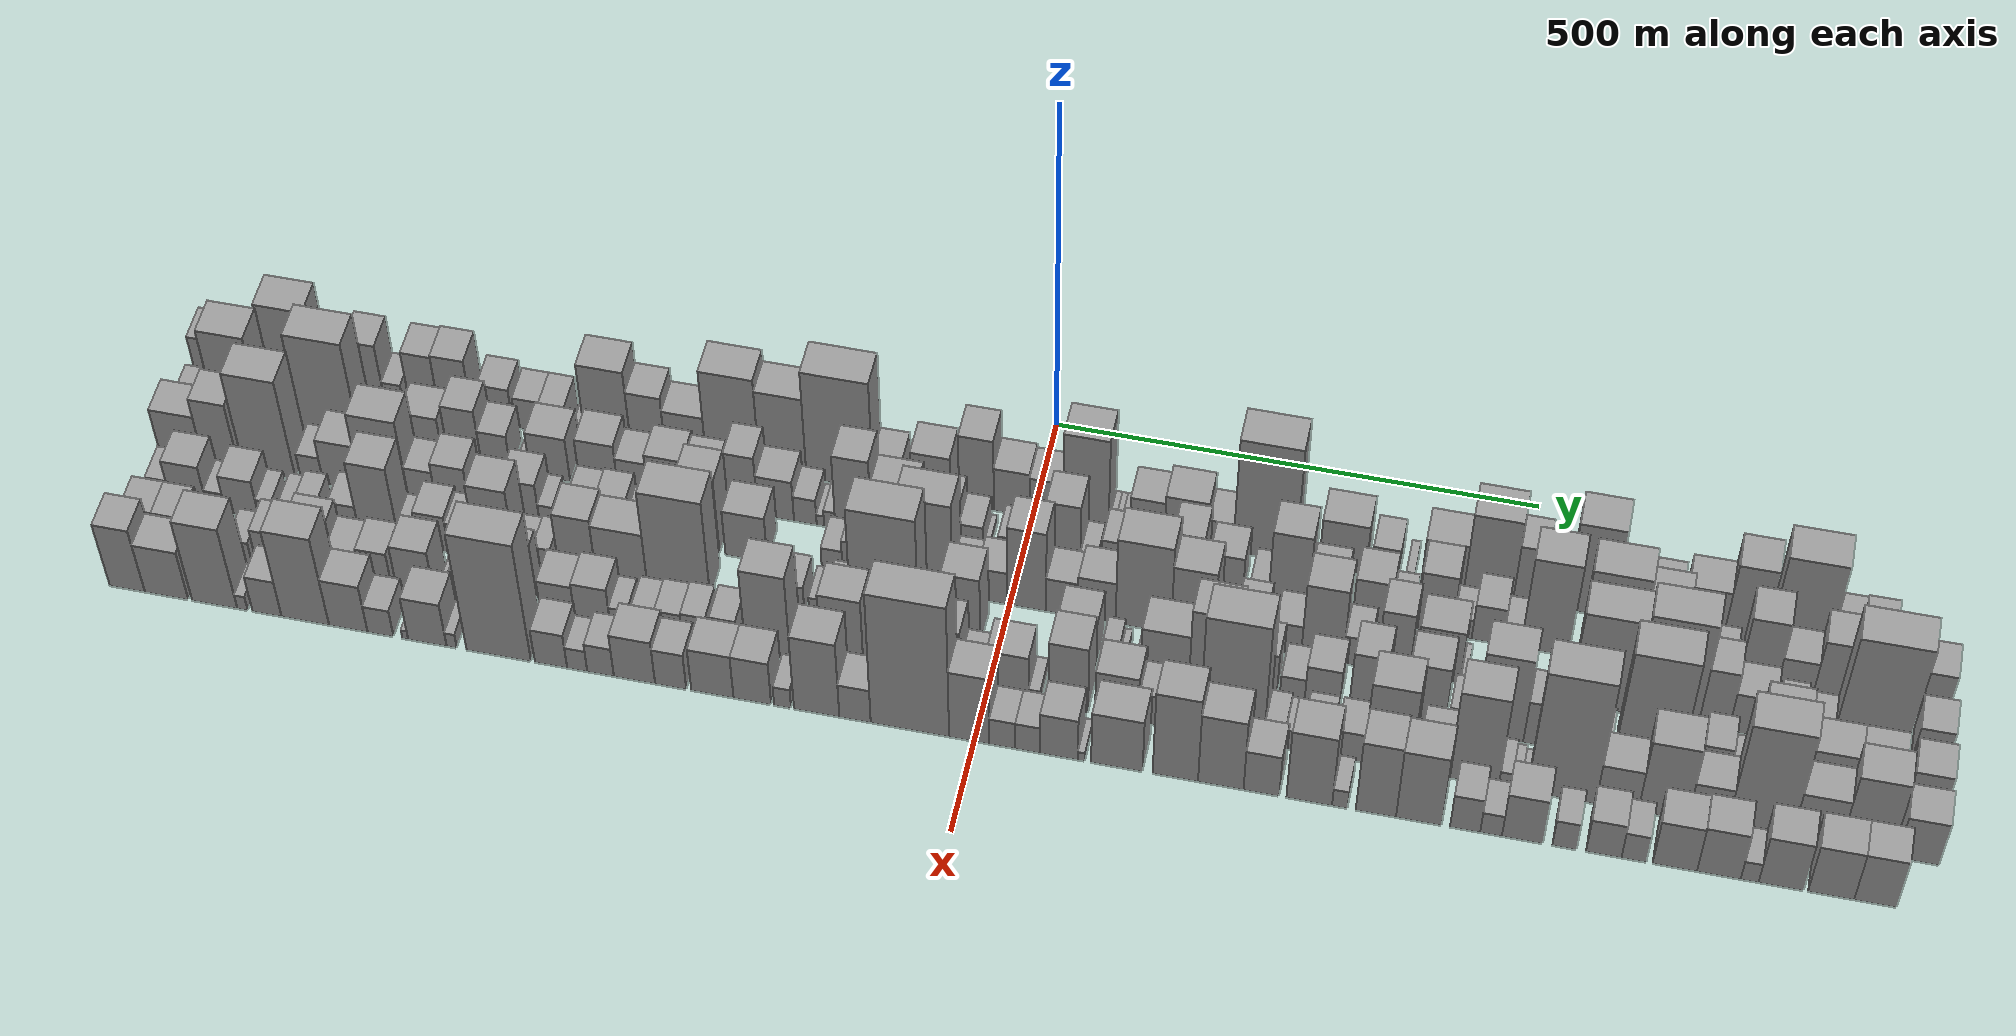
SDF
<sdf version="1.6">
 <world name="default">
  <scene>
   <sky><clouds><speed>12</speed></clouds></sky>
   <ambient>0.4 0.4 0.4 1</ambient>
   <background>0.7 0.7 0.7 1</background>
   <shadows>1</shadows>
  </scene>
  <gravity>0 0 -9.8066</gravity>
  <magnetic_field>6e-06 2.3e-05 -4.2e-05</magnetic_field>
  <physics default="0" name="default_physics" type="ode">
   <ode>
    <solver>
     <type>quick</type>
     <iters>10</iters>
     <sor>1.0</sor>
     <use_dynamic_moi_rescaling>0</use_dynamic_moi_rescaling>
    </solver>
    <constraints>
     <cfm>0</cfm>
     <erp>0.2</erp>
     <contact_max_correcting_vel>100</contact_max_correcting_vel>
     <contact_surface_layer>0.001</contact_surface_layer>
    </constraints>
   </ode>
   <max_step_size>0.004</max_step_size>
   <real_time_factor>1</real_time_factor>
   <real_time_update_rate>250</real_time_update_rate>
  </physics>
  <light name="sun" type="directional">
   <pose>0 0 10 0 0 0</pose>
   <diffuse>0.8 0.8 0.8 1</diffuse>
   <specular>0.2 0.2 0.2 1</specular>
   <attenuation>
    <range>1000</range>
    <constant>0.9</constant>
    <linear>0.01</linear>
    <quadratic>0.001</quadratic>
   </attenuation>
   <direction>-0.5 0.1 -0.9</direction>
  </light>
  <model name="building_1">
   <static>1</static>
   <pose>100.0000 -872.8744 0 0.000000 0.000000 0.000000</pose>
   <link name="link">
    <pose>0 0 30.00 0 0 0</pose>
    <collision name="collision"><geometry><box><size>40.0000 34.2511 60.0000</size></box></geometry></collision>
    <visual name="visual">
     <cast_shadows>0</cast_shadows>
     <geometry><box><size>40.0000 34.2511 60.0000</size></box></geometry>
     <material>
      <script>
       <uri>model://grey_wall/materials/scripts</uri>
       <uri>model://grey_wall/materials/textures</uri>
       <name>vrc/grey_wall</name>
      </script>
     </material>
    </visual>
   </link>
  </model>
  <model name="building_2">
   <static>1</static>
   <pose>100.0000 -840.3161 0 0.000000 0.000000 0.000000</pose>
   <link name="link">
    <pose>0 0 27.00 0 0 0</pose>
    <collision name="collision"><geometry><box><size>40.0000 30.8656 54.0000</size></box></geometry></collision>
    <visual name="visual">
     <cast_shadows>0</cast_shadows>
     <geometry><box><size>40.0000 30.8656 54.0000</size></box></geometry>
     <material>
      <script>
       <uri>model://grey_wall/materials/scripts</uri>
       <uri>model://grey_wall/materials/textures</uri>
       <name>vrc/grey_wall</name>
      </script>
     </material>
    </visual>
   </link>
  </model>
  <model name="building_3">
   <static>1</static>
   <pose>100.0000 -821.1841 0 0.000000 0.000000 0.000000</pose>
   <link name="link">
    <pose>0 0 7.50 0 0 0</pose>
    <collision name="collision"><geometry><box><size>40.0000 7.3984 15.0000</size></box></geometry></collision>
    <visual name="visual">
     <cast_shadows>0</cast_shadows>
     <geometry><box><size>40.0000 7.3984 15.0000</size></box></geometry>
     <material>
      <script>
       <uri>model://grey_wall/materials/scripts</uri>
       <uri>model://grey_wall/materials/textures</uri>
       <name>vrc/grey_wall</name>
      </script>
     </material>
    </visual>
   </link>
  </model>
  <model name="building_4">
   <static>1</static>
   <pose>100.0000 -781.3801 0 0.000000 0.000000 0.000000</pose>
   <link name="link">
    <pose>0 0 67.50 0 0 0</pose>
    <collision name="collision"><geometry><box><size>40.0000 52.2096 135.0000</size></box></geometry></collision>
    <visual name="visual">
     <cast_shadows>0</cast_shadows>
     <geometry><box><size>40.0000 52.2096 135.0000</size></box></geometry>
     <material>
      <script>
       <uri>model://grey_wall/materials/scripts</uri>
       <uri>model://grey_wall/materials/textures</uri>
       <name>vrc/grey_wall</name>
      </script>
     </material>
    </visual>
   </link>
  </model>
  <model name="building_5">
   <static>1</static>
   <pose>100.0000 -735.6775 0 0.000000 0.000000 0.000000</pose>
   <link name="link">
    <pose>0 0 27.00 0 0 0</pose>
    <collision name="collision"><geometry><box><size>40.0000 29.1955 54.0000</size></box></geometry></collision>
    <visual name="visual">
     <cast_shadows>0</cast_shadows>
     <geometry><box><size>40.0000 29.1955 54.0000</size></box></geometry>
     <material>
      <script>
       <uri>model://grey_wall/materials/scripts</uri>
       <uri>model://grey_wall/materials/textures</uri>
       <name>vrc/grey_wall</name>
      </script>
     </material>
    </visual>
   </link>
  </model>
  <model name="building_6">
   <static>1</static>
   <pose>100.0000 -700.4989 0 0.000000 0.000000 0.000000</pose>
   <link name="link">
    <pose>0 0 49.50 0 0 0</pose>
    <collision name="collision"><geometry><box><size>40.0000 33.1616 99.0000</size></box></geometry></collision>
    <visual name="visual">
     <cast_shadows>0</cast_shadows>
     <geometry><box><size>40.0000 33.1616 99.0000</size></box></geometry>
     <material>
      <script>
       <uri>model://grey_wall/materials/scripts</uri>
       <uri>model://grey_wall/materials/textures</uri>
       <name>vrc/grey_wall</name>
      </script>
     </material>
    </visual>
   </link>
  </model>
  <model name="building_7">
   <static>1</static>
   <pose>100.0000 -673.7841 0 0.000000 0.000000 0.000000</pose>
   <link name="link">
    <pose>0 0 19.50 0 0 0</pose>
    <collision name="collision"><geometry><box><size>40.0000 20.2681 39.0000</size></box></geometry></collision>
    <visual name="visual">
     <cast_shadows>0</cast_shadows>
     <geometry><box><size>40.0000 20.2681 39.0000</size></box></geometry>
     <material>
      <script>
       <uri>model://grey_wall/materials/scripts</uri>
       <uri>model://grey_wall/materials/textures</uri>
       <name>vrc/grey_wall</name>
      </script>
     </material>
    </visual>
   </link>
  </model>
  <model name="building_8">
   <static>1</static>
   <pose>100.0000 -660.1916 0 0.000000 0.000000 0.000000</pose>
   <link name="link">
    <pose>0 0 7.50 0 0 0</pose>
    <collision name="collision"><geometry><box><size>40.0000 6.9169 15.0000</size></box></geometry></collision>
    <visual name="visual">
     <cast_shadows>0</cast_shadows>
     <geometry><box><size>40.0000 6.9169 15.0000</size></box></geometry>
     <material>
      <script>
       <uri>model://grey_wall/materials/scripts</uri>
       <uri>model://grey_wall/materials/textures</uri>
       <name>vrc/grey_wall</name>
      </script>
     </material>
    </visual>
   </link>
  </model>
  <model name="building_9">
   <static>1</static>
   <pose>100.0000 -641.0431 0 0.000000 0.000000 0.000000</pose>
   <link name="link">
    <pose>0 0 48.00 0 0 0</pose>
    <collision name="collision"><geometry><box><size>40.0000 31.3800 96.0000</size></box></geometry></collision>
    <visual name="visual">
     <cast_shadows>0</cast_shadows>
     <geometry><box><size>40.0000 31.3800 96.0000</size></box></geometry>
     <material>
      <script>
       <uri>model://grey_wall/materials/scripts</uri>
       <uri>model://grey_wall/materials/textures</uri>
       <name>vrc/grey_wall</name>
      </script>
     </material>
    </visual>
   </link>
  </model>
  <model name="building_10">
   <static>1</static>
   <pose>100.0000 -607.6673 0 0.000000 0.000000 0.000000</pose>
   <link name="link">
    <pose>0 0 49.50 0 0 0</pose>
    <collision name="collision"><geometry><box><size>40.0000 35.3715 99.0000</size></box></geometry></collision>
    <visual name="visual">
     <cast_shadows>0</cast_shadows>
     <geometry><box><size>40.0000 35.3715 99.0000</size></box></geometry>
     <material>
      <script>
       <uri>model://grey_wall/materials/scripts</uri>
       <uri>model://grey_wall/materials/textures</uri>
       <name>vrc/grey_wall</name>
      </script>
     </material>
    </visual>
   </link>
  </model>
  <model name="building_11">
   <static>1</static>
   <pose>100.0000 -563.3207 0 0.000000 0.000000 0.000000</pose>
   <link name="link">
    <pose>0 0 31.50 0 0 0</pose>
    <collision name="collision"><geometry><box><size>40.0000 33.3217 63.0000</size></box></geometry></collision>
    <visual name="visual">
     <cast_shadows>0</cast_shadows>
     <geometry><box><size>40.0000 33.3217 63.0000</size></box></geometry>
     <material>
      <script>
       <uri>model://grey_wall/materials/scripts</uri>
       <uri>model://grey_wall/materials/textures</uri>
       <name>vrc/grey_wall</name>
      </script>
     </material>
    </visual>
   </link>
  </model>
  <model name="building_12">
   <static>1</static>
   <pose>100.0000 -529.5329 0 0.000000 0.000000 0.000000</pose>
   <link name="link">
    <pose>0 0 25.50 0 0 0</pose>
    <collision name="collision"><geometry><box><size>40.0000 28.2539 51.0000</size></box></geometry></collision>
    <visual name="visual">
     <cast_shadows>0</cast_shadows>
     <geometry><box><size>40.0000 28.2539 51.0000</size></box></geometry>
     <material>
      <script>
       <uri>model://grey_wall/materials/scripts</uri>
       <uri>model://grey_wall/materials/textures</uri>
       <name>vrc/grey_wall</name>
      </script>
     </material>
    </visual>
   </link>
  </model>
  <model name="building_13">
   <static>1</static>
   <pose>100.0000 -501.8472 0 0.000000 0.000000 0.000000</pose>
   <link name="link">
    <pose>0 0 25.50 0 0 0</pose>
    <collision name="collision"><geometry><box><size>40.0000 27.1175 51.0000</size></box></geometry></collision>
    <visual name="visual">
     <cast_shadows>0</cast_shadows>
     <geometry><box><size>40.0000 27.1175 51.0000</size></box></geometry>
     <material>
      <script>
       <uri>model://grey_wall/materials/scripts</uri>
       <uri>model://grey_wall/materials/textures</uri>
       <name>vrc/grey_wall</name>
      </script>
     </material>
    </visual>
   </link>
  </model>
  <model name="building_14">
   <static>1</static>
   <pose>100.0000 -475.6288 0 0.000000 0.000000 0.000000</pose>
   <link name="link">
    <pose>0 0 12.00 0 0 0</pose>
    <collision name="collision"><geometry><box><size>40.0000 11.3192 24.0000</size></box></geometry></collision>
    <visual name="visual">
     <cast_shadows>0</cast_shadows>
     <geometry><box><size>40.0000 11.3192 24.0000</size></box></geometry>
     <material>
      <script>
       <uri>model://grey_wall/materials/scripts</uri>
       <uri>model://grey_wall/materials/textures</uri>
       <name>vrc/grey_wall</name>
      </script>
     </material>
    </visual>
   </link>
  </model>
  <model name="building_15">
   <static>1</static>
   <pose>100.0000 -445.5690 0 0.000000 0.000000 0.000000</pose>
   <link name="link">
    <pose>0 0 63.00 0 0 0</pose>
    <collision name="collision"><geometry><box><size>40.0000 48.8003 126.0000</size></box></geometry></collision>
    <visual name="visual">
     <cast_shadows>0</cast_shadows>
     <geometry><box><size>40.0000 48.8003 126.0000</size></box></geometry>
     <material>
      <script>
       <uri>model://grey_wall/materials/scripts</uri>
       <uri>model://grey_wall/materials/textures</uri>
       <name>vrc/grey_wall</name>
      </script>
     </material>
    </visual>
   </link>
  </model>
  <model name="building_16">
   <static>1</static>
   <pose>100.0000 -402.9432 0 0.000000 0.000000 0.000000</pose>
   <link name="link">
    <pose>0 0 46.50 0 0 0</pose>
    <collision name="collision"><geometry><box><size>40.0000 36.4514 93.0000</size></box></geometry></collision>
    <visual name="visual">
     <cast_shadows>0</cast_shadows>
     <geometry><box><size>40.0000 36.4514 93.0000</size></box></geometry>
     <material>
      <script>
       <uri>model://grey_wall/materials/scripts</uri>
       <uri>model://grey_wall/materials/textures</uri>
       <name>vrc/grey_wall</name>
      </script>
     </material>
    </visual>
   </link>
  </model>
  <model name="building_17">
   <static>1</static>
   <pose>100.0000 -363.1853 0 0.000000 0.000000 0.000000</pose>
   <link name="link">
    <pose>0 0 36.00 0 0 0</pose>
    <collision name="collision"><geometry><box><size>40.0000 43.0645 72.0000</size></box></geometry></collision>
    <visual name="visual">
     <cast_shadows>0</cast_shadows>
     <geometry><box><size>40.0000 43.0645 72.0000</size></box></geometry>
     <material>
      <script>
       <uri>model://grey_wall/materials/scripts</uri>
       <uri>model://grey_wall/materials/textures</uri>
       <name>vrc/grey_wall</name>
      </script>
     </material>
    </visual>
   </link>
  </model>
  <model name="building_18">
   <static>1</static>
   <pose>100.0000 -313.5661 0 0.000000 0.000000 0.000000</pose>
   <link name="link">
    <pose>0 0 75.00 0 0 0</pose>
    <collision name="collision"><geometry><box><size>40.0000 56.1737 150.0000</size></box></geometry></collision>
    <visual name="visual">
     <cast_shadows>0</cast_shadows>
     <geometry><box><size>40.0000 56.1737 150.0000</size></box></geometry>
     <material>
      <script>
       <uri>model://grey_wall/materials/scripts</uri>
       <uri>model://grey_wall/materials/textures</uri>
       <name>vrc/grey_wall</name>
      </script>
     </material>
    </visual>
   </link>
  </model>
  <model name="building_19">
   <static>1</static>
   <pose>100.0000 -260.8555 0 0.000000 0.000000 0.000000</pose>
   <link name="link">
    <pose>0 0 66.00 0 0 0</pose>
    <collision name="collision"><geometry><box><size>40.0000 49.2475 132.0000</size></box></geometry></collision>
    <visual name="visual">
     <cast_shadows>0</cast_shadows>
     <geometry><box><size>40.0000 49.2475 132.0000</size></box></geometry>
     <material>
      <script>
       <uri>model://grey_wall/materials/scripts</uri>
       <uri>model://grey_wall/materials/textures</uri>
       <name>vrc/grey_wall</name>
      </script>
     </material>
    </visual>
   </link>
  </model>
  <model name="building_20">
   <static>1</static>
   <pose>100.0000 -201.3446 0 0.000000 0.000000 0.000000</pose>
   <link name="link">
    <pose>0 0 88.50 0 0 0</pose>
    <collision name="collision"><geometry><box><size>40.0000 69.7743 177.0000</size></box></geometry></collision>
    <visual name="visual">
     <cast_shadows>0</cast_shadows>
     <geometry><box><size>40.0000 69.7743 177.0000</size></box></geometry>
     <material>
      <script>
       <uri>model://grey_wall/materials/scripts</uri>
       <uri>model://grey_wall/materials/textures</uri>
       <name>vrc/grey_wall</name>
      </script>
     </material>
    </visual>
   </link>
  </model>
  <model name="building_21">
   <static>1</static>
   <pose>100.0000 -151.1282 0 0.000000 0.000000 0.000000</pose>
   <link name="link">
    <pose>0 0 27.00 0 0 0</pose>
    <collision name="collision"><geometry><box><size>40.0000 30.6586 54.0000</size></box></geometry></collision>
    <visual name="visual">
     <cast_shadows>0</cast_shadows>
     <geometry><box><size>40.0000 30.6586 54.0000</size></box></geometry>
     <material>
      <script>
       <uri>model://grey_wall/materials/scripts</uri>
       <uri>model://grey_wall/materials/textures</uri>
       <name>vrc/grey_wall</name>
      </script>
     </material>
    </visual>
   </link>
  </model>
  <model name="building_22">
   <static>1</static>
   <pose>100.0000 -106.2532 0 0.000000 0.000000 0.000000</pose>
   <link name="link">
    <pose>0 0 37.50 0 0 0</pose>
    <collision name="collision"><geometry><box><size>40.0000 41.0914 75.0000</size></box></geometry></collision>
    <visual name="visual">
     <cast_shadows>0</cast_shadows>
     <geometry><box><size>40.0000 41.0914 75.0000</size></box></geometry>
     <material>
      <script>
       <uri>model://grey_wall/materials/scripts</uri>
       <uri>model://grey_wall/materials/textures</uri>
       <name>vrc/grey_wall</name>
      </script>
     </material>
    </visual>
   </link>
  </model>
  <model name="building_23">
   <static>1</static>
   <pose>100.0000 -58.7325 0 0.000000 0.000000 0.000000</pose>
   <link name="link">
    <pose>0 0 58.50 0 0 0</pose>
    <collision name="collision"><geometry><box><size>40.0000 35.9500 117.0000</size></box></geometry></collision>
    <visual name="visual">
     <cast_shadows>0</cast_shadows>
     <geometry><box><size>40.0000 35.9500 117.0000</size></box></geometry>
     <material>
      <script>
       <uri>model://grey_wall/materials/scripts</uri>
       <uri>model://grey_wall/materials/textures</uri>
       <name>vrc/grey_wall</name>
      </script>
     </material>
    </visual>
   </link>
  </model>
  <model name="building_24">
   <static>1</static>
   <pose>100.0000 -22.3006 0 0.000000 0.000000 0.000000</pose>
   <link name="link">
    <pose>0 0 36.00 0 0 0</pose>
    <collision name="collision"><geometry><box><size>40.0000 36.9137 72.0000</size></box></geometry></collision>
    <visual name="visual">
     <cast_shadows>0</cast_shadows>
     <geometry><box><size>40.0000 36.9137 72.0000</size></box></geometry>
     <material>
      <script>
       <uri>model://grey_wall/materials/scripts</uri>
       <uri>model://grey_wall/materials/textures</uri>
       <name>vrc/grey_wall</name>
      </script>
     </material>
    </visual>
   </link>
  </model>
  <model name="building_25">
   <static>1</static>
   <pose>100.0000 13.4594 0 0.000000 0.000000 0.000000</pose>
   <link name="link">
    <pose>0 0 33.00 0 0 0</pose>
    <collision name="collision"><geometry><box><size>40.0000 34.6064 66.0000</size></box></geometry></collision>
    <visual name="visual">
     <cast_shadows>0</cast_shadows>
     <geometry><box><size>40.0000 34.6064 66.0000</size></box></geometry>
     <material>
      <script>
       <uri>model://grey_wall/materials/scripts</uri>
       <uri>model://grey_wall/materials/textures</uri>
       <name>vrc/grey_wall</name>
      </script>
     </material>
    </visual>
   </link>
  </model>
  <model name="building_26">
   <static>1</static>
   <pose>100.0000 54.2847 0 0.000000 0.000000 0.000000</pose>
   <link name="link">
    <pose>0 0 75.00 0 0 0</pose>
    <collision name="collision"><geometry><box><size>40.0000 47.0442 150.0000</size></box></geometry></collision>
    <visual name="visual">
     <cast_shadows>0</cast_shadows>
     <geometry><box><size>40.0000 47.0442 150.0000</size></box></geometry>
     <material>
      <script>
       <uri>model://grey_wall/materials/scripts</uri>
       <uri>model://grey_wall/materials/textures</uri>
       <name>vrc/grey_wall</name>
      </script>
     </material>
    </visual>
   </link>
  </model>
  <model name="building_27">
   <static>1</static>
   <pose>100.0000 81.0276 0 0.000000 0.000000 0.000000</pose>
   <link name="link">
    <pose>0 0 7.50 0 0 0</pose>
    <collision name="collision"><geometry><box><size>40.0000 6.4415 15.0000</size></box></geometry></collision>
    <visual name="visual">
     <cast_shadows>0</cast_shadows>
     <geometry><box><size>40.0000 6.4415 15.0000</size></box></geometry>
     <material>
      <script>
       <uri>model://grey_wall/materials/scripts</uri>
       <uri>model://grey_wall/materials/textures</uri>
       <name>vrc/grey_wall</name>
      </script>
     </material>
    </visual>
   </link>
  </model>
  <model name="building_28">
   <static>1</static>
   <pose>100.0000 87.2667 0 0.000000 0.000000 0.000000</pose>
   <link name="link">
    <pose>0 0 7.50 0 0 0</pose>
    <collision name="collision"><geometry><box><size>40.0000 6.0367 15.0000</size></box></geometry></collision>
    <visual name="visual">
     <cast_shadows>0</cast_shadows>
     <geometry><box><size>40.0000 6.0367 15.0000</size></box></geometry>
     <material>
      <script>
       <uri>model://grey_wall/materials/scripts</uri>
       <uri>model://grey_wall/materials/textures</uri>
       <name>vrc/grey_wall</name>
      </script>
     </material>
    </visual>
   </link>
  </model>
  <model name="building_29">
   <static>1</static>
   <pose>100.0000 93.5293 0 0.000000 0.000000 0.000000</pose>
   <link name="link">
    <pose>0 0 7.50 0 0 0</pose>
    <collision name="collision"><geometry><box><size>40.0000 6.4887 15.0000</size></box></geometry></collision>
    <visual name="visual">
     <cast_shadows>0</cast_shadows>
     <geometry><box><size>40.0000 6.4887 15.0000</size></box></geometry>
     <material>
      <script>
       <uri>model://grey_wall/materials/scripts</uri>
       <uri>model://grey_wall/materials/textures</uri>
       <name>vrc/grey_wall</name>
      </script>
     </material>
    </visual>
   </link>
  </model>
  <model name="building_30">
   <static>1</static>
   <pose>100.0000 117.5824 0 0.000000 0.000000 0.000000</pose>
   <link name="link">
    <pose>0 0 31.50 0 0 0</pose>
    <collision name="collision"><geometry><box><size>40.0000 35.6174 63.0000</size></box></geometry></collision>
    <visual name="visual">
     <cast_shadows>0</cast_shadows>
     <geometry><box><size>40.0000 35.6174 63.0000</size></box></geometry>
     <material>
      <script>
       <uri>model://grey_wall/materials/scripts</uri>
       <uri>model://grey_wall/materials/textures</uri>
       <name>vrc/grey_wall</name>
      </script>
     </material>
    </visual>
   </link>
  </model>
  <model name="building_31">
   <static>1</static>
   <pose>100.0000 157.6466 0 0.000000 0.000000 0.000000</pose>
   <link name="link">
    <pose>0 0 37.50 0 0 0</pose>
    <collision name="collision"><geometry><box><size>40.0000 44.5112 75.0000</size></box></geometry></collision>
    <visual name="visual">
     <cast_shadows>0</cast_shadows>
     <geometry><box><size>40.0000 44.5112 75.0000</size></box></geometry>
     <material>
      <script>
       <uri>model://grey_wall/materials/scripts</uri>
       <uri>model://grey_wall/materials/textures</uri>
       <name>vrc/grey_wall</name>
      </script>
     </material>
    </visual>
   </link>
  </model>
  <model name="building_32">
   <static>1</static>
   <pose>100.0000 192.7787 0 0.000000 0.000000 0.000000</pose>
   <link name="link">
    <pose>0 0 24.00 0 0 0</pose>
    <collision name="collision"><geometry><box><size>40.0000 25.7529 48.0000</size></box></geometry></collision>
    <visual name="visual">
     <cast_shadows>0</cast_shadows>
     <geometry><box><size>40.0000 25.7529 48.0000</size></box></geometry>
     <material>
      <script>
       <uri>model://grey_wall/materials/scripts</uri>
       <uri>model://grey_wall/materials/textures</uri>
       <name>vrc/grey_wall</name>
      </script>
     </material>
    </visual>
   </link>
  </model>
  <model name="building_33">
   <static>1</static>
   <pose>100.0000 237.5757 0 0.000000 0.000000 0.000000</pose>
   <link name="link">
    <pose>0 0 94.50 0 0 0</pose>
    <collision name="collision"><geometry><box><size>40.0000 63.8411 189.0000</size></box></geometry></collision>
    <visual name="visual">
     <cast_shadows>0</cast_shadows>
     <geometry><box><size>40.0000 63.8411 189.0000</size></box></geometry>
     <material>
      <script>
       <uri>model://grey_wall/materials/scripts</uri>
       <uri>model://grey_wall/materials/textures</uri>
       <name>vrc/grey_wall</name>
      </script>
     </material>
    </visual>
   </link>
  </model>
  <model name="building_34">
   <static>1</static>
   <pose>100.0000 282.9036 0 0.000000 0.000000 0.000000</pose>
   <link name="link">
    <pose>0 0 7.50 0 0 0</pose>
    <collision name="collision"><geometry><box><size>40.0000 6.8147 15.0000</size></box></geometry></collision>
    <visual name="visual">
     <cast_shadows>0</cast_shadows>
     <geometry><box><size>40.0000 6.8147 15.0000</size></box></geometry>
     <material>
      <script>
       <uri>model://grey_wall/materials/scripts</uri>
       <uri>model://grey_wall/materials/textures</uri>
       <name>vrc/grey_wall</name>
      </script>
     </material>
    </visual>
   </link>
  </model>
  <model name="building_35">
   <static>1</static>
   <pose>100.0000 317.2166 0 0.000000 0.000000 0.000000</pose>
   <link name="link">
    <pose>0 0 40.50 0 0 0</pose>
    <collision name="collision"><geometry><box><size>40.0000 47.8113 81.0000</size></box></geometry></collision>
    <visual name="visual">
     <cast_shadows>0</cast_shadows>
     <geometry><box><size>40.0000 47.8113 81.0000</size></box></geometry>
     <material>
      <script>
       <uri>model://grey_wall/materials/scripts</uri>
       <uri>model://grey_wall/materials/textures</uri>
       <name>vrc/grey_wall</name>
      </script>
     </material>
    </visual>
   </link>
  </model>
  <model name="building_36">
   <static>1</static>
   <pose>100.0000 360.1481 0 0.000000 0.000000 0.000000</pose>
   <link name="link">
    <pose>0 0 25.50 0 0 0</pose>
    <collision name="collision"><geometry><box><size>40.0000 28.0517 51.0000</size></box></geometry></collision>
    <visual name="visual">
     <cast_shadows>0</cast_shadows>
     <geometry><box><size>40.0000 28.0517 51.0000</size></box></geometry>
     <material>
      <script>
       <uri>model://grey_wall/materials/scripts</uri>
       <uri>model://grey_wall/materials/textures</uri>
       <name>vrc/grey_wall</name>
      </script>
     </material>
    </visual>
   </link>
  </model>
  <model name="building_37">
   <static>1</static>
   <pose>100.0000 385.6458 0 0.000000 0.000000 0.000000</pose>
   <link name="link">
    <pose>0 0 9.00 0 0 0</pose>
    <collision name="collision"><geometry><box><size>40.0000 8.9437 18.0000</size></box></geometry></collision>
    <visual name="visual">
     <cast_shadows>0</cast_shadows>
     <geometry><box><size>40.0000 8.9437 18.0000</size></box></geometry>
     <material>
      <script>
       <uri>model://grey_wall/materials/scripts</uri>
       <uri>model://grey_wall/materials/textures</uri>
       <name>vrc/grey_wall</name>
      </script>
     </material>
    </visual>
   </link>
  </model>
  <model name="building_38">
   <static>1</static>
   <pose>100.0000 418.6927 0 0.000000 0.000000 0.000000</pose>
   <link name="link">
    <pose>0 0 39.00 0 0 0</pose>
    <collision name="collision"><geometry><box><size>40.0000 43.1501 78.0000</size></box></geometry></collision>
    <visual name="visual">
     <cast_shadows>0</cast_shadows>
     <geometry><box><size>40.0000 43.1501 78.0000</size></box></geometry>
     <material>
      <script>
       <uri>model://grey_wall/materials/scripts</uri>
       <uri>model://grey_wall/materials/textures</uri>
       <name>vrc/grey_wall</name>
      </script>
     </material>
    </visual>
   </link>
  </model>
  <model name="building_39">
   <static>1</static>
   <pose>100.0000 465.1550 0 0.000000 0.000000 0.000000</pose>
   <link name="link">
    <pose>0 0 66.00 0 0 0</pose>
    <collision name="collision"><geometry><box><size>40.0000 49.7746 132.0000</size></box></geometry></collision>
    <visual name="visual">
     <cast_shadows>0</cast_shadows>
     <geometry><box><size>40.0000 49.7746 132.0000</size></box></geometry>
     <material>
      <script>
       <uri>model://grey_wall/materials/scripts</uri>
       <uri>model://grey_wall/materials/textures</uri>
       <name>vrc/grey_wall</name>
      </script>
     </material>
    </visual>
   </link>
  </model>
  <model name="building_40">
   <static>1</static>
   <pose>100.0000 504.3704 0 0.000000 0.000000 0.000000</pose>
   <link name="link">
    <pose>0 0 46.50 0 0 0</pose>
    <collision name="collision"><geometry><box><size>40.0000 28.6561 93.0000</size></box></geometry></collision>
    <visual name="visual">
     <cast_shadows>0</cast_shadows>
     <geometry><box><size>40.0000 28.6561 93.0000</size></box></geometry>
     <material>
      <script>
       <uri>model://grey_wall/materials/scripts</uri>
       <uri>model://grey_wall/materials/textures</uri>
       <name>vrc/grey_wall</name>
      </script>
     </material>
    </visual>
   </link>
  </model>
  <model name="building_41">
   <static>1</static>
   <pose>100.0000 530.5672 0 0.000000 0.000000 0.000000</pose>
   <link name="link">
    <pose>0 0 22.50 0 0 0</pose>
    <collision name="collision"><geometry><box><size>40.0000 23.7376 45.0000</size></box></geometry></collision>
    <visual name="visual">
     <cast_shadows>0</cast_shadows>
     <geometry><box><size>40.0000 23.7376 45.0000</size></box></geometry>
     <material>
      <script>
       <uri>model://grey_wall/materials/scripts</uri>
       <uri>model://grey_wall/materials/textures</uri>
       <name>vrc/grey_wall</name>
      </script>
     </material>
    </visual>
   </link>
  </model>
  <model name="building_42">
   <static>1</static>
   <pose>100.0000 566.0628 0 0.000000 0.000000 0.000000</pose>
   <link name="link">
    <pose>0 0 73.50 0 0 0</pose>
    <collision name="collision"><geometry><box><size>40.0000 47.2535 147.0000</size></box></geometry></collision>
    <visual name="visual">
     <cast_shadows>0</cast_shadows>
     <geometry><box><size>40.0000 47.2535 147.0000</size></box></geometry>
     <material>
      <script>
       <uri>model://grey_wall/materials/scripts</uri>
       <uri>model://grey_wall/materials/textures</uri>
       <name>vrc/grey_wall</name>
      </script>
     </material>
    </visual>
   </link>
  </model>
  <model name="building_43">
   <static>1</static>
   <pose>100.0000 605.2455 0 0.000000 0.000000 0.000000</pose>
   <link name="link">
    <pose>0 0 27.00 0 0 0</pose>
    <collision name="collision"><geometry><box><size>40.0000 31.1120 54.0000</size></box></geometry></collision>
    <visual name="visual">
     <cast_shadows>0</cast_shadows>
     <geometry><box><size>40.0000 31.1120 54.0000</size></box></geometry>
     <material>
      <script>
       <uri>model://grey_wall/materials/scripts</uri>
       <uri>model://grey_wall/materials/textures</uri>
       <name>vrc/grey_wall</name>
      </script>
     </material>
    </visual>
   </link>
  </model>
  <model name="building_44">
   <static>1</static>
   <pose>100.0000 637.2540 0 0.000000 0.000000 0.000000</pose>
   <link name="link">
    <pose>0 0 30.00 0 0 0</pose>
    <collision name="collision"><geometry><box><size>40.0000 32.9049 60.0000</size></box></geometry></collision>
    <visual name="visual">
     <cast_shadows>0</cast_shadows>
     <geometry><box><size>40.0000 32.9049 60.0000</size></box></geometry>
     <material>
      <script>
       <uri>model://grey_wall/materials/scripts</uri>
       <uri>model://grey_wall/materials/textures</uri>
       <name>vrc/grey_wall</name>
      </script>
     </material>
    </visual>
   </link>
  </model>
  <model name="building_45">
   <static>1</static>
   <pose>100.0000 679.1042 0 0.000000 0.000000 0.000000</pose>
   <link name="link">
    <pose>0 0 37.50 0 0 0</pose>
    <collision name="collision"><geometry><box><size>40.0000 42.7956 75.0000</size></box></geometry></collision>
    <visual name="visual">
     <cast_shadows>0</cast_shadows>
     <geometry><box><size>40.0000 42.7956 75.0000</size></box></geometry>
     <material>
      <script>
       <uri>model://grey_wall/materials/scripts</uri>
       <uri>model://grey_wall/materials/textures</uri>
       <name>vrc/grey_wall</name>
      </script>
     </material>
    </visual>
   </link>
  </model>
  <model name="building_46">
   <static>1</static>
   <pose>100.0000 720.5906 0 0.000000 0.000000 0.000000</pose>
   <link name="link">
    <pose>0 0 61.50 0 0 0</pose>
    <collision name="collision"><geometry><box><size>40.0000 40.1771 123.0000</size></box></geometry></collision>
    <visual name="visual">
     <cast_shadows>0</cast_shadows>
     <geometry><box><size>40.0000 40.1771 123.0000</size></box></geometry>
     <material>
      <script>
       <uri>model://grey_wall/materials/scripts</uri>
       <uri>model://grey_wall/materials/textures</uri>
       <name>vrc/grey_wall</name>
      </script>
     </material>
    </visual>
   </link>
  </model>
  <model name="building_47">
   <static>1</static>
   <pose>100.0000 774.5838 0 0.000000 0.000000 0.000000</pose>
   <link name="link">
    <pose>0 0 75.00 0 0 0</pose>
    <collision name="collision"><geometry><box><size>40.0000 59.8094 150.0000</size></box></geometry></collision>
    <visual name="visual">
     <cast_shadows>0</cast_shadows>
     <geometry><box><size>40.0000 59.8094 150.0000</size></box></geometry>
     <material>
      <script>
       <uri>model://grey_wall/materials/scripts</uri>
       <uri>model://grey_wall/materials/textures</uri>
       <name>vrc/grey_wall</name>
      </script>
     </material>
    </visual>
   </link>
  </model>
  <model name="building_48">
   <static>1</static>
   <pose>100.0000 818.4534 0 0.000000 0.000000 0.000000</pose>
   <link name="link">
    <pose>0 0 27.00 0 0 0</pose>
    <collision name="collision"><geometry><box><size>40.0000 27.9298 54.0000</size></box></geometry></collision>
    <visual name="visual">
     <cast_shadows>0</cast_shadows>
     <geometry><box><size>40.0000 27.9298 54.0000</size></box></geometry>
     <material>
      <script>
       <uri>model://grey_wall/materials/scripts</uri>
       <uri>model://grey_wall/materials/textures</uri>
       <name>vrc/grey_wall</name>
      </script>
     </material>
    </visual>
   </link>
  </model>
  <model name="building_49">
   <static>1</static>
   <pose>100.0000 848.4009 0 0.000000 0.000000 0.000000</pose>
   <link name="link">
    <pose>0 0 28.50 0 0 0</pose>
    <collision name="collision"><geometry><box><size>40.0000 31.9652 57.0000</size></box></geometry></collision>
    <visual name="visual">
     <cast_shadows>0</cast_shadows>
     <geometry><box><size>40.0000 31.9652 57.0000</size></box></geometry>
     <material>
      <script>
       <uri>model://grey_wall/materials/scripts</uri>
       <uri>model://grey_wall/materials/textures</uri>
       <name>vrc/grey_wall</name>
      </script>
     </material>
    </visual>
   </link>
  </model>
  <model name="building_50">
   <static>1</static>
   <pose>100.0000 883.9743 0 0.000000 0.000000 0.000000</pose>
   <link name="link">
    <pose>0 0 19.50 0 0 0</pose>
    <collision name="collision"><geometry><box><size>40.0000 23.1816 39.0000</size></box></geometry></collision>
    <visual name="visual">
     <cast_shadows>0</cast_shadows>
     <geometry><box><size>40.0000 23.1816 39.0000</size></box></geometry>
     <material>
      <script>
       <uri>model://grey_wall/materials/scripts</uri>
       <uri>model://grey_wall/materials/textures</uri>
       <name>vrc/grey_wall</name>
      </script>
     </material>
    </visual>
   </link>
  </model>
  <model name="building_51">
   <static>1</static>
   <pose>155.0000 -880.4793 0 0.000000 0.000000 0.000000</pose>
   <link name="link">
    <pose>0 0 16.50 0 0 0</pose>
    <collision name="collision"><geometry><box><size>40.0000 19.0414 33.0000</size></box></geometry></collision>
    <visual name="visual">
     <cast_shadows>0</cast_shadows>
     <geometry><box><size>40.0000 19.0414 33.0000</size></box></geometry>
     <material>
      <script>
       <uri>model://grey_wall/materials/scripts</uri>
       <uri>model://grey_wall/materials/textures</uri>
       <name>vrc/grey_wall</name>
      </script>
     </material>
    </visual>
   </link>
  </model>
  <model name="building_52">
   <static>1</static>
   <pose>155.0000 -857.1713 0 0.000000 0.000000 0.000000</pose>
   <link name="link">
    <pose>0 0 18.00 0 0 0</pose>
    <collision name="collision"><geometry><box><size>40.0000 19.5747 36.0000</size></box></geometry></collision>
    <visual name="visual">
     <cast_shadows>0</cast_shadows>
     <geometry><box><size>40.0000 19.5747 36.0000</size></box></geometry>
     <material>
      <script>
       <uri>model://grey_wall/materials/scripts</uri>
       <uri>model://grey_wall/materials/textures</uri>
       <name>vrc/grey_wall</name>
      </script>
     </material>
    </visual>
   </link>
  </model>
  <model name="building_53">
   <static>1</static>
   <pose>155.0000 -822.4354 0 0.000000 0.000000 0.000000</pose>
   <link name="link">
    <pose>0 0 75.00 0 0 0</pose>
    <collision name="collision"><geometry><box><size>40.0000 49.8970 150.0000</size></box></geometry></collision>
    <visual name="visual">
     <cast_shadows>0</cast_shadows>
     <geometry><box><size>40.0000 49.8970 150.0000</size></box></geometry>
     <material>
      <script>
       <uri>model://grey_wall/materials/scripts</uri>
       <uri>model://grey_wall/materials/textures</uri>
       <name>vrc/grey_wall</name>
      </script>
     </material>
    </visual>
   </link>
  </model>
  <model name="building_54">
   <static>1</static>
   <pose>155.0000 -775.7857 0 0.000000 0.000000 0.000000</pose>
   <link name="link">
    <pose>0 0 42.00 0 0 0</pose>
    <collision name="collision"><geometry><box><size>40.0000 43.4024 84.0000</size></box></geometry></collision>
    <visual name="visual">
     <cast_shadows>0</cast_shadows>
     <geometry><box><size>40.0000 43.4024 84.0000</size></box></geometry>
     <material>
      <script>
       <uri>model://grey_wall/materials/scripts</uri>
       <uri>model://grey_wall/materials/textures</uri>
       <name>vrc/grey_wall</name>
      </script>
     </material>
    </visual>
   </link>
  </model>
  <model name="building_55">
   <static>1</static>
   <pose>155.0000 -723.6793 0 0.000000 0.000000 0.000000</pose>
   <link name="link">
    <pose>0 0 84.00 0 0 0</pose>
    <collision name="collision"><geometry><box><size>40.0000 60.8103 168.0000</size></box></geometry></collision>
    <visual name="visual">
     <cast_shadows>0</cast_shadows>
     <geometry><box><size>40.0000 60.8103 168.0000</size></box></geometry>
     <material>
      <script>
       <uri>model://grey_wall/materials/scripts</uri>
       <uri>model://grey_wall/materials/textures</uri>
       <name>vrc/grey_wall</name>
      </script>
     </material>
    </visual>
   </link>
  </model>
  <model name="building_56">
   <static>1</static>
   <pose>155.0000 -683.3536 0 0.000000 0.000000 0.000000</pose>
   <link name="link">
    <pose>0 0 19.50 0 0 0</pose>
    <collision name="collision"><geometry><box><size>40.0000 19.8412 39.0000</size></box></geometry></collision>
    <visual name="visual">
     <cast_shadows>0</cast_shadows>
     <geometry><box><size>40.0000 19.8412 39.0000</size></box></geometry>
     <material>
      <script>
       <uri>model://grey_wall/materials/scripts</uri>
       <uri>model://grey_wall/materials/textures</uri>
       <name>vrc/grey_wall</name>
      </script>
     </material>
    </visual>
   </link>
  </model>
  <model name="building_57">
   <static>1</static>
   <pose>155.0000 -669.1468 0 0.000000 0.000000 0.000000</pose>
   <link name="link">
    <pose>0 0 9.00 0 0 0</pose>
    <collision name="collision"><geometry><box><size>40.0000 8.5725 18.0000</size></box></geometry></collision>
    <visual name="visual">
     <cast_shadows>0</cast_shadows>
     <geometry><box><size>40.0000 8.5725 18.0000</size></box></geometry>
     <material>
      <script>
       <uri>model://grey_wall/materials/scripts</uri>
       <uri>model://grey_wall/materials/textures</uri>
       <name>vrc/grey_wall</name>
      </script>
     </material>
    </visual>
   </link>
  </model>
  <model name="building_58">
   <static>1</static>
   <pose>155.0000 -654.7512 0 0.000000 0.000000 0.000000</pose>
   <link name="link">
    <pose>0 0 19.50 0 0 0</pose>
    <collision name="collision"><geometry><box><size>40.0000 20.2185 39.0000</size></box></geometry></collision>
    <visual name="visual">
     <cast_shadows>0</cast_shadows>
     <geometry><box><size>40.0000 20.2185 39.0000</size></box></geometry>
     <material>
      <script>
       <uri>model://grey_wall/materials/scripts</uri>
       <uri>model://grey_wall/materials/textures</uri>
       <name>vrc/grey_wall</name>
      </script>
     </material>
    </visual>
   </link>
  </model>
  <model name="building_59">
   <static>1</static>
   <pose>155.0000 -624.8947 0 0.000000 0.000000 0.000000</pose>
   <link name="link">
    <pose>0 0 34.50 0 0 0</pose>
    <collision name="collision"><geometry><box><size>40.0000 39.4947 69.0000</size></box></geometry></collision>
    <visual name="visual">
     <cast_shadows>0</cast_shadows>
     <geometry><box><size>40.0000 39.4947 69.0000</size></box></geometry>
     <material>
      <script>
       <uri>model://grey_wall/materials/scripts</uri>
       <uri>model://grey_wall/materials/textures</uri>
       <name>vrc/grey_wall</name>
      </script>
     </material>
    </visual>
   </link>
  </model>
  <model name="building_60">
   <static>1</static>
   <pose>155.0000 -601.9938 0 0.000000 0.000000 0.000000</pose>
   <link name="link">
    <pose>0 0 7.50 0 0 0</pose>
    <collision name="collision"><geometry><box><size>40.0000 6.3071 15.0000</size></box></geometry></collision>
    <visual name="visual">
     <cast_shadows>0</cast_shadows>
     <geometry><box><size>40.0000 6.3071 15.0000</size></box></geometry>
     <material>
      <script>
       <uri>model://grey_wall/materials/scripts</uri>
       <uri>model://grey_wall/materials/textures</uri>
       <name>vrc/grey_wall</name>
      </script>
     </material>
    </visual>
   </link>
  </model>
  <model name="building_61">
   <static>1</static>
   <pose>155.0000 -581.3844 0 0.000000 0.000000 0.000000</pose>
   <link name="link">
    <pose>0 0 46.50 0 0 0</pose>
    <collision name="collision"><geometry><box><size>40.0000 34.9116 93.0000</size></box></geometry></collision>
    <visual name="visual">
     <cast_shadows>0</cast_shadows>
     <geometry><box><size>40.0000 34.9116 93.0000</size></box></geometry>
     <material>
      <script>
       <uri>model://grey_wall/materials/scripts</uri>
       <uri>model://grey_wall/materials/textures</uri>
       <name>vrc/grey_wall</name>
      </script>
     </material>
    </visual>
   </link>
  </model>
  <model name="building_62">
   <static>1</static>
   <pose>155.0000 -548.5845 0 0.000000 0.000000 0.000000</pose>
   <link name="link">
    <pose>0 0 30.00 0 0 0</pose>
    <collision name="collision"><geometry><box><size>40.0000 30.6883 60.0000</size></box></geometry></collision>
    <visual name="visual">
     <cast_shadows>0</cast_shadows>
     <geometry><box><size>40.0000 30.6883 60.0000</size></box></geometry>
     <material>
      <script>
       <uri>model://grey_wall/materials/scripts</uri>
       <uri>model://grey_wall/materials/textures</uri>
       <name>vrc/grey_wall</name>
      </script>
     </material>
    </visual>
   </link>
  </model>
  <model name="building_63">
   <static>1</static>
   <pose>155.0000 -518.3964 0 0.000000 0.000000 0.000000</pose>
   <link name="link">
    <pose>0 0 12.00 0 0 0</pose>
    <collision name="collision"><geometry><box><size>40.0000 11.6881 24.0000</size></box></geometry></collision>
    <visual name="visual">
     <cast_shadows>0</cast_shadows>
     <geometry><box><size>40.0000 11.6881 24.0000</size></box></geometry>
     <material>
      <script>
       <uri>model://grey_wall/materials/scripts</uri>
       <uri>model://grey_wall/materials/textures</uri>
       <name>vrc/grey_wall</name>
      </script>
     </material>
    </visual>
   </link>
  </model>
  <model name="building_64">
   <static>1</static>
   <pose>155.0000 -491.5503 0 0.000000 0.000000 0.000000</pose>
   <link name="link">
    <pose>0 0 36.00 0 0 0</pose>
    <collision name="collision"><geometry><box><size>40.0000 42.0041 72.0000</size></box></geometry></collision>
    <visual name="visual">
     <cast_shadows>0</cast_shadows>
     <geometry><box><size>40.0000 42.0041 72.0000</size></box></geometry>
     <material>
      <script>
       <uri>model://grey_wall/materials/scripts</uri>
       <uri>model://grey_wall/materials/textures</uri>
       <name>vrc/grey_wall</name>
      </script>
     </material>
    </visual>
   </link>
  </model>
  <model name="building_65">
   <static>1</static>
   <pose>155.0000 -440.3169 0 0.000000 0.000000 0.000000</pose>
   <link name="link">
    <pose>0 0 37.50 0 0 0</pose>
    <collision name="collision"><geometry><box><size>40.0000 40.4627 75.0000</size></box></geometry></collision>
    <visual name="visual">
     <cast_shadows>0</cast_shadows>
     <geometry><box><size>40.0000 40.4627 75.0000</size></box></geometry>
     <material>
      <script>
       <uri>model://grey_wall/materials/scripts</uri>
       <uri>model://grey_wall/materials/textures</uri>
       <name>vrc/grey_wall</name>
      </script>
     </material>
    </visual>
   </link>
  </model>
  <model name="building_66">
   <static>1</static>
   <pose>155.0000 -404.3865 0 0.000000 0.000000 0.000000</pose>
   <link name="link">
    <pose>0 0 27.00 0 0 0</pose>
    <collision name="collision"><geometry><box><size>40.0000 31.3980 54.0000</size></box></geometry></collision>
    <visual name="visual">
     <cast_shadows>0</cast_shadows>
     <geometry><box><size>40.0000 31.3980 54.0000</size></box></geometry>
     <material>
      <script>
       <uri>model://grey_wall/materials/scripts</uri>
       <uri>model://grey_wall/materials/textures</uri>
       <name>vrc/grey_wall</name>
      </script>
     </material>
    </visual>
   </link>
  </model>
  <model name="building_67">
   <static>1</static>
   <pose>155.0000 -368.8758 0 0.000000 0.000000 0.000000</pose>
   <link name="link">
    <pose>0 0 34.50 0 0 0</pose>
    <collision name="collision"><geometry><box><size>40.0000 39.6234 69.0000</size></box></geometry></collision>
    <visual name="visual">
     <cast_shadows>0</cast_shadows>
     <geometry><box><size>40.0000 39.6234 69.0000</size></box></geometry>
     <material>
      <script>
       <uri>model://grey_wall/materials/scripts</uri>
       <uri>model://grey_wall/materials/textures</uri>
       <name>vrc/grey_wall</name>
      </script>
     </material>
    </visual>
   </link>
  </model>
  <model name="building_68">
   <static>1</static>
   <pose>155.0000 -331.5309 0 0.000000 0.000000 0.000000</pose>
   <link name="link">
    <pose>0 0 31.50 0 0 0</pose>
    <collision name="collision"><geometry><box><size>40.0000 35.0662 63.0000</size></box></geometry></collision>
    <visual name="visual">
     <cast_shadows>0</cast_shadows>
     <geometry><box><size>40.0000 35.0662 63.0000</size></box></geometry>
     <material>
      <script>
       <uri>model://grey_wall/materials/scripts</uri>
       <uri>model://grey_wall/materials/textures</uri>
       <name>vrc/grey_wall</name>
      </script>
     </material>
    </visual>
   </link>
  </model>
  <model name="building_69">
   <static>1</static>
   <pose>155.0000 -289.3106 0 0.000000 0.000000 0.000000</pose>
   <link name="link">
    <pose>0 0 48.00 0 0 0</pose>
    <collision name="collision"><geometry><box><size>40.0000 31.3745 96.0000</size></box></geometry></collision>
    <visual name="visual">
     <cast_shadows>0</cast_shadows>
     <geometry><box><size>40.0000 31.3745 96.0000</size></box></geometry>
     <material>
      <script>
       <uri>model://grey_wall/materials/scripts</uri>
       <uri>model://grey_wall/materials/textures</uri>
       <name>vrc/grey_wall</name>
      </script>
     </material>
    </visual>
   </link>
  </model>
  <model name="building_70">
   <static>1</static>
   <pose>155.0000 -254.7182 0 0.000000 0.000000 0.000000</pose>
   <link name="link">
    <pose>0 0 33.00 0 0 0</pose>
    <collision name="collision"><geometry><box><size>40.0000 37.8103 66.0000</size></box></geometry></collision>
    <visual name="visual">
     <cast_shadows>0</cast_shadows>
     <geometry><box><size>40.0000 37.8103 66.0000</size></box></geometry>
     <material>
      <script>
       <uri>model://grey_wall/materials/scripts</uri>
       <uri>model://grey_wall/materials/textures</uri>
       <name>vrc/grey_wall</name>
      </script>
     </material>
    </visual>
   </link>
  </model>
  <model name="building_71">
   <static>1</static>
   <pose>155.0000 -224.0102 0 0.000000 0.000000 0.000000</pose>
   <link name="link">
    <pose>0 0 21.00 0 0 0</pose>
    <collision name="collision"><geometry><box><size>40.0000 23.6056 42.0000</size></box></geometry></collision>
    <visual name="visual">
     <cast_shadows>0</cast_shadows>
     <geometry><box><size>40.0000 23.6056 42.0000</size></box></geometry>
     <material>
      <script>
       <uri>model://grey_wall/materials/scripts</uri>
       <uri>model://grey_wall/materials/textures</uri>
       <name>vrc/grey_wall</name>
      </script>
     </material>
    </visual>
   </link>
  </model>
  <model name="building_72">
   <static>1</static>
   <pose>155.0000 -208.3590 0 0.000000 0.000000 0.000000</pose>
   <link name="link">
    <pose>0 0 9.00 0 0 0</pose>
    <collision name="collision"><geometry><box><size>40.0000 7.6968 18.0000</size></box></geometry></collision>
    <visual name="visual">
     <cast_shadows>0</cast_shadows>
     <geometry><box><size>40.0000 7.6968 18.0000</size></box></geometry>
     <material>
      <script>
       <uri>model://grey_wall/materials/scripts</uri>
       <uri>model://grey_wall/materials/textures</uri>
       <name>vrc/grey_wall</name>
      </script>
     </material>
    </visual>
   </link>
  </model>
  <model name="building_73">
   <static>1</static>
   <pose>155.0000 -198.6555 0 0.000000 0.000000 0.000000</pose>
   <link name="link">
    <pose>0 0 13.50 0 0 0</pose>
    <collision name="collision"><geometry><box><size>40.0000 11.7102 27.0000</size></box></geometry></collision>
    <visual name="visual">
     <cast_shadows>0</cast_shadows>
     <geometry><box><size>40.0000 11.7102 27.0000</size></box></geometry>
     <material>
      <script>
       <uri>model://grey_wall/materials/scripts</uri>
       <uri>model://grey_wall/materials/textures</uri>
       <name>vrc/grey_wall</name>
      </script>
     </material>
    </visual>
   </link>
  </model>
  <model name="building_74">
   <static>1</static>
   <pose>155.0000 -174.0306 0 0.000000 0.000000 0.000000</pose>
   <link name="link">
    <pose>0 0 61.50 0 0 0</pose>
    <collision name="collision"><geometry><box><size>40.0000 37.5398 123.0000</size></box></geometry></collision>
    <visual name="visual">
     <cast_shadows>0</cast_shadows>
     <geometry><box><size>40.0000 37.5398 123.0000</size></box></geometry>
     <material>
      <script>
       <uri>model://grey_wall/materials/scripts</uri>
       <uri>model://grey_wall/materials/textures</uri>
       <name>vrc/grey_wall</name>
      </script>
     </material>
    </visual>
   </link>
  </model>
  <model name="building_75">
   <static>1</static>
   <pose>155.0000 -131.9010 0 0.000000 0.000000 0.000000</pose>
   <link name="link">
    <pose>0 0 42.00 0 0 0</pose>
    <collision name="collision"><geometry><box><size>40.0000 46.7193 84.0000</size></box></geometry></collision>
    <visual name="visual">
     <cast_shadows>0</cast_shadows>
     <geometry><box><size>40.0000 46.7193 84.0000</size></box></geometry>
     <material>
      <script>
       <uri>model://grey_wall/materials/scripts</uri>
       <uri>model://grey_wall/materials/textures</uri>
       <name>vrc/grey_wall</name>
      </script>
     </material>
    </visual>
   </link>
  </model>
  <model name="building_76">
   <static>1</static>
   <pose>155.0000 -84.4786 0 0.000000 0.000000 0.000000</pose>
   <link name="link">
    <pose>0 0 36.00 0 0 0</pose>
    <collision name="collision"><geometry><box><size>40.0000 40.1254 72.0000</size></box></geometry></collision>
    <visual name="visual">
     <cast_shadows>0</cast_shadows>
     <geometry><box><size>40.0000 40.1254 72.0000</size></box></geometry>
     <material>
      <script>
       <uri>model://grey_wall/materials/scripts</uri>
       <uri>model://grey_wall/materials/textures</uri>
       <name>vrc/grey_wall</name>
      </script>
     </material>
    </visual>
   </link>
  </model>
  <model name="building_77">
   <static>1</static>
   <pose>155.0000 -52.0069 0 0.000000 0.000000 0.000000</pose>
   <link name="link">
    <pose>0 0 22.50 0 0 0</pose>
    <collision name="collision"><geometry><box><size>40.0000 24.8181 45.0000</size></box></geometry></collision>
    <visual name="visual">
     <cast_shadows>0</cast_shadows>
     <geometry><box><size>40.0000 24.8181 45.0000</size></box></geometry>
     <material>
      <script>
       <uri>model://grey_wall/materials/scripts</uri>
       <uri>model://grey_wall/materials/textures</uri>
       <name>vrc/grey_wall</name>
      </script>
     </material>
    </visual>
   </link>
  </model>
  <model name="building_78">
   <static>1</static>
   <pose>155.0000 -36.5158 0 0.000000 0.000000 0.000000</pose>
   <link name="link">
    <pose>0 0 7.50 0 0 0</pose>
    <collision name="collision"><geometry><box><size>40.0000 6.1641 15.0000</size></box></geometry></collision>
    <visual name="visual">
     <cast_shadows>0</cast_shadows>
     <geometry><box><size>40.0000 6.1641 15.0000</size></box></geometry>
     <material>
      <script>
       <uri>model://grey_wall/materials/scripts</uri>
       <uri>model://grey_wall/materials/textures</uri>
       <name>vrc/grey_wall</name>
      </script>
     </material>
    </visual>
   </link>
  </model>
  <model name="building_79">
   <static>1</static>
   <pose>155.0000 -14.5447 0 0.000000 0.000000 0.000000</pose>
   <link name="link">
    <pose>0 0 18.00 0 0 0</pose>
    <collision name="collision"><geometry><box><size>40.0000 19.7781 36.0000</size></box></geometry></collision>
    <visual name="visual">
     <cast_shadows>0</cast_shadows>
     <geometry><box><size>40.0000 19.7781 36.0000</size></box></geometry>
     <material>
      <script>
       <uri>model://grey_wall/materials/scripts</uri>
       <uri>model://grey_wall/materials/textures</uri>
       <name>vrc/grey_wall</name>
      </script>
     </material>
    </visual>
   </link>
  </model>
  <model name="building_80">
   <static>1</static>
   <pose>155.0000 9.8676 0 0.000000 0.000000 0.000000</pose>
   <link name="link">
    <pose>0 0 27.00 0 0 0</pose>
    <collision name="collision"><geometry><box><size>40.0000 29.0464 54.0000</size></box></geometry></collision>
    <visual name="visual">
     <cast_shadows>0</cast_shadows>
     <geometry><box><size>40.0000 29.0464 54.0000</size></box></geometry>
     <material>
      <script>
       <uri>model://grey_wall/materials/scripts</uri>
       <uri>model://grey_wall/materials/textures</uri>
       <name>vrc/grey_wall</name>
      </script>
     </material>
    </visual>
   </link>
  </model>
  <model name="building_81">
   <static>1</static>
   <pose>155.0000 42.1781 0 0.000000 0.000000 0.000000</pose>
   <link name="link">
    <pose>0 0 54.00 0 0 0</pose>
    <collision name="collision"><geometry><box><size>40.0000 35.5747 108.0000</size></box></geometry></collision>
    <visual name="visual">
     <cast_shadows>0</cast_shadows>
     <geometry><box><size>40.0000 35.5747 108.0000</size></box></geometry>
     <material>
      <script>
       <uri>model://grey_wall/materials/scripts</uri>
       <uri>model://grey_wall/materials/textures</uri>
       <name>vrc/grey_wall</name>
      </script>
     </material>
    </visual>
   </link>
  </model>
  <model name="building_82">
   <static>1</static>
   <pose>155.0000 68.7974 0 0.000000 0.000000 0.000000</pose>
   <link name="link">
    <pose>0 0 16.50 0 0 0</pose>
    <collision name="collision"><geometry><box><size>40.0000 17.6639 33.0000</size></box></geometry></collision>
    <visual name="visual">
     <cast_shadows>0</cast_shadows>
     <geometry><box><size>40.0000 17.6639 33.0000</size></box></geometry>
     <material>
      <script>
       <uri>model://grey_wall/materials/scripts</uri>
       <uri>model://grey_wall/materials/textures</uri>
       <name>vrc/grey_wall</name>
      </script>
     </material>
    </visual>
   </link>
  </model>
  <model name="building_83">
   <static>1</static>
   <pose>155.0000 96.8681 0 0.000000 0.000000 0.000000</pose>
   <link name="link">
    <pose>0 0 30.00 0 0 0</pose>
    <collision name="collision"><geometry><box><size>40.0000 30.4774 60.0000</size></box></geometry></collision>
    <visual name="visual">
     <cast_shadows>0</cast_shadows>
     <geometry><box><size>40.0000 30.4774 60.0000</size></box></geometry>
     <material>
      <script>
       <uri>model://grey_wall/materials/scripts</uri>
       <uri>model://grey_wall/materials/textures</uri>
       <name>vrc/grey_wall</name>
      </script>
     </material>
    </visual>
   </link>
  </model>
  <model name="building_84">
   <static>1</static>
   <pose>155.0000 123.2634 0 0.000000 0.000000 0.000000</pose>
   <link name="link">
    <pose>0 0 21.00 0 0 0</pose>
    <collision name="collision"><geometry><box><size>40.0000 22.3132 42.0000</size></box></geometry></collision>
    <visual name="visual">
     <cast_shadows>0</cast_shadows>
     <geometry><box><size>40.0000 22.3132 42.0000</size></box></geometry>
     <material>
      <script>
       <uri>model://grey_wall/materials/scripts</uri>
       <uri>model://grey_wall/materials/textures</uri>
       <name>vrc/grey_wall</name>
      </script>
     </material>
    </visual>
   </link>
  </model>
  <model name="building_85">
   <static>1</static>
   <pose>155.0000 143.6181 0 0.000000 0.000000 0.000000</pose>
   <link name="link">
    <pose>0 0 16.50 0 0 0</pose>
    <collision name="collision"><geometry><box><size>40.0000 18.3962 33.0000</size></box></geometry></collision>
    <visual name="visual">
     <cast_shadows>0</cast_shadows>
     <geometry><box><size>40.0000 18.3962 33.0000</size></box></geometry>
     <material>
      <script>
       <uri>model://grey_wall/materials/scripts</uri>
       <uri>model://grey_wall/materials/textures</uri>
       <name>vrc/grey_wall</name>
      </script>
     </material>
    </visual>
   </link>
  </model>
  <model name="building_86">
   <static>1</static>
   <pose>155.0000 168.8673 0 0.000000 0.000000 0.000000</pose>
   <link name="link">
    <pose>0 0 46.50 0 0 0</pose>
    <collision name="collision"><geometry><box><size>40.0000 32.1022 93.0000</size></box></geometry></collision>
    <visual name="visual">
     <cast_shadows>0</cast_shadows>
     <geometry><box><size>40.0000 32.1022 93.0000</size></box></geometry>
     <material>
      <script>
       <uri>model://grey_wall/materials/scripts</uri>
       <uri>model://grey_wall/materials/textures</uri>
       <name>vrc/grey_wall</name>
      </script>
     </material>
    </visual>
   </link>
  </model>
  <model name="building_87">
   <static>1</static>
   <pose>155.0000 207.7030 0 0.000000 0.000000 0.000000</pose>
   <link name="link">
    <pose>0 0 34.50 0 0 0</pose>
    <collision name="collision"><geometry><box><size>40.0000 35.5692 69.0000</size></box></geometry></collision>
    <visual name="visual">
     <cast_shadows>0</cast_shadows>
     <geometry><box><size>40.0000 35.5692 69.0000</size></box></geometry>
     <material>
      <script>
       <uri>model://grey_wall/materials/scripts</uri>
       <uri>model://grey_wall/materials/textures</uri>
       <name>vrc/grey_wall</name>
      </script>
     </material>
    </visual>
   </link>
  </model>
  <model name="building_88">
   <static>1</static>
   <pose>155.0000 241.8715 0 0.000000 0.000000 0.000000</pose>
   <link name="link">
    <pose>0 0 18.00 0 0 0</pose>
    <collision name="collision"><geometry><box><size>40.0000 18.7679 36.0000</size></box></geometry></collision>
    <visual name="visual">
     <cast_shadows>0</cast_shadows>
     <geometry><box><size>40.0000 18.7679 36.0000</size></box></geometry>
     <material>
      <script>
       <uri>model://grey_wall/materials/scripts</uri>
       <uri>model://grey_wall/materials/textures</uri>
       <name>vrc/grey_wall</name>
      </script>
     </material>
    </visual>
   </link>
  </model>
  <model name="building_89">
   <static>1</static>
   <pose>155.0000 271.4831 0 0.000000 0.000000 0.000000</pose>
   <link name="link">
    <pose>0 0 61.50 0 0 0</pose>
    <collision name="collision"><geometry><box><size>40.0000 40.4552 123.0000</size></box></geometry></collision>
    <visual name="visual">
     <cast_shadows>0</cast_shadows>
     <geometry><box><size>40.0000 40.4552 123.0000</size></box></geometry>
     <material>
      <script>
       <uri>model://grey_wall/materials/scripts</uri>
       <uri>model://grey_wall/materials/textures</uri>
       <name>vrc/grey_wall</name>
      </script>
     </material>
    </visual>
   </link>
  </model>
  <model name="building_90">
   <static>1</static>
   <pose>155.0000 309.7545 0 0.000000 0.000000 0.000000</pose>
   <link name="link">
    <pose>0 0 31.50 0 0 0</pose>
    <collision name="collision"><geometry><box><size>40.0000 36.0877 63.0000</size></box></geometry></collision>
    <visual name="visual">
     <cast_shadows>0</cast_shadows>
     <geometry><box><size>40.0000 36.0877 63.0000</size></box></geometry>
     <material>
      <script>
       <uri>model://grey_wall/materials/scripts</uri>
       <uri>model://grey_wall/materials/textures</uri>
       <name>vrc/grey_wall</name>
      </script>
     </material>
    </visual>
   </link>
  </model>
  <model name="building_91">
   <static>1</static>
   <pose>155.0000 355.5986 0 0.000000 0.000000 0.000000</pose>
   <link name="link">
    <pose>0 0 34.50 0 0 0</pose>
    <collision name="collision"><geometry><box><size>40.0000 37.6006 69.0000</size></box></geometry></collision>
    <visual name="visual">
     <cast_shadows>0</cast_shadows>
     <geometry><box><size>40.0000 37.6006 69.0000</size></box></geometry>
     <material>
      <script>
       <uri>model://grey_wall/materials/scripts</uri>
       <uri>model://grey_wall/materials/textures</uri>
       <name>vrc/grey_wall</name>
      </script>
     </material>
    </visual>
   </link>
  </model>
  <model name="building_92">
   <static>1</static>
   <pose>155.0000 385.4392 0 0.000000 0.000000 0.000000</pose>
   <link name="link">
    <pose>0 0 19.50 0 0 0</pose>
    <collision name="collision"><geometry><box><size>40.0000 22.0804 39.0000</size></box></geometry></collision>
    <visual name="visual">
     <cast_shadows>0</cast_shadows>
     <geometry><box><size>40.0000 22.0804 39.0000</size></box></geometry>
     <material>
      <script>
       <uri>model://grey_wall/materials/scripts</uri>
       <uri>model://grey_wall/materials/textures</uri>
       <name>vrc/grey_wall</name>
      </script>
     </material>
    </visual>
   </link>
  </model>
  <model name="building_93">
   <static>1</static>
   <pose>155.0000 418.6025 0 0.000000 0.000000 0.000000</pose>
   <link name="link">
    <pose>0 0 49.50 0 0 0</pose>
    <collision name="collision"><geometry><box><size>40.0000 36.2463 99.0000</size></box></geometry></collision>
    <visual name="visual">
     <cast_shadows>0</cast_shadows>
     <geometry><box><size>40.0000 36.2463 99.0000</size></box></geometry>
     <material>
      <script>
       <uri>model://grey_wall/materials/scripts</uri>
       <uri>model://grey_wall/materials/textures</uri>
       <name>vrc/grey_wall</name>
      </script>
     </material>
    </visual>
   </link>
  </model>
  <model name="building_94">
   <static>1</static>
   <pose>155.0000 446.5199 0 0.000000 0.000000 0.000000</pose>
   <link name="link">
    <pose>0 0 16.50 0 0 0</pose>
    <collision name="collision"><geometry><box><size>40.0000 19.5885 33.0000</size></box></geometry></collision>
    <visual name="visual">
     <cast_shadows>0</cast_shadows>
     <geometry><box><size>40.0000 19.5885 33.0000</size></box></geometry>
     <material>
      <script>
       <uri>model://grey_wall/materials/scripts</uri>
       <uri>model://grey_wall/materials/textures</uri>
       <name>vrc/grey_wall</name>
      </script>
     </material>
    </visual>
   </link>
  </model>
  <model name="building_95">
   <static>1</static>
   <pose>155.0000 471.9669 0 0.000000 0.000000 0.000000</pose>
   <link name="link">
    <pose>0 0 30.00 0 0 0</pose>
    <collision name="collision"><geometry><box><size>40.0000 31.3054 60.0000</size></box></geometry></collision>
    <visual name="visual">
     <cast_shadows>0</cast_shadows>
     <geometry><box><size>40.0000 31.3054 60.0000</size></box></geometry>
     <material>
      <script>
       <uri>model://grey_wall/materials/scripts</uri>
       <uri>model://grey_wall/materials/textures</uri>
       <name>vrc/grey_wall</name>
      </script>
     </material>
    </visual>
   </link>
  </model>
  <model name="building_96">
   <static>1</static>
   <pose>155.0000 496.5159 0 0.000000 0.000000 0.000000</pose>
   <link name="link">
    <pose>0 0 15.00 0 0 0</pose>
    <collision name="collision"><geometry><box><size>40.0000 17.7927 30.0000</size></box></geometry></collision>
    <visual name="visual">
     <cast_shadows>0</cast_shadows>
     <geometry><box><size>40.0000 17.7927 30.0000</size></box></geometry>
     <material>
      <script>
       <uri>model://grey_wall/materials/scripts</uri>
       <uri>model://grey_wall/materials/textures</uri>
       <name>vrc/grey_wall</name>
      </script>
     </material>
    </visual>
   </link>
  </model>
  <model name="building_97">
   <static>1</static>
   <pose>155.0000 529.3506 0 0.000000 0.000000 0.000000</pose>
   <link name="link">
    <pose>0 0 76.50 0 0 0</pose>
    <collision name="collision"><geometry><box><size>40.0000 47.8766 153.0000</size></box></geometry></collision>
    <visual name="visual">
     <cast_shadows>0</cast_shadows>
     <geometry><box><size>40.0000 47.8766 153.0000</size></box></geometry>
     <material>
      <script>
       <uri>model://grey_wall/materials/scripts</uri>
       <uri>model://grey_wall/materials/textures</uri>
       <name>vrc/grey_wall</name>
      </script>
     </material>
    </visual>
   </link>
  </model>
  <model name="building_98">
   <static>1</static>
   <pose>155.0000 591.6635 0 0.000000 0.000000 0.000000</pose>
   <link name="link">
    <pose>0 0 75.00 0 0 0</pose>
    <collision name="collision"><geometry><box><size>40.0000 58.7492 150.0000</size></box></geometry></collision>
    <visual name="visual">
     <cast_shadows>0</cast_shadows>
     <geometry><box><size>40.0000 58.7492 150.0000</size></box></geometry>
     <material>
      <script>
       <uri>model://grey_wall/materials/scripts</uri>
       <uri>model://grey_wall/materials/textures</uri>
       <name>vrc/grey_wall</name>
      </script>
     </material>
    </visual>
   </link>
  </model>
  <model name="building_99">
   <static>1</static>
   <pose>155.0000 640.9338 0 0.000000 0.000000 0.000000</pose>
   <link name="link">
    <pose>0 0 60.00 0 0 0</pose>
    <collision name="collision"><geometry><box><size>40.0000 39.7915 120.0000</size></box></geometry></collision>
    <visual name="visual">
     <cast_shadows>0</cast_shadows>
     <geometry><box><size>40.0000 39.7915 120.0000</size></box></geometry>
     <material>
      <script>
       <uri>model://grey_wall/materials/scripts</uri>
       <uri>model://grey_wall/materials/textures</uri>
       <name>vrc/grey_wall</name>
      </script>
     </material>
    </visual>
   </link>
  </model>
  <model name="building_100">
   <static>1</static>
   <pose>155.0000 679.1481 0 0.000000 0.000000 0.000000</pose>
   <link name="link">
    <pose>0 0 24.00 0 0 0</pose>
    <collision name="collision"><geometry><box><size>40.0000 24.6369 48.0000</size></box></geometry></collision>
    <visual name="visual">
     <cast_shadows>0</cast_shadows>
     <geometry><box><size>40.0000 24.6369 48.0000</size></box></geometry>
     <material>
      <script>
       <uri>model://grey_wall/materials/scripts</uri>
       <uri>model://grey_wall/materials/textures</uri>
       <name>vrc/grey_wall</name>
      </script>
     </material>
    </visual>
   </link>
  </model>
  <model name="building_101">
   <static>1</static>
   <pose>155.0000 703.2707 0 0.000000 0.000000 0.000000</pose>
   <link name="link">
    <pose>0 0 21.00 0 0 0</pose>
    <collision name="collision"><geometry><box><size>40.0000 23.6083 42.0000</size></box></geometry></collision>
    <visual name="visual">
     <cast_shadows>0</cast_shadows>
     <geometry><box><size>40.0000 23.6083 42.0000</size></box></geometry>
     <material>
      <script>
       <uri>model://grey_wall/materials/scripts</uri>
       <uri>model://grey_wall/materials/textures</uri>
       <name>vrc/grey_wall</name>
      </script>
     </material>
    </visual>
   </link>
  </model>
  <model name="building_102">
   <static>1</static>
   <pose>155.0000 739.1633 0 0.000000 0.000000 0.000000</pose>
   <link name="link">
    <pose>0 0 58.50 0 0 0</pose>
    <collision name="collision"><geometry><box><size>40.0000 38.1768 117.0000</size></box></geometry></collision>
    <visual name="visual">
     <cast_shadows>0</cast_shadows>
     <geometry><box><size>40.0000 38.1768 117.0000</size></box></geometry>
     <material>
      <script>
       <uri>model://grey_wall/materials/scripts</uri>
       <uri>model://grey_wall/materials/textures</uri>
       <name>vrc/grey_wall</name>
      </script>
     </material>
    </visual>
   </link>
  </model>
  <model name="building_103">
   <static>1</static>
   <pose>155.0000 775.9968 0 0.000000 0.000000 0.000000</pose>
   <link name="link">
    <pose>0 0 30.00 0 0 0</pose>
    <collision name="collision"><geometry><box><size>40.0000 35.4901 60.0000</size></box></geometry></collision>
    <visual name="visual">
     <cast_shadows>0</cast_shadows>
     <geometry><box><size>40.0000 35.4901 60.0000</size></box></geometry>
     <material>
      <script>
       <uri>model://grey_wall/materials/scripts</uri>
       <uri>model://grey_wall/materials/textures</uri>
       <name>vrc/grey_wall</name>
      </script>
     </material>
    </visual>
   </link>
  </model>
  <model name="building_104">
   <static>1</static>
   <pose>155.0000 809.5258 0 0.000000 0.000000 0.000000</pose>
   <link name="link">
    <pose>0 0 49.50 0 0 0</pose>
    <collision name="collision"><geometry><box><size>40.0000 31.5680 99.0000</size></box></geometry></collision>
    <visual name="visual">
     <cast_shadows>0</cast_shadows>
     <geometry><box><size>40.0000 31.5680 99.0000</size></box></geometry>
     <material>
      <script>
       <uri>model://grey_wall/materials/scripts</uri>
       <uri>model://grey_wall/materials/textures</uri>
       <name>vrc/grey_wall</name>
      </script>
     </material>
    </visual>
   </link>
  </model>
  <model name="building_105">
   <static>1</static>
   <pose>155.0000 848.7989 0 0.000000 0.000000 0.000000</pose>
   <link name="link">
    <pose>0 0 42.00 0 0 0</pose>
    <collision name="collision"><geometry><box><size>40.0000 46.9780 84.0000</size></box></geometry></collision>
    <visual name="visual">
     <cast_shadows>0</cast_shadows>
     <geometry><box><size>40.0000 46.9780 84.0000</size></box></geometry>
     <material>
      <script>
       <uri>model://grey_wall/materials/scripts</uri>
       <uri>model://grey_wall/materials/textures</uri>
       <name>vrc/grey_wall</name>
      </script>
     </material>
    </visual>
   </link>
  </model>
  <model name="building_106">
   <static>1</static>
   <pose>155.0000 878.7879 0 0.000000 0.000000 0.000000</pose>
   <link name="link">
    <pose>0 0 13.50 0 0 0</pose>
    <collision name="collision"><geometry><box><size>40.0000 13.0000 27.0000</size></box></geometry></collision>
    <visual name="visual">
     <cast_shadows>0</cast_shadows>
     <geometry><box><size>40.0000 13.0000 27.0000</size></box></geometry>
     <material>
      <script>
       <uri>model://grey_wall/materials/scripts</uri>
       <uri>model://grey_wall/materials/textures</uri>
       <name>vrc/grey_wall</name>
      </script>
     </material>
    </visual>
   </link>
  </model>
  <model name="building_107">
   <static>1</static>
   <pose>155.0000 904.9095 0 0.000000 0.000000 0.000000</pose>
   <link name="link">
    <pose>0 0 39.00 0 0 0</pose>
    <collision name="collision"><geometry><box><size>40.0000 39.2432 78.0000</size></box></geometry></collision>
    <visual name="visual">
     <cast_shadows>0</cast_shadows>
     <geometry><box><size>40.0000 39.2432 78.0000</size></box></geometry>
     <material>
      <script>
       <uri>model://grey_wall/materials/scripts</uri>
       <uri>model://grey_wall/materials/textures</uri>
       <name>vrc/grey_wall</name>
      </script>
     </material>
    </visual>
   </link>
  </model>
  <model name="building_108">
   <static>1</static>
   <pose>210.0000 -866.6868 0 0.000000 0.000000 0.000000</pose>
   <link name="link">
    <pose>0 0 39.00 0 0 0</pose>
    <collision name="collision"><geometry><box><size>40.0000 46.6263 78.0000</size></box></geometry></collision>
    <visual name="visual">
     <cast_shadows>0</cast_shadows>
     <geometry><box><size>40.0000 46.6263 78.0000</size></box></geometry>
     <material>
      <script>
       <uri>model://grey_wall/materials/scripts</uri>
       <uri>model://grey_wall/materials/textures</uri>
       <name>vrc/grey_wall</name>
      </script>
     </material>
    </visual>
   </link>
  </model>
  <model name="building_109">
   <static>1</static>
   <pose>210.0000 -824.3834 0 0.000000 0.000000 0.000000</pose>
   <link name="link">
    <pose>0 0 54.00 0 0 0</pose>
    <collision name="collision"><geometry><box><size>40.0000 37.9806 108.0000</size></box></geometry></collision>
    <visual name="visual">
     <cast_shadows>0</cast_shadows>
     <geometry><box><size>40.0000 37.9806 108.0000</size></box></geometry>
     <material>
      <script>
       <uri>model://grey_wall/materials/scripts</uri>
       <uri>model://grey_wall/materials/textures</uri>
       <name>vrc/grey_wall</name>
      </script>
     </material>
    </visual>
   </link>
  </model>
  <model name="building_110">
   <static>1</static>
   <pose>210.0000 -772.8767 0 0.000000 0.000000 0.000000</pose>
   <link name="link">
    <pose>0 0 81.00 0 0 0</pose>
    <collision name="collision"><geometry><box><size>40.0000 55.0326 162.0000</size></box></geometry></collision>
    <visual name="visual">
     <cast_shadows>0</cast_shadows>
     <geometry><box><size>40.0000 55.0326 162.0000</size></box></geometry>
     <material>
      <script>
       <uri>model://grey_wall/materials/scripts</uri>
       <uri>model://grey_wall/materials/textures</uri>
       <name>vrc/grey_wall</name>
      </script>
     </material>
    </visual>
   </link>
  </model>
  <model name="building_111">
   <static>1</static>
   <pose>210.0000 -727.4313 0 0.000000 0.000000 0.000000</pose>
   <link name="link">
    <pose>0 0 22.50 0 0 0</pose>
    <collision name="collision"><geometry><box><size>40.0000 23.8582 45.0000</size></box></geometry></collision>
    <visual name="visual">
     <cast_shadows>0</cast_shadows>
     <geometry><box><size>40.0000 23.8582 45.0000</size></box></geometry>
     <material>
      <script>
       <uri>model://grey_wall/materials/scripts</uri>
       <uri>model://grey_wall/materials/textures</uri>
       <name>vrc/grey_wall</name>
      </script>
     </material>
    </visual>
   </link>
  </model>
  <model name="building_112">
   <static>1</static>
   <pose>210.0000 -695.6822 0 0.000000 0.000000 0.000000</pose>
   <link name="link">
    <pose>0 0 37.50 0 0 0</pose>
    <collision name="collision"><geometry><box><size>40.0000 39.6400 75.0000</size></box></geometry></collision>
    <visual name="visual">
     <cast_shadows>0</cast_shadows>
     <geometry><box><size>40.0000 39.6400 75.0000</size></box></geometry>
     <material>
      <script>
       <uri>model://grey_wall/materials/scripts</uri>
       <uri>model://grey_wall/materials/textures</uri>
       <name>vrc/grey_wall</name>
      </script>
     </material>
    </visual>
   </link>
  </model>
  <model name="building_113">
   <static>1</static>
   <pose>210.0000 -650.5415 0 0.000000 0.000000 0.000000</pose>
   <link name="link">
    <pose>0 0 64.50 0 0 0</pose>
    <collision name="collision"><geometry><box><size>40.0000 50.6415 129.0000</size></box></geometry></collision>
    <visual name="visual">
     <cast_shadows>0</cast_shadows>
     <geometry><box><size>40.0000 50.6415 129.0000</size></box></geometry>
     <material>
      <script>
       <uri>model://grey_wall/materials/scripts</uri>
       <uri>model://grey_wall/materials/textures</uri>
       <name>vrc/grey_wall</name>
      </script>
     </material>
    </visual>
   </link>
  </model>
  <model name="building_114">
   <static>1</static>
   <pose>210.0000 -610.5970 0 0.000000 0.000000 0.000000</pose>
   <link name="link">
    <pose>0 0 27.00 0 0 0</pose>
    <collision name="collision"><geometry><box><size>40.0000 29.2475 54.0000</size></box></geometry></collision>
    <visual name="visual">
     <cast_shadows>0</cast_shadows>
     <geometry><box><size>40.0000 29.2475 54.0000</size></box></geometry>
     <material>
      <script>
       <uri>model://grey_wall/materials/scripts</uri>
       <uri>model://grey_wall/materials/textures</uri>
       <name>vrc/grey_wall</name>
      </script>
     </material>
    </visual>
   </link>
  </model>
  <model name="building_115">
   <static>1</static>
   <pose>210.0000 -578.2691 0 0.000000 0.000000 0.000000</pose>
   <link name="link">
    <pose>0 0 34.50 0 0 0</pose>
    <collision name="collision"><geometry><box><size>40.0000 35.4084 69.0000</size></box></geometry></collision>
    <visual name="visual">
     <cast_shadows>0</cast_shadows>
     <geometry><box><size>40.0000 35.4084 69.0000</size></box></geometry>
     <material>
      <script>
       <uri>model://grey_wall/materials/scripts</uri>
       <uri>model://grey_wall/materials/textures</uri>
       <name>vrc/grey_wall</name>
      </script>
     </material>
    </visual>
   </link>
  </model>
  <model name="building_116">
   <static>1</static>
   <pose>210.0000 -546.1679 0 0.000000 0.000000 0.000000</pose>
   <link name="link">
    <pose>0 0 19.50 0 0 0</pose>
    <collision name="collision"><geometry><box><size>40.0000 22.7940 39.0000</size></box></geometry></collision>
    <visual name="visual">
     <cast_shadows>0</cast_shadows>
     <geometry><box><size>40.0000 22.7940 39.0000</size></box></geometry>
     <material>
      <script>
       <uri>model://grey_wall/materials/scripts</uri>
       <uri>model://grey_wall/materials/textures</uri>
       <name>vrc/grey_wall</name>
      </script>
     </material>
    </visual>
   </link>
  </model>
  <model name="building_117">
   <static>1</static>
   <pose>210.0000 -529.0434 0 0.000000 0.000000 0.000000</pose>
   <link name="link">
    <pose>0 0 13.50 0 0 0</pose>
    <collision name="collision"><geometry><box><size>40.0000 11.4550 27.0000</size></box></geometry></collision>
    <visual name="visual">
     <cast_shadows>0</cast_shadows>
     <geometry><box><size>40.0000 11.4550 27.0000</size></box></geometry>
     <material>
      <script>
       <uri>model://grey_wall/materials/scripts</uri>
       <uri>model://grey_wall/materials/textures</uri>
       <name>vrc/grey_wall</name>
      </script>
     </material>
    </visual>
   </link>
  </model>
  <model name="building_118">
   <static>1</static>
   <pose>210.0000 -505.2971 0 0.000000 0.000000 0.000000</pose>
   <link name="link">
    <pose>0 0 31.50 0 0 0</pose>
    <collision name="collision"><geometry><box><size>40.0000 36.0377 63.0000</size></box></geometry></collision>
    <visual name="visual">
     <cast_shadows>0</cast_shadows>
     <geometry><box><size>40.0000 36.0377 63.0000</size></box></geometry>
     <material>
      <script>
       <uri>model://grey_wall/materials/scripts</uri>
       <uri>model://grey_wall/materials/textures</uri>
       <name>vrc/grey_wall</name>
      </script>
     </material>
    </visual>
   </link>
  </model>
  <model name="building_119">
   <static>1</static>
   <pose>210.0000 -479.4809 0 0.000000 0.000000 0.000000</pose>
   <link name="link">
    <pose>0 0 15.00 0 0 0</pose>
    <collision name="collision"><geometry><box><size>40.0000 15.5946 30.0000</size></box></geometry></collision>
    <visual name="visual">
     <cast_shadows>0</cast_shadows>
     <geometry><box><size>40.0000 15.5946 30.0000</size></box></geometry>
     <material>
      <script>
       <uri>model://grey_wall/materials/scripts</uri>
       <uri>model://grey_wall/materials/textures</uri>
       <name>vrc/grey_wall</name>
      </script>
     </material>
    </visual>
   </link>
  </model>
  <model name="building_120">
   <static>1</static>
   <pose>210.0000 -463.5826 0 0.000000 0.000000 0.000000</pose>
   <link name="link">
    <pose>0 0 7.50 0 0 0</pose>
    <collision name="collision"><geometry><box><size>40.0000 6.2021 15.0000</size></box></geometry></collision>
    <visual name="visual">
     <cast_shadows>0</cast_shadows>
     <geometry><box><size>40.0000 6.2021 15.0000</size></box></geometry>
     <material>
      <script>
       <uri>model://grey_wall/materials/scripts</uri>
       <uri>model://grey_wall/materials/textures</uri>
       <name>vrc/grey_wall</name>
      </script>
     </material>
    </visual>
   </link>
  </model>
  <model name="building_121">
   <static>1</static>
   <pose>210.0000 -457.4552 0 0.000000 0.000000 0.000000</pose>
   <link name="link">
    <pose>0 0 7.50 0 0 0</pose>
    <collision name="collision"><geometry><box><size>40.0000 6.0527 15.0000</size></box></geometry></collision>
    <visual name="visual">
     <cast_shadows>0</cast_shadows>
     <geometry><box><size>40.0000 6.0527 15.0000</size></box></geometry>
     <material>
      <script>
       <uri>model://grey_wall/materials/scripts</uri>
       <uri>model://grey_wall/materials/textures</uri>
       <name>vrc/grey_wall</name>
      </script>
     </material>
    </visual>
   </link>
  </model>
  <model name="building_122">
   <static>1</static>
   <pose>210.0000 -440.1489 0 0.000000 0.000000 0.000000</pose>
   <link name="link">
    <pose>0 0 27.00 0 0 0</pose>
    <collision name="collision"><geometry><box><size>40.0000 28.5598 54.0000</size></box></geometry></collision>
    <visual name="visual">
     <cast_shadows>0</cast_shadows>
     <geometry><box><size>40.0000 28.5598 54.0000</size></box></geometry>
     <material>
      <script>
       <uri>model://grey_wall/materials/scripts</uri>
       <uri>model://grey_wall/materials/textures</uri>
       <name>vrc/grey_wall</name>
      </script>
     </material>
    </visual>
   </link>
  </model>
  <model name="building_123">
   <static>1</static>
   <pose>210.0000 -410.4215 0 0.000000 0.000000 0.000000</pose>
   <link name="link">
    <pose>0 0 28.50 0 0 0</pose>
    <collision name="collision"><geometry><box><size>40.0000 30.8951 57.0000</size></box></geometry></collision>
    <visual name="visual">
     <cast_shadows>0</cast_shadows>
     <geometry><box><size>40.0000 30.8951 57.0000</size></box></geometry>
     <material>
      <script>
       <uri>model://grey_wall/materials/scripts</uri>
       <uri>model://grey_wall/materials/textures</uri>
       <name>vrc/grey_wall</name>
      </script>
     </material>
    </visual>
   </link>
  </model>
  <model name="building_124">
   <static>1</static>
   <pose>210.0000 -385.0666 0 0.000000 0.000000 0.000000</pose>
   <link name="link">
    <pose>0 0 18.00 0 0 0</pose>
    <collision name="collision"><geometry><box><size>40.0000 19.8147 36.0000</size></box></geometry></collision>
    <visual name="visual">
     <cast_shadows>0</cast_shadows>
     <geometry><box><size>40.0000 19.8147 36.0000</size></box></geometry>
     <material>
      <script>
       <uri>model://grey_wall/materials/scripts</uri>
       <uri>model://grey_wall/materials/textures</uri>
       <name>vrc/grey_wall</name>
      </script>
     </material>
    </visual>
   </link>
  </model>
  <model name="building_125">
   <static>1</static>
   <pose>210.0000 -360.4549 0 0.000000 0.000000 0.000000</pose>
   <link name="link">
    <pose>0 0 25.50 0 0 0</pose>
    <collision name="collision"><geometry><box><size>40.0000 29.4086 51.0000</size></box></geometry></collision>
    <visual name="visual">
     <cast_shadows>0</cast_shadows>
     <geometry><box><size>40.0000 29.4086 51.0000</size></box></geometry>
     <material>
      <script>
       <uri>model://grey_wall/materials/scripts</uri>
       <uri>model://grey_wall/materials/textures</uri>
       <name>vrc/grey_wall</name>
      </script>
     </material>
    </visual>
   </link>
  </model>
  <model name="building_126">
   <static>1</static>
   <pose>210.0000 -319.0028 0 0.000000 0.000000 0.000000</pose>
   <link name="link">
    <pose>0 0 61.50 0 0 0</pose>
    <collision name="collision"><geometry><box><size>40.0000 39.4955 123.0000</size></box></geometry></collision>
    <visual name="visual">
     <cast_shadows>0</cast_shadows>
     <geometry><box><size>40.0000 39.4955 123.0000</size></box></geometry>
     <material>
      <script>
       <uri>model://grey_wall/materials/scripts</uri>
       <uri>model://grey_wall/materials/textures</uri>
       <name>vrc/grey_wall</name>
      </script>
     </material>
    </visual>
   </link>
  </model>
  <model name="building_127">
   <static>1</static>
   <pose>210.0000 -271.5386 0 0.000000 0.000000 0.000000</pose>
   <link name="link">
    <pose>0 0 37.50 0 0 0</pose>
    <collision name="collision"><geometry><box><size>40.0000 43.4330 75.0000</size></box></geometry></collision>
    <visual name="visual">
     <cast_shadows>0</cast_shadows>
     <geometry><box><size>40.0000 43.4330 75.0000</size></box></geometry>
     <material>
      <script>
       <uri>model://grey_wall/materials/scripts</uri>
       <uri>model://grey_wall/materials/textures</uri>
       <name>vrc/grey_wall</name>
      </script>
     </material>
    </visual>
   </link>
  </model>
  <model name="building_128">
   <static>1</static>
   <pose>210.0000 -182.5738 0 0.000000 0.000000 0.000000</pose>
   <link name="link">
    <pose>0 0 21.00 0 0 0</pose>
    <collision name="collision"><geometry><box><size>40.0000 21.4988 42.0000</size></box></geometry></collision>
    <visual name="visual">
     <cast_shadows>0</cast_shadows>
     <geometry><box><size>40.0000 21.4988 42.0000</size></box></geometry>
     <material>
      <script>
       <uri>model://grey_wall/materials/scripts</uri>
       <uri>model://grey_wall/materials/textures</uri>
       <name>vrc/grey_wall</name>
      </script>
     </material>
    </visual>
   </link>
  </model>
  <model name="building_129">
   <static>1</static>
   <pose>210.0000 -156.0435 0 0.000000 0.000000 0.000000</pose>
   <link name="link">
    <pose>0 0 30.00 0 0 0</pose>
    <collision name="collision"><geometry><box><size>40.0000 31.5618 60.0000</size></box></geometry></collision>
    <visual name="visual">
     <cast_shadows>0</cast_shadows>
     <geometry><box><size>40.0000 31.5618 60.0000</size></box></geometry>
     <material>
      <script>
       <uri>model://grey_wall/materials/scripts</uri>
       <uri>model://grey_wall/materials/textures</uri>
       <name>vrc/grey_wall</name>
      </script>
     </material>
    </visual>
   </link>
  </model>
  <model name="building_130">
   <static>1</static>
   <pose>210.0000 -127.8274 0 0.000000 0.000000 0.000000</pose>
   <link name="link">
    <pose>0 0 22.50 0 0 0</pose>
    <collision name="collision"><geometry><box><size>40.0000 24.8705 45.0000</size></box></geometry></collision>
    <visual name="visual">
     <cast_shadows>0</cast_shadows>
     <geometry><box><size>40.0000 24.8705 45.0000</size></box></geometry>
     <material>
      <script>
       <uri>model://grey_wall/materials/scripts</uri>
       <uri>model://grey_wall/materials/textures</uri>
       <name>vrc/grey_wall</name>
      </script>
     </material>
    </visual>
   </link>
  </model>
  <model name="building_131">
   <static>1</static>
   <pose>210.0000 -87.2144 0 0.000000 0.000000 0.000000</pose>
   <link name="link">
    <pose>0 0 75.00 0 0 0</pose>
    <collision name="collision"><geometry><box><size>40.0000 56.3555 150.0000</size></box></geometry></collision>
    <visual name="visual">
     <cast_shadows>0</cast_shadows>
     <geometry><box><size>40.0000 56.3555 150.0000</size></box></geometry>
     <material>
      <script>
       <uri>model://grey_wall/materials/scripts</uri>
       <uri>model://grey_wall/materials/textures</uri>
       <name>vrc/grey_wall</name>
      </script>
     </material>
    </visual>
   </link>
  </model>
  <model name="building_132">
   <static>1</static>
   <pose>210.0000 -46.1174 0 0.000000 0.000000 0.000000</pose>
   <link name="link">
    <pose>0 0 24.00 0 0 0</pose>
    <collision name="collision"><geometry><box><size>40.0000 25.8386 48.0000</size></box></geometry></collision>
    <visual name="visual">
     <cast_shadows>0</cast_shadows>
     <geometry><box><size>40.0000 25.8386 48.0000</size></box></geometry>
     <material>
      <script>
       <uri>model://grey_wall/materials/scripts</uri>
       <uri>model://grey_wall/materials/textures</uri>
       <name>vrc/grey_wall</name>
      </script>
     </material>
    </visual>
   </link>
  </model>
  <model name="building_133">
   <static>1</static>
   <pose>210.0000 -18.2294 0 0.000000 0.000000 0.000000</pose>
   <link name="link">
    <pose>0 0 27.00 0 0 0</pose>
    <collision name="collision"><geometry><box><size>40.0000 29.9373 54.0000</size></box></geometry></collision>
    <visual name="visual">
     <cast_shadows>0</cast_shadows>
     <geometry><box><size>40.0000 29.9373 54.0000</size></box></geometry>
     <material>
      <script>
       <uri>model://grey_wall/materials/scripts</uri>
       <uri>model://grey_wall/materials/textures</uri>
       <name>vrc/grey_wall</name>
      </script>
     </material>
    </visual>
   </link>
  </model>
  <model name="building_134">
   <static>1</static>
   <pose>210.0000 16.5444 0 0.000000 0.000000 0.000000</pose>
   <link name="link">
    <pose>0 0 66.00 0 0 0</pose>
    <collision name="collision"><geometry><box><size>40.0000 39.6102 132.0000</size></box></geometry></collision>
    <visual name="visual">
     <cast_shadows>0</cast_shadows>
     <geometry><box><size>40.0000 39.6102 132.0000</size></box></geometry>
     <material>
      <script>
       <uri>model://grey_wall/materials/scripts</uri>
       <uri>model://grey_wall/materials/textures</uri>
       <name>vrc/grey_wall</name>
      </script>
     </material>
    </visual>
   </link>
  </model>
  <model name="building_135">
   <static>1</static>
   <pose>210.0000 52.4841 0 0.000000 0.000000 0.000000</pose>
   <link name="link">
    <pose>0 0 28.50 0 0 0</pose>
    <collision name="collision"><geometry><box><size>40.0000 32.2692 57.0000</size></box></geometry></collision>
    <visual name="visual">
     <cast_shadows>0</cast_shadows>
     <geometry><box><size>40.0000 32.2692 57.0000</size></box></geometry>
     <material>
      <script>
       <uri>model://grey_wall/materials/scripts</uri>
       <uri>model://grey_wall/materials/textures</uri>
       <name>vrc/grey_wall</name>
      </script>
     </material>
    </visual>
   </link>
  </model>
  <model name="building_136">
   <static>1</static>
   <pose>210.0000 87.8086 0 0.000000 0.000000 0.000000</pose>
   <link name="link">
    <pose>0 0 34.50 0 0 0</pose>
    <collision name="collision"><geometry><box><size>40.0000 38.3798 69.0000</size></box></geometry></collision>
    <visual name="visual">
     <cast_shadows>0</cast_shadows>
     <geometry><box><size>40.0000 38.3798 69.0000</size></box></geometry>
     <material>
      <script>
       <uri>model://grey_wall/materials/scripts</uri>
       <uri>model://grey_wall/materials/textures</uri>
       <name>vrc/grey_wall</name>
      </script>
     </material>
    </visual>
   </link>
  </model>
  <model name="building_137">
   <static>1</static>
   <pose>210.0000 135.0803 0 0.000000 0.000000 0.000000</pose>
   <link name="link">
    <pose>0 0 72.00 0 0 0</pose>
    <collision name="collision"><geometry><box><size>40.0000 56.1637 144.0000</size></box></geometry></collision>
    <visual name="visual">
     <cast_shadows>0</cast_shadows>
     <geometry><box><size>40.0000 56.1637 144.0000</size></box></geometry>
     <material>
      <script>
       <uri>model://grey_wall/materials/scripts</uri>
       <uri>model://grey_wall/materials/textures</uri>
       <name>vrc/grey_wall</name>
      </script>
     </material>
    </visual>
   </link>
  </model>
  <model name="building_138">
   <static>1</static>
   <pose>210.0000 185.1023 0 0.000000 0.000000 0.000000</pose>
   <link name="link">
    <pose>0 0 57.00 0 0 0</pose>
    <collision name="collision"><geometry><box><size>40.0000 43.8802 114.0000</size></box></geometry></collision>
    <visual name="visual">
     <cast_shadows>0</cast_shadows>
     <geometry><box><size>40.0000 43.8802 114.0000</size></box></geometry>
     <material>
      <script>
       <uri>model://grey_wall/materials/scripts</uri>
       <uri>model://grey_wall/materials/textures</uri>
       <name>vrc/grey_wall</name>
      </script>
     </material>
    </visual>
   </link>
  </model>
  <model name="building_139">
   <static>1</static>
   <pose>210.0000 215.8155 0 0.000000 0.000000 0.000000</pose>
   <link name="link">
    <pose>0 0 15.00 0 0 0</pose>
    <collision name="collision"><geometry><box><size>40.0000 17.5463 30.0000</size></box></geometry></collision>
    <visual name="visual">
     <cast_shadows>0</cast_shadows>
     <geometry><box><size>40.0000 17.5463 30.0000</size></box></geometry>
     <material>
      <script>
       <uri>model://grey_wall/materials/scripts</uri>
       <uri>model://grey_wall/materials/textures</uri>
       <name>vrc/grey_wall</name>
      </script>
     </material>
    </visual>
   </link>
  </model>
  <model name="building_140">
   <static>1</static>
   <pose>210.0000 242.6481 0 0.000000 0.000000 0.000000</pose>
   <link name="link">
    <pose>0 0 30.00 0 0 0</pose>
    <collision name="collision"><geometry><box><size>40.0000 30.1188 60.0000</size></box></geometry></collision>
    <visual name="visual">
     <cast_shadows>0</cast_shadows>
     <geometry><box><size>40.0000 30.1188 60.0000</size></box></geometry>
     <material>
      <script>
       <uri>model://grey_wall/materials/scripts</uri>
       <uri>model://grey_wall/materials/textures</uri>
       <name>vrc/grey_wall</name>
      </script>
     </material>
    </visual>
   </link>
  </model>
  <model name="building_141">
   <static>1</static>
   <pose>210.0000 280.3949 0 0.000000 0.000000 0.000000</pose>
   <link name="link">
    <pose>0 0 25.50 0 0 0</pose>
    <collision name="collision"><geometry><box><size>40.0000 27.3748 51.0000</size></box></geometry></collision>
    <visual name="visual">
     <cast_shadows>0</cast_shadows>
     <geometry><box><size>40.0000 27.3748 51.0000</size></box></geometry>
     <material>
      <script>
       <uri>model://grey_wall/materials/scripts</uri>
       <uri>model://grey_wall/materials/textures</uri>
       <name>vrc/grey_wall</name>
      </script>
     </material>
    </visual>
   </link>
  </model>
  <model name="building_142">
   <static>1</static>
   <pose>210.0000 315.1085 0 0.000000 0.000000 0.000000</pose>
   <link name="link">
    <pose>0 0 61.50 0 0 0</pose>
    <collision name="collision"><geometry><box><size>40.0000 42.0525 123.0000</size></box></geometry></collision>
    <visual name="visual">
     <cast_shadows>0</cast_shadows>
     <geometry><box><size>40.0000 42.0525 123.0000</size></box></geometry>
     <material>
      <script>
       <uri>model://grey_wall/materials/scripts</uri>
       <uri>model://grey_wall/materials/textures</uri>
       <name>vrc/grey_wall</name>
      </script>
     </material>
    </visual>
   </link>
  </model>
  <model name="building_143">
   <static>1</static>
   <pose>210.0000 349.1474 0 0.000000 0.000000 0.000000</pose>
   <link name="link">
    <pose>0 0 24.00 0 0 0</pose>
    <collision name="collision"><geometry><box><size>40.0000 26.0253 48.0000</size></box></geometry></collision>
    <visual name="visual">
     <cast_shadows>0</cast_shadows>
     <geometry><box><size>40.0000 26.0253 48.0000</size></box></geometry>
     <material>
      <script>
       <uri>model://grey_wall/materials/scripts</uri>
       <uri>model://grey_wall/materials/textures</uri>
       <name>vrc/grey_wall</name>
      </script>
     </material>
    </visual>
   </link>
  </model>
  <model name="building_144">
   <static>1</static>
   <pose>210.0000 386.3830 0 0.000000 0.000000 0.000000</pose>
   <link name="link">
    <pose>0 0 51.00 0 0 0</pose>
    <collision name="collision"><geometry><box><size>40.0000 32.4458 102.0000</size></box></geometry></collision>
    <visual name="visual">
     <cast_shadows>0</cast_shadows>
     <geometry><box><size>40.0000 32.4458 102.0000</size></box></geometry>
     <material>
      <script>
       <uri>model://grey_wall/materials/scripts</uri>
       <uri>model://grey_wall/materials/textures</uri>
       <name>vrc/grey_wall</name>
      </script>
     </material>
    </visual>
   </link>
  </model>
  <model name="building_145">
   <static>1</static>
   <pose>210.0000 430.3659 0 0.000000 0.000000 0.000000</pose>
   <link name="link">
    <pose>0 0 43.50 0 0 0</pose>
    <collision name="collision"><geometry><box><size>40.0000 45.5201 87.0000</size></box></geometry></collision>
    <visual name="visual">
     <cast_shadows>0</cast_shadows>
     <geometry><box><size>40.0000 45.5201 87.0000</size></box></geometry>
     <material>
      <script>
       <uri>model://grey_wall/materials/scripts</uri>
       <uri>model://grey_wall/materials/textures</uri>
       <name>vrc/grey_wall</name>
      </script>
     </material>
    </visual>
   </link>
  </model>
  <model name="building_146">
   <static>1</static>
   <pose>210.0000 456.1896 0 0.000000 0.000000 0.000000</pose>
   <link name="link">
    <pose>0 0 7.50 0 0 0</pose>
    <collision name="collision"><geometry><box><size>40.0000 6.1273 15.0000</size></box></geometry></collision>
    <visual name="visual">
     <cast_shadows>0</cast_shadows>
     <geometry><box><size>40.0000 6.1273 15.0000</size></box></geometry>
     <material>
      <script>
       <uri>model://grey_wall/materials/scripts</uri>
       <uri>model://grey_wall/materials/textures</uri>
       <name>vrc/grey_wall</name>
      </script>
     </material>
    </visual>
   </link>
  </model>
  <model name="building_147">
   <static>1</static>
   <pose>210.0000 592.3599 0 0.000000 0.000000 0.000000</pose>
   <link name="link">
    <pose>0 0 78.00 0 0 0</pose>
    <collision name="collision"><geometry><box><size>40.0000 62.0711 156.0000</size></box></geometry></collision>
    <visual name="visual">
     <cast_shadows>0</cast_shadows>
     <geometry><box><size>40.0000 62.0711 156.0000</size></box></geometry>
     <material>
      <script>
       <uri>model://grey_wall/materials/scripts</uri>
       <uri>model://grey_wall/materials/textures</uri>
       <name>vrc/grey_wall</name>
      </script>
     </material>
    </visual>
   </link>
  </model>
  <model name="building_148">
   <static>1</static>
   <pose>210.0000 655.7113 0 0.000000 0.000000 0.000000</pose>
   <link name="link">
    <pose>0 0 85.50 0 0 0</pose>
    <collision name="collision"><geometry><box><size>40.0000 64.6317 171.0000</size></box></geometry></collision>
    <visual name="visual">
     <cast_shadows>0</cast_shadows>
     <geometry><box><size>40.0000 64.6317 171.0000</size></box></geometry>
     <material>
      <script>
       <uri>model://grey_wall/materials/scripts</uri>
       <uri>model://grey_wall/materials/textures</uri>
       <name>vrc/grey_wall</name>
      </script>
     </material>
    </visual>
   </link>
  </model>
  <model name="building_149">
   <static>1</static>
   <pose>210.0000 702.9788 0 0.000000 0.000000 0.000000</pose>
   <link name="link">
    <pose>0 0 49.50 0 0 0</pose>
    <collision name="collision"><geometry><box><size>40.0000 29.9034 99.0000</size></box></geometry></collision>
    <visual name="visual">
     <cast_shadows>0</cast_shadows>
     <geometry><box><size>40.0000 29.9034 99.0000</size></box></geometry>
     <material>
      <script>
       <uri>model://grey_wall/materials/scripts</uri>
       <uri>model://grey_wall/materials/textures</uri>
       <name>vrc/grey_wall</name>
      </script>
     </material>
    </visual>
   </link>
  </model>
  <model name="building_150">
   <static>1</static>
   <pose>210.0000 737.4481 0 0.000000 0.000000 0.000000</pose>
   <link name="link">
    <pose>0 0 33.00 0 0 0</pose>
    <collision name="collision"><geometry><box><size>40.0000 39.0352 66.0000</size></box></geometry></collision>
    <visual name="visual">
     <cast_shadows>0</cast_shadows>
     <geometry><box><size>40.0000 39.0352 66.0000</size></box></geometry>
     <material>
      <script>
       <uri>model://grey_wall/materials/scripts</uri>
       <uri>model://grey_wall/materials/textures</uri>
       <name>vrc/grey_wall</name>
      </script>
     </material>
    </visual>
   </link>
  </model>
  <model name="building_151">
   <static>1</static>
   <pose>210.0000 774.2382 0 0.000000 0.000000 0.000000</pose>
   <link name="link">
    <pose>0 0 24.00 0 0 0</pose>
    <collision name="collision"><geometry><box><size>40.0000 26.5449 48.0000</size></box></geometry></collision>
    <visual name="visual">
     <cast_shadows>0</cast_shadows>
     <geometry><box><size>40.0000 26.5449 48.0000</size></box></geometry>
     <material>
      <script>
       <uri>model://grey_wall/materials/scripts</uri>
       <uri>model://grey_wall/materials/textures</uri>
       <name>vrc/grey_wall</name>
      </script>
     </material>
    </visual>
   </link>
  </model>
  <model name="building_152">
   <static>1</static>
   <pose>210.0000 791.3704 0 0.000000 0.000000 0.000000</pose>
   <link name="link">
    <pose>0 0 9.00 0 0 0</pose>
    <collision name="collision"><geometry><box><size>40.0000 7.7194 18.0000</size></box></geometry></collision>
    <visual name="visual">
     <cast_shadows>0</cast_shadows>
     <geometry><box><size>40.0000 7.7194 18.0000</size></box></geometry>
     <material>
      <script>
       <uri>model://grey_wall/materials/scripts</uri>
       <uri>model://grey_wall/materials/textures</uri>
       <name>vrc/grey_wall</name>
      </script>
     </material>
    </visual>
   </link>
  </model>
  <model name="building_153">
   <static>1</static>
   <pose>210.0000 805.9480 0 0.000000 0.000000 0.000000</pose>
   <link name="link">
    <pose>0 0 18.00 0 0 0</pose>
    <collision name="collision"><geometry><box><size>40.0000 21.4358 36.0000</size></box></geometry></collision>
    <visual name="visual">
     <cast_shadows>0</cast_shadows>
     <geometry><box><size>40.0000 21.4358 36.0000</size></box></geometry>
     <material>
      <script>
       <uri>model://grey_wall/materials/scripts</uri>
       <uri>model://grey_wall/materials/textures</uri>
       <name>vrc/grey_wall</name>
      </script>
     </material>
    </visual>
   </link>
  </model>
  <model name="building_154">
   <static>1</static>
   <pose>210.0000 852.4166 0 0.000000 0.000000 0.000000</pose>
   <link name="link">
    <pose>0 0 96.00 0 0 0</pose>
    <collision name="collision"><geometry><box><size>40.0000 71.5013 192.0000</size></box></geometry></collision>
    <visual name="visual">
     <cast_shadows>0</cast_shadows>
     <geometry><box><size>40.0000 71.5013 192.0000</size></box></geometry>
     <material>
      <script>
       <uri>model://grey_wall/materials/scripts</uri>
       <uri>model://grey_wall/materials/textures</uri>
       <name>vrc/grey_wall</name>
      </script>
     </material>
    </visual>
   </link>
  </model>
  <model name="building_155">
   <static>1</static>
   <pose>210.0000 912.3884 0 0.000000 0.000000 0.000000</pose>
   <link name="link">
    <pose>0 0 31.50 0 0 0</pose>
    <collision name="collision"><geometry><box><size>40.0000 34.4425 63.0000</size></box></geometry></collision>
    <visual name="visual">
     <cast_shadows>0</cast_shadows>
     <geometry><box><size>40.0000 34.4425 63.0000</size></box></geometry>
     <material>
      <script>
       <uri>model://grey_wall/materials/scripts</uri>
       <uri>model://grey_wall/materials/textures</uri>
       <name>vrc/grey_wall</name>
      </script>
     </material>
    </visual>
   </link>
  </model>
  <model name="building_156">
   <static>1</static>
   <pose>265.0000 -885.7852 0 0.000000 0.000000 0.000000</pose>
   <link name="link">
    <pose>0 0 9.00 0 0 0</pose>
    <collision name="collision"><geometry><box><size>40.0000 8.4296 18.0000</size></box></geometry></collision>
    <visual name="visual">
     <cast_shadows>0</cast_shadows>
     <geometry><box><size>40.0000 8.4296 18.0000</size></box></geometry>
     <material>
      <script>
       <uri>model://grey_wall/materials/scripts</uri>
       <uri>model://grey_wall/materials/textures</uri>
       <name>vrc/grey_wall</name>
      </script>
     </material>
    </visual>
   </link>
  </model>
  <model name="building_157">
   <static>1</static>
   <pose>265.0000 -870.5943 0 0.000000 0.000000 0.000000</pose>
   <link name="link">
    <pose>0 0 19.50 0 0 0</pose>
    <collision name="collision"><geometry><box><size>40.0000 21.9522 39.0000</size></box></geometry></collision>
    <visual name="visual">
     <cast_shadows>0</cast_shadows>
     <geometry><box><size>40.0000 21.9522 39.0000</size></box></geometry>
     <material>
      <script>
       <uri>model://grey_wall/materials/scripts</uri>
       <uri>model://grey_wall/materials/textures</uri>
       <name>vrc/grey_wall</name>
      </script>
     </material>
    </visual>
   </link>
  </model>
  <model name="building_158">
   <static>1</static>
   <pose>265.0000 -840.2185 0 0.000000 0.000000 0.000000</pose>
   <link name="link">
    <pose>0 0 36.00 0 0 0</pose>
    <collision name="collision"><geometry><box><size>40.0000 38.7994 72.0000</size></box></geometry></collision>
    <visual name="visual">
     <cast_shadows>0</cast_shadows>
     <geometry><box><size>40.0000 38.7994 72.0000</size></box></geometry>
     <material>
      <script>
       <uri>model://grey_wall/materials/scripts</uri>
       <uri>model://grey_wall/materials/textures</uri>
       <name>vrc/grey_wall</name>
      </script>
     </material>
    </visual>
   </link>
  </model>
  <model name="building_159">
   <static>1</static>
   <pose>265.0000 -811.1052 0 0.000000 0.000000 0.000000</pose>
   <link name="link">
    <pose>0 0 16.50 0 0 0</pose>
    <collision name="collision"><geometry><box><size>40.0000 19.4271 33.0000</size></box></geometry></collision>
    <visual name="visual">
     <cast_shadows>0</cast_shadows>
     <geometry><box><size>40.0000 19.4271 33.0000</size></box></geometry>
     <material>
      <script>
       <uri>model://grey_wall/materials/scripts</uri>
       <uri>model://grey_wall/materials/textures</uri>
       <name>vrc/grey_wall</name>
      </script>
     </material>
    </visual>
   </link>
  </model>
  <model name="building_160">
   <static>1</static>
   <pose>265.0000 -783.8212 0 0.000000 0.000000 0.000000</pose>
   <link name="link">
    <pose>0 0 31.50 0 0 0</pose>
    <collision name="collision"><geometry><box><size>40.0000 35.1409 63.0000</size></box></geometry></collision>
    <visual name="visual">
     <cast_shadows>0</cast_shadows>
     <geometry><box><size>40.0000 35.1409 63.0000</size></box></geometry>
     <material>
      <script>
       <uri>model://grey_wall/materials/scripts</uri>
       <uri>model://grey_wall/materials/textures</uri>
       <name>vrc/grey_wall</name>
      </script>
     </material>
    </visual>
   </link>
  </model>
  <model name="building_161">
   <static>1</static>
   <pose>265.0000 -757.8597 0 0.000000 0.000000 0.000000</pose>
   <link name="link">
    <pose>0 0 16.50 0 0 0</pose>
    <collision name="collision"><geometry><box><size>40.0000 16.7820 33.0000</size></box></geometry></collision>
    <visual name="visual">
     <cast_shadows>0</cast_shadows>
     <geometry><box><size>40.0000 16.7820 33.0000</size></box></geometry>
     <material>
      <script>
       <uri>model://grey_wall/materials/scripts</uri>
       <uri>model://grey_wall/materials/textures</uri>
       <name>vrc/grey_wall</name>
      </script>
     </material>
    </visual>
   </link>
  </model>
  <model name="building_162">
   <static>1</static>
   <pose>265.0000 -733.7501 0 0.000000 0.000000 0.000000</pose>
   <link name="link">
    <pose>0 0 16.50 0 0 0</pose>
    <collision name="collision"><geometry><box><size>40.0000 17.4372 33.0000</size></box></geometry></collision>
    <visual name="visual">
     <cast_shadows>0</cast_shadows>
     <geometry><box><size>40.0000 17.4372 33.0000</size></box></geometry>
     <material>
      <script>
       <uri>model://grey_wall/materials/scripts</uri>
       <uri>model://grey_wall/materials/textures</uri>
       <name>vrc/grey_wall</name>
      </script>
     </material>
    </visual>
   </link>
  </model>
  <model name="building_163">
   <static>1</static>
   <pose>265.0000 -713.2501 0 0.000000 0.000000 0.000000</pose>
   <link name="link">
    <pose>0 0 21.00 0 0 0</pose>
    <collision name="collision"><geometry><box><size>40.0000 23.5629 42.0000</size></box></geometry></collision>
    <visual name="visual">
     <cast_shadows>0</cast_shadows>
     <geometry><box><size>40.0000 23.5629 42.0000</size></box></geometry>
     <material>
      <script>
       <uri>model://grey_wall/materials/scripts</uri>
       <uri>model://grey_wall/materials/textures</uri>
       <name>vrc/grey_wall</name>
      </script>
     </material>
    </visual>
   </link>
  </model>
  <model name="building_164">
   <static>1</static>
   <pose>265.0000 -698.2263 0 0.000000 0.000000 0.000000</pose>
   <link name="link">
    <pose>0 0 7.50 0 0 0</pose>
    <collision name="collision"><geometry><box><size>40.0000 6.4849 15.0000</size></box></geometry></collision>
    <visual name="visual">
     <cast_shadows>0</cast_shadows>
     <geometry><box><size>40.0000 6.4849 15.0000</size></box></geometry>
     <material>
      <script>
       <uri>model://grey_wall/materials/scripts</uri>
       <uri>model://grey_wall/materials/textures</uri>
       <name>vrc/grey_wall</name>
      </script>
     </material>
    </visual>
   </link>
  </model>
  <model name="building_165">
   <static>1</static>
   <pose>265.0000 -673.8587 0 0.000000 0.000000 0.000000</pose>
   <link name="link">
    <pose>0 0 25.50 0 0 0</pose>
    <collision name="collision"><geometry><box><size>40.0000 28.2502 51.0000</size></box></geometry></collision>
    <visual name="visual">
     <cast_shadows>0</cast_shadows>
     <geometry><box><size>40.0000 28.2502 51.0000</size></box></geometry>
     <material>
      <script>
       <uri>model://grey_wall/materials/scripts</uri>
       <uri>model://grey_wall/materials/textures</uri>
       <name>vrc/grey_wall</name>
      </script>
     </material>
    </visual>
   </link>
  </model>
  <model name="building_166">
   <static>1</static>
   <pose>265.0000 -639.0103 0 0.000000 0.000000 0.000000</pose>
   <link name="link">
    <pose>0 0 63.00 0 0 0</pose>
    <collision name="collision"><geometry><box><size>40.0000 41.4467 126.0000</size></box></geometry></collision>
    <visual name="visual">
     <cast_shadows>0</cast_shadows>
     <geometry><box><size>40.0000 41.4467 126.0000</size></box></geometry>
     <material>
      <script>
       <uri>model://grey_wall/materials/scripts</uri>
       <uri>model://grey_wall/materials/textures</uri>
       <name>vrc/grey_wall</name>
      </script>
     </material>
    </visual>
   </link>
  </model>
  <model name="building_167">
   <static>1</static>
   <pose>265.0000 -608.4225 0 0.000000 0.000000 0.000000</pose>
   <link name="link">
    <pose>0 0 16.50 0 0 0</pose>
    <collision name="collision"><geometry><box><size>40.0000 19.7287 33.0000</size></box></geometry></collision>
    <visual name="visual">
     <cast_shadows>0</cast_shadows>
     <geometry><box><size>40.0000 19.7287 33.0000</size></box></geometry>
     <material>
      <script>
       <uri>model://grey_wall/materials/scripts</uri>
       <uri>model://grey_wall/materials/textures</uri>
       <name>vrc/grey_wall</name>
      </script>
     </material>
    </visual>
   </link>
  </model>
  <model name="building_168">
   <static>1</static>
   <pose>265.0000 -582.2497 0 0.000000 0.000000 0.000000</pose>
   <link name="link">
    <pose>0 0 30.00 0 0 0</pose>
    <collision name="collision"><geometry><box><size>40.0000 32.6169 60.0000</size></box></geometry></collision>
    <visual name="visual">
     <cast_shadows>0</cast_shadows>
     <geometry><box><size>40.0000 32.6169 60.0000</size></box></geometry>
     <material>
      <script>
       <uri>model://grey_wall/materials/scripts</uri>
       <uri>model://grey_wall/materials/textures</uri>
       <name>vrc/grey_wall</name>
      </script>
     </material>
    </visual>
   </link>
  </model>
  <model name="building_169">
   <static>1</static>
   <pose>265.0000 -551.5273 0 0.000000 0.000000 0.000000</pose>
   <link name="link">
    <pose>0 0 25.50 0 0 0</pose>
    <collision name="collision"><geometry><box><size>40.0000 28.8281 51.0000</size></box></geometry></collision>
    <visual name="visual">
     <cast_shadows>0</cast_shadows>
     <geometry><box><size>40.0000 28.8281 51.0000</size></box></geometry>
     <material>
      <script>
       <uri>model://grey_wall/materials/scripts</uri>
       <uri>model://grey_wall/materials/textures</uri>
       <name>vrc/grey_wall</name>
      </script>
     </material>
    </visual>
   </link>
  </model>
  <model name="building_170">
   <static>1</static>
   <pose>265.0000 -516.5887 0 0.000000 0.000000 0.000000</pose>
   <link name="link">
    <pose>0 0 61.50 0 0 0</pose>
    <collision name="collision"><geometry><box><size>40.0000 41.0491 123.0000</size></box></geometry></collision>
    <visual name="visual">
     <cast_shadows>0</cast_shadows>
     <geometry><box><size>40.0000 41.0491 123.0000</size></box></geometry>
     <material>
      <script>
       <uri>model://grey_wall/materials/scripts</uri>
       <uri>model://grey_wall/materials/textures</uri>
       <name>vrc/grey_wall</name>
      </script>
     </material>
    </visual>
   </link>
  </model>
  <model name="building_171">
   <static>1</static>
   <pose>265.0000 -486.2040 0 0.000000 0.000000 0.000000</pose>
   <link name="link">
    <pose>0 0 16.50 0 0 0</pose>
    <collision name="collision"><geometry><box><size>40.0000 19.7202 33.0000</size></box></geometry></collision>
    <visual name="visual">
     <cast_shadows>0</cast_shadows>
     <geometry><box><size>40.0000 19.7202 33.0000</size></box></geometry>
     <material>
      <script>
       <uri>model://grey_wall/materials/scripts</uri>
       <uri>model://grey_wall/materials/textures</uri>
       <name>vrc/grey_wall</name>
      </script>
     </material>
    </visual>
   </link>
  </model>
  <model name="building_172">
   <static>1</static>
   <pose>265.0000 -467.2235 0 0.000000 0.000000 0.000000</pose>
   <link name="link">
    <pose>0 0 18.00 0 0 0</pose>
    <collision name="collision"><geometry><box><size>40.0000 18.2410 36.0000</size></box></geometry></collision>
    <visual name="visual">
     <cast_shadows>0</cast_shadows>
     <geometry><box><size>40.0000 18.2410 36.0000</size></box></geometry>
     <material>
      <script>
       <uri>model://grey_wall/materials/scripts</uri>
       <uri>model://grey_wall/materials/textures</uri>
       <name>vrc/grey_wall</name>
      </script>
     </material>
    </visual>
   </link>
  </model>
  <model name="building_173">
   <static>1</static>
   <pose>265.0000 -431.8318 0 0.000000 0.000000 0.000000</pose>
   <link name="link">
    <pose>0 0 49.50 0 0 0</pose>
    <collision name="collision"><geometry><box><size>40.0000 38.5423 99.0000</size></box></geometry></collision>
    <visual name="visual">
     <cast_shadows>0</cast_shadows>
     <geometry><box><size>40.0000 38.5423 99.0000</size></box></geometry>
     <material>
      <script>
       <uri>model://grey_wall/materials/scripts</uri>
       <uri>model://grey_wall/materials/textures</uri>
       <name>vrc/grey_wall</name>
      </script>
     </material>
    </visual>
   </link>
  </model>
  <model name="building_174">
   <static>1</static>
   <pose>265.0000 -386.0556 0 0.000000 0.000000 0.000000</pose>
   <link name="link">
    <pose>0 0 45.00 0 0 0</pose>
    <collision name="collision"><geometry><box><size>40.0000 53.0102 90.0000</size></box></geometry></collision>
    <visual name="visual">
     <cast_shadows>0</cast_shadows>
     <geometry><box><size>40.0000 53.0102 90.0000</size></box></geometry>
     <material>
      <script>
       <uri>model://grey_wall/materials/scripts</uri>
       <uri>model://grey_wall/materials/textures</uri>
       <name>vrc/grey_wall</name>
      </script>
     </material>
    </visual>
   </link>
  </model>
  <model name="building_175">
   <static>1</static>
   <pose>265.0000 -327.1601 0 0.000000 0.000000 0.000000</pose>
   <link name="link">
    <pose>0 0 81.00 0 0 0</pose>
    <collision name="collision"><geometry><box><size>40.0000 64.7807 162.0000</size></box></geometry></collision>
    <visual name="visual">
     <cast_shadows>0</cast_shadows>
     <geometry><box><size>40.0000 64.7807 162.0000</size></box></geometry>
     <material>
      <script>
       <uri>model://grey_wall/materials/scripts</uri>
       <uri>model://grey_wall/materials/textures</uri>
       <name>vrc/grey_wall</name>
      </script>
     </material>
    </visual>
   </link>
  </model>
  <model name="building_176">
   <static>1</static>
   <pose>265.0000 -243.8890 0 0.000000 0.000000 0.000000</pose>
   <link name="link">
    <pose>0 0 13.50 0 0 0</pose>
    <collision name="collision"><geometry><box><size>40.0000 12.5872 27.0000</size></box></geometry></collision>
    <visual name="visual">
     <cast_shadows>0</cast_shadows>
     <geometry><box><size>40.0000 12.5872 27.0000</size></box></geometry>
     <material>
      <script>
       <uri>model://grey_wall/materials/scripts</uri>
       <uri>model://grey_wall/materials/textures</uri>
       <name>vrc/grey_wall</name>
      </script>
     </material>
    </visual>
   </link>
  </model>
  <model name="building_177">
   <static>1</static>
   <pose>265.0000 -228.3760 0 0.000000 0.000000 0.000000</pose>
   <link name="link">
    <pose>0 0 9.00 0 0 0</pose>
    <collision name="collision"><geometry><box><size>40.0000 8.4387 18.0000</size></box></geometry></collision>
    <visual name="visual">
     <cast_shadows>0</cast_shadows>
     <geometry><box><size>40.0000 8.4387 18.0000</size></box></geometry>
     <material>
      <script>
       <uri>model://grey_wall/materials/scripts</uri>
       <uri>model://grey_wall/materials/textures</uri>
       <name>vrc/grey_wall</name>
      </script>
     </material>
    </visual>
   </link>
  </model>
  <model name="building_178">
   <static>1</static>
   <pose>265.0000 -210.9966 0 0.000000 0.000000 0.000000</pose>
   <link name="link">
    <pose>0 0 24.00 0 0 0</pose>
    <collision name="collision"><geometry><box><size>40.0000 26.3201 48.0000</size></box></geometry></collision>
    <visual name="visual">
     <cast_shadows>0</cast_shadows>
     <geometry><box><size>40.0000 26.3201 48.0000</size></box></geometry>
     <material>
      <script>
       <uri>model://grey_wall/materials/scripts</uri>
       <uri>model://grey_wall/materials/textures</uri>
       <name>vrc/grey_wall</name>
      </script>
     </material>
    </visual>
   </link>
  </model>
  <model name="building_179">
   <static>1</static>
   <pose>265.0000 -183.7679 0 0.000000 0.000000 0.000000</pose>
   <link name="link">
    <pose>0 0 16.50 0 0 0</pose>
    <collision name="collision"><geometry><box><size>40.0000 18.1372 33.0000</size></box></geometry></collision>
    <visual name="visual">
     <cast_shadows>0</cast_shadows>
     <geometry><box><size>40.0000 18.1372 33.0000</size></box></geometry>
     <material>
      <script>
       <uri>model://grey_wall/materials/scripts</uri>
       <uri>model://grey_wall/materials/textures</uri>
       <name>vrc/grey_wall</name>
      </script>
     </material>
    </visual>
   </link>
  </model>
  <model name="building_180">
   <static>1</static>
   <pose>265.0000 -162.4376 0 0.000000 0.000000 0.000000</pose>
   <link name="link">
    <pose>0 0 24.00 0 0 0</pose>
    <collision name="collision"><geometry><box><size>40.0000 24.5234 48.0000</size></box></geometry></collision>
    <visual name="visual">
     <cast_shadows>0</cast_shadows>
     <geometry><box><size>40.0000 24.5234 48.0000</size></box></geometry>
     <material>
      <script>
       <uri>model://grey_wall/materials/scripts</uri>
       <uri>model://grey_wall/materials/textures</uri>
       <name>vrc/grey_wall</name>
      </script>
     </material>
    </visual>
   </link>
  </model>
  <model name="building_181">
   <static>1</static>
   <pose>265.0000 -115.6852 0 0.000000 0.000000 0.000000</pose>
   <link name="link">
    <pose>0 0 97.50 0 0 0</pose>
    <collision name="collision"><geometry><box><size>40.0000 68.9814 195.0000</size></box></geometry></collision>
    <visual name="visual">
     <cast_shadows>0</cast_shadows>
     <geometry><box><size>40.0000 68.9814 195.0000</size></box></geometry>
     <material>
      <script>
       <uri>model://grey_wall/materials/scripts</uri>
       <uri>model://grey_wall/materials/textures</uri>
       <name>vrc/grey_wall</name>
      </script>
     </material>
    </visual>
   </link>
  </model>
  <model name="building_182">
   <static>1</static>
   <pose>265.0000 -69.5082 0 0.000000 0.000000 0.000000</pose>
   <link name="link">
    <pose>0 0 19.50 0 0 0</pose>
    <collision name="collision"><geometry><box><size>40.0000 23.3725 39.0000</size></box></geometry></collision>
    <visual name="visual">
     <cast_shadows>0</cast_shadows>
     <geometry><box><size>40.0000 23.3725 39.0000</size></box></geometry>
     <material>
      <script>
       <uri>model://grey_wall/materials/scripts</uri>
       <uri>model://grey_wall/materials/textures</uri>
       <name>vrc/grey_wall</name>
      </script>
     </material>
    </visual>
   </link>
  </model>
  <model name="building_183">
   <static>1</static>
   <pose>265.0000 -38.2644 0 0.000000 0.000000 0.000000</pose>
   <link name="link">
    <pose>0 0 57.00 0 0 0</pose>
    <collision name="collision"><geometry><box><size>40.0000 39.1151 114.0000</size></box></geometry></collision>
    <visual name="visual">
     <cast_shadows>0</cast_shadows>
     <geometry><box><size>40.0000 39.1151 114.0000</size></box></geometry>
     <material>
      <script>
       <uri>model://grey_wall/materials/scripts</uri>
       <uri>model://grey_wall/materials/textures</uri>
       <name>vrc/grey_wall</name>
      </script>
     </material>
    </visual>
   </link>
  </model>
  <model name="building_184">
   <static>1</static>
   <pose>265.0000 78.8642 0 0.000000 0.000000 0.000000</pose>
   <link name="link">
    <pose>0 0 37.50 0 0 0</pose>
    <collision name="collision"><geometry><box><size>40.0000 39.7140 75.0000</size></box></geometry></collision>
    <visual name="visual">
     <cast_shadows>0</cast_shadows>
     <geometry><box><size>40.0000 39.7140 75.0000</size></box></geometry>
     <material>
      <script>
       <uri>model://grey_wall/materials/scripts</uri>
       <uri>model://grey_wall/materials/textures</uri>
       <name>vrc/grey_wall</name>
      </script>
     </material>
    </visual>
   </link>
  </model>
  <model name="building_185">
   <static>1</static>
   <pose>265.0000 111.4867 0 0.000000 0.000000 0.000000</pose>
   <link name="link">
    <pose>0 0 16.50 0 0 0</pose>
    <collision name="collision"><geometry><box><size>40.0000 17.5309 33.0000</size></box></geometry></collision>
    <visual name="visual">
     <cast_shadows>0</cast_shadows>
     <geometry><box><size>40.0000 17.5309 33.0000</size></box></geometry>
     <material>
      <script>
       <uri>model://grey_wall/materials/scripts</uri>
       <uri>model://grey_wall/materials/textures</uri>
       <name>vrc/grey_wall</name>
      </script>
     </material>
    </visual>
   </link>
  </model>
  <model name="building_186">
   <static>1</static>
   <pose>265.0000 123.9360 0 0.000000 0.000000 0.000000</pose>
   <link name="link">
    <pose>0 0 9.00 0 0 0</pose>
    <collision name="collision"><geometry><box><size>40.0000 7.3678 18.0000</size></box></geometry></collision>
    <visual name="visual">
     <cast_shadows>0</cast_shadows>
     <geometry><box><size>40.0000 7.3678 18.0000</size></box></geometry>
     <material>
      <script>
       <uri>model://grey_wall/materials/scripts</uri>
       <uri>model://grey_wall/materials/textures</uri>
       <name>vrc/grey_wall</name>
      </script>
     </material>
    </visual>
   </link>
  </model>
  <model name="building_187">
   <static>1</static>
   <pose>265.0000 139.9263 0 0.000000 0.000000 0.000000</pose>
   <link name="link">
    <pose>0 0 7.50 0 0 0</pose>
    <collision name="collision"><geometry><box><size>40.0000 6.6129 15.0000</size></box></geometry></collision>
    <visual name="visual">
     <cast_shadows>0</cast_shadows>
     <geometry><box><size>40.0000 6.6129 15.0000</size></box></geometry>
     <material>
      <script>
       <uri>model://grey_wall/materials/scripts</uri>
       <uri>model://grey_wall/materials/textures</uri>
       <name>vrc/grey_wall</name>
      </script>
     </material>
    </visual>
   </link>
  </model>
  <model name="building_188">
   <static>1</static>
   <pose>265.0000 167.4437 0 0.000000 0.000000 0.000000</pose>
   <link name="link">
    <pose>0 0 40.50 0 0 0</pose>
    <collision name="collision"><geometry><box><size>40.0000 48.4219 81.0000</size></box></geometry></collision>
    <visual name="visual">
     <cast_shadows>0</cast_shadows>
     <geometry><box><size>40.0000 48.4219 81.0000</size></box></geometry>
     <material>
      <script>
       <uri>model://grey_wall/materials/scripts</uri>
       <uri>model://grey_wall/materials/textures</uri>
       <name>vrc/grey_wall</name>
      </script>
     </material>
    </visual>
   </link>
  </model>
  <model name="building_189">
   <static>1</static>
   <pose>265.0000 214.8882 0 0.000000 0.000000 0.000000</pose>
   <link name="link">
    <pose>0 0 63.00 0 0 0</pose>
    <collision name="collision"><geometry><box><size>40.0000 46.4670 126.0000</size></box></geometry></collision>
    <visual name="visual">
     <cast_shadows>0</cast_shadows>
     <geometry><box><size>40.0000 46.4670 126.0000</size></box></geometry>
     <material>
      <script>
       <uri>model://grey_wall/materials/scripts</uri>
       <uri>model://grey_wall/materials/textures</uri>
       <name>vrc/grey_wall</name>
      </script>
     </material>
    </visual>
   </link>
  </model>
  <model name="building_190">
   <static>1</static>
   <pose>265.0000 258.6259 0 0.000000 0.000000 0.000000</pose>
   <link name="link">
    <pose>0 0 37.50 0 0 0</pose>
    <collision name="collision"><geometry><box><size>40.0000 41.0083 75.0000</size></box></geometry></collision>
    <visual name="visual">
     <cast_shadows>0</cast_shadows>
     <geometry><box><size>40.0000 41.0083 75.0000</size></box></geometry>
     <material>
      <script>
       <uri>model://grey_wall/materials/scripts</uri>
       <uri>model://grey_wall/materials/textures</uri>
       <name>vrc/grey_wall</name>
      </script>
     </material>
    </visual>
   </link>
  </model>
  <model name="building_191">
   <static>1</static>
   <pose>265.0000 294.5161 0 0.000000 0.000000 0.000000</pose>
   <link name="link">
    <pose>0 0 21.00 0 0 0</pose>
    <collision name="collision"><geometry><box><size>40.0000 24.7722 42.0000</size></box></geometry></collision>
    <visual name="visual">
     <cast_shadows>0</cast_shadows>
     <geometry><box><size>40.0000 24.7722 42.0000</size></box></geometry>
     <material>
      <script>
       <uri>model://grey_wall/materials/scripts</uri>
       <uri>model://grey_wall/materials/textures</uri>
       <name>vrc/grey_wall</name>
      </script>
     </material>
    </visual>
   </link>
  </model>
  <model name="building_192">
   <static>1</static>
   <pose>265.0000 324.4014 0 0.000000 0.000000 0.000000</pose>
   <link name="link">
    <pose>0 0 33.00 0 0 0</pose>
    <collision name="collision"><geometry><box><size>40.0000 34.9983 66.0000</size></box></geometry></collision>
    <visual name="visual">
     <cast_shadows>0</cast_shadows>
     <geometry><box><size>40.0000 34.9983 66.0000</size></box></geometry>
     <material>
      <script>
       <uri>model://grey_wall/materials/scripts</uri>
       <uri>model://grey_wall/materials/textures</uri>
       <name>vrc/grey_wall</name>
      </script>
     </material>
    </visual>
   </link>
  </model>
  <model name="building_193">
   <static>1</static>
   <pose>265.0000 368.0734 0 0.000000 0.000000 0.000000</pose>
   <link name="link">
    <pose>0 0 51.00 0 0 0</pose>
    <collision name="collision"><geometry><box><size>40.0000 34.3457 102.0000</size></box></geometry></collision>
    <visual name="visual">
     <cast_shadows>0</cast_shadows>
     <geometry><box><size>40.0000 34.3457 102.0000</size></box></geometry>
     <material>
      <script>
       <uri>model://grey_wall/materials/scripts</uri>
       <uri>model://grey_wall/materials/textures</uri>
       <name>vrc/grey_wall</name>
      </script>
     </material>
    </visual>
   </link>
  </model>
  <model name="building_194">
   <static>1</static>
   <pose>265.0000 390.3217 0 0.000000 0.000000 0.000000</pose>
   <link name="link">
    <pose>0 0 12.00 0 0 0</pose>
    <collision name="collision"><geometry><box><size>40.0000 10.1508 24.0000</size></box></geometry></collision>
    <visual name="visual">
     <cast_shadows>0</cast_shadows>
     <geometry><box><size>40.0000 10.1508 24.0000</size></box></geometry>
     <material>
      <script>
       <uri>model://grey_wall/materials/scripts</uri>
       <uri>model://grey_wall/materials/textures</uri>
       <name>vrc/grey_wall</name>
      </script>
     </material>
    </visual>
   </link>
  </model>
  <model name="building_195">
   <static>1</static>
   <pose>265.0000 425.7424 0 0.000000 0.000000 0.000000</pose>
   <link name="link">
    <pose>0 0 51.00 0 0 0</pose>
    <collision name="collision"><geometry><box><size>40.0000 40.6906 102.0000</size></box></geometry></collision>
    <visual name="visual">
     <cast_shadows>0</cast_shadows>
     <geometry><box><size>40.0000 40.6906 102.0000</size></box></geometry>
     <material>
      <script>
       <uri>model://grey_wall/materials/scripts</uri>
       <uri>model://grey_wall/materials/textures</uri>
       <name>vrc/grey_wall</name>
      </script>
     </material>
    </visual>
   </link>
  </model>
  <model name="building_196">
   <static>1</static>
   <pose>265.0000 460.1594 0 0.000000 0.000000 0.000000</pose>
   <link name="link">
    <pose>0 0 19.50 0 0 0</pose>
    <collision name="collision"><geometry><box><size>40.0000 22.1435 39.0000</size></box></geometry></collision>
    <visual name="visual">
     <cast_shadows>0</cast_shadows>
     <geometry><box><size>40.0000 22.1435 39.0000</size></box></geometry>
     <material>
      <script>
       <uri>model://grey_wall/materials/scripts</uri>
       <uri>model://grey_wall/materials/textures</uri>
       <name>vrc/grey_wall</name>
      </script>
     </material>
    </visual>
   </link>
  </model>
  <model name="building_197">
   <static>1</static>
   <pose>265.0000 499.2651 0 0.000000 0.000000 0.000000</pose>
   <link name="link">
    <pose>0 0 70.50 0 0 0</pose>
    <collision name="collision"><geometry><box><size>40.0000 48.0678 141.0000</size></box></geometry></collision>
    <visual name="visual">
     <cast_shadows>0</cast_shadows>
     <geometry><box><size>40.0000 48.0678 141.0000</size></box></geometry>
     <material>
      <script>
       <uri>model://grey_wall/materials/scripts</uri>
       <uri>model://grey_wall/materials/textures</uri>
       <name>vrc/grey_wall</name>
      </script>
     </material>
    </visual>
   </link>
  </model>
  <model name="building_198">
   <static>1</static>
   <pose>265.0000 543.9804 0 0.000000 0.000000 0.000000</pose>
   <link name="link">
    <pose>0 0 36.00 0 0 0</pose>
    <collision name="collision"><geometry><box><size>40.0000 41.3628 72.0000</size></box></geometry></collision>
    <visual name="visual">
     <cast_shadows>0</cast_shadows>
     <geometry><box><size>40.0000 41.3628 72.0000</size></box></geometry>
     <material>
      <script>
       <uri>model://grey_wall/materials/scripts</uri>
       <uri>model://grey_wall/materials/textures</uri>
       <name>vrc/grey_wall</name>
      </script>
     </material>
    </visual>
   </link>
  </model>
  <model name="building_199">
   <static>1</static>
   <pose>265.0000 580.4687 0 0.000000 0.000000 0.000000</pose>
   <link name="link">
    <pose>0 0 27.00 0 0 0</pose>
    <collision name="collision"><geometry><box><size>40.0000 31.6139 54.0000</size></box></geometry></collision>
    <visual name="visual">
     <cast_shadows>0</cast_shadows>
     <geometry><box><size>40.0000 31.6139 54.0000</size></box></geometry>
     <material>
      <script>
       <uri>model://grey_wall/materials/scripts</uri>
       <uri>model://grey_wall/materials/textures</uri>
       <name>vrc/grey_wall</name>
      </script>
     </material>
    </visual>
   </link>
  </model>
  <model name="building_200">
   <static>1</static>
   <pose>265.0000 602.1187 0 0.000000 0.000000 0.000000</pose>
   <link name="link">
    <pose>0 0 13.50 0 0 0</pose>
    <collision name="collision"><geometry><box><size>40.0000 11.6861 27.0000</size></box></geometry></collision>
    <visual name="visual">
     <cast_shadows>0</cast_shadows>
     <geometry><box><size>40.0000 11.6861 27.0000</size></box></geometry>
     <material>
      <script>
       <uri>model://grey_wall/materials/scripts</uri>
       <uri>model://grey_wall/materials/textures</uri>
       <name>vrc/grey_wall</name>
      </script>
     </material>
    </visual>
   </link>
  </model>
  <model name="building_201">
   <static>1</static>
   <pose>265.0000 644.0801 0 0.000000 0.000000 0.000000</pose>
   <link name="link">
    <pose>0 0 91.50 0 0 0</pose>
    <collision name="collision"><geometry><box><size>40.0000 64.2366 183.0000</size></box></geometry></collision>
    <visual name="visual">
     <cast_shadows>0</cast_shadows>
     <geometry><box><size>40.0000 64.2366 183.0000</size></box></geometry>
     <material>
      <script>
       <uri>model://grey_wall/materials/scripts</uri>
       <uri>model://grey_wall/materials/textures</uri>
       <name>vrc/grey_wall</name>
      </script>
     </material>
    </visual>
   </link>
  </model>
  <model name="building_202">
   <static>1</static>
   <pose>265.0000 685.7060 0 0.000000 0.000000 0.000000</pose>
   <link name="link">
    <pose>0 0 16.50 0 0 0</pose>
    <collision name="collision"><geometry><box><size>40.0000 19.0152 33.0000</size></box></geometry></collision>
    <visual name="visual">
     <cast_shadows>0</cast_shadows>
     <geometry><box><size>40.0000 19.0152 33.0000</size></box></geometry>
     <material>
      <script>
       <uri>model://grey_wall/materials/scripts</uri>
       <uri>model://grey_wall/materials/textures</uri>
       <name>vrc/grey_wall</name>
      </script>
     </material>
    </visual>
   </link>
  </model>
  <model name="building_203">
   <static>1</static>
   <pose>265.0000 709.6902 0 0.000000 0.000000 0.000000</pose>
   <link name="link">
    <pose>0 0 25.50 0 0 0</pose>
    <collision name="collision"><geometry><box><size>40.0000 28.9530 51.0000</size></box></geometry></collision>
    <visual name="visual">
     <cast_shadows>0</cast_shadows>
     <geometry><box><size>40.0000 28.9530 51.0000</size></box></geometry>
     <material>
      <script>
       <uri>model://grey_wall/materials/scripts</uri>
       <uri>model://grey_wall/materials/textures</uri>
       <name>vrc/grey_wall</name>
      </script>
     </material>
    </visual>
   </link>
  </model>
  <model name="building_204">
   <static>1</static>
   <pose>265.0000 729.0723 0 0.000000 0.000000 0.000000</pose>
   <link name="link">
    <pose>0 0 10.50 0 0 0</pose>
    <collision name="collision"><geometry><box><size>40.0000 9.8111 21.0000</size></box></geometry></collision>
    <visual name="visual">
     <cast_shadows>0</cast_shadows>
     <geometry><box><size>40.0000 9.8111 21.0000</size></box></geometry>
     <material>
      <script>
       <uri>model://grey_wall/materials/scripts</uri>
       <uri>model://grey_wall/materials/textures</uri>
       <name>vrc/grey_wall</name>
      </script>
     </material>
    </visual>
   </link>
  </model>
  <model name="building_205">
   <static>1</static>
   <pose>265.0000 766.0574 0 0.000000 0.000000 0.000000</pose>
   <link name="link">
    <pose>0 0 60.00 0 0 0</pose>
    <collision name="collision"><geometry><box><size>40.0000 44.1591 120.0000</size></box></geometry></collision>
    <visual name="visual">
     <cast_shadows>0</cast_shadows>
     <geometry><box><size>40.0000 44.1591 120.0000</size></box></geometry>
     <material>
      <script>
       <uri>model://grey_wall/materials/scripts</uri>
       <uri>model://grey_wall/materials/textures</uri>
       <name>vrc/grey_wall</name>
      </script>
     </material>
    </visual>
   </link>
  </model>
  <model name="building_206">
   <static>1</static>
   <pose>265.0000 793.1432 0 0.000000 0.000000 0.000000</pose>
   <link name="link">
    <pose>0 0 12.00 0 0 0</pose>
    <collision name="collision"><geometry><box><size>40.0000 10.0125 24.0000</size></box></geometry></collision>
    <visual name="visual">
     <cast_shadows>0</cast_shadows>
     <geometry><box><size>40.0000 10.0125 24.0000</size></box></geometry>
     <material>
      <script>
       <uri>model://grey_wall/materials/scripts</uri>
       <uri>model://grey_wall/materials/textures</uri>
       <name>vrc/grey_wall</name>
      </script>
     </material>
    </visual>
   </link>
  </model>
  <model name="building_207">
   <static>1</static>
   <pose>265.0000 820.5416 0 0.000000 0.000000 0.000000</pose>
   <link name="link">
    <pose>0 0 37.50 0 0 0</pose>
    <collision name="collision"><geometry><box><size>40.0000 44.7844 75.0000</size></box></geometry></collision>
    <visual name="visual">
     <cast_shadows>0</cast_shadows>
     <geometry><box><size>40.0000 44.7844 75.0000</size></box></geometry>
     <material>
      <script>
       <uri>model://grey_wall/materials/scripts</uri>
       <uri>model://grey_wall/materials/textures</uri>
       <name>vrc/grey_wall</name>
      </script>
     </material>
    </visual>
   </link>
  </model>
  <model name="building_208">
   <static>1</static>
   <pose>265.0000 864.0913 0 0.000000 0.000000 0.000000</pose>
   <link name="link">
    <pose>0 0 37.50 0 0 0</pose>
    <collision name="collision"><geometry><box><size>40.0000 42.3149 75.0000</size></box></geometry></collision>
    <visual name="visual">
     <cast_shadows>0</cast_shadows>
     <geometry><box><size>40.0000 42.3149 75.0000</size></box></geometry>
     <material>
      <script>
       <uri>model://grey_wall/materials/scripts</uri>
       <uri>model://grey_wall/materials/textures</uri>
       <name>vrc/grey_wall</name>
      </script>
     </material>
    </visual>
   </link>
  </model>
  <model name="building_209">
   <static>1</static>
   <pose>265.0000 913.0253 0 0.000000 0.000000 0.000000</pose>
   <link name="link">
    <pose>0 0 34.50 0 0 0</pose>
    <collision name="collision"><geometry><box><size>40.0000 37.5530 69.0000</size></box></geometry></collision>
    <visual name="visual">
     <cast_shadows>0</cast_shadows>
     <geometry><box><size>40.0000 37.5530 69.0000</size></box></geometry>
     <material>
      <script>
       <uri>model://grey_wall/materials/scripts</uri>
       <uri>model://grey_wall/materials/textures</uri>
       <name>vrc/grey_wall</name>
      </script>
     </material>
    </visual>
   </link>
  </model>
  <model name="building_210">
   <static>1</static>
   <pose>320.0000 -869.4660 0 0.000000 0.000000 0.000000</pose>
   <link name="link">
    <pose>0 0 30.00 0 0 0</pose>
    <collision name="collision"><geometry><box><size>40.0000 33.0680 60.0000</size></box></geometry></collision>
    <visual name="visual">
     <cast_shadows>0</cast_shadows>
     <geometry><box><size>40.0000 33.0680 60.0000</size></box></geometry>
     <material>
      <script>
       <uri>model://grey_wall/materials/scripts</uri>
       <uri>model://grey_wall/materials/textures</uri>
       <name>vrc/grey_wall</name>
      </script>
     </material>
    </visual>
   </link>
  </model>
  <model name="building_211">
   <static>1</static>
   <pose>320.0000 -836.9223 0 0.000000 0.000000 0.000000</pose>
   <link name="link">
    <pose>0 0 30.00 0 0 0</pose>
    <collision name="collision"><geometry><box><size>40.0000 32.0193 60.0000</size></box></geometry></collision>
    <visual name="visual">
     <cast_shadows>0</cast_shadows>
     <geometry><box><size>40.0000 32.0193 60.0000</size></box></geometry>
     <material>
      <script>
       <uri>model://grey_wall/materials/scripts</uri>
       <uri>model://grey_wall/materials/textures</uri>
       <name>vrc/grey_wall</name>
      </script>
     </material>
    </visual>
   </link>
  </model>
  <model name="building_212">
   <static>1</static>
   <pose>320.0000 -812.6448 0 0.000000 0.000000 0.000000</pose>
   <link name="link">
    <pose>0 0 10.50 0 0 0</pose>
    <collision name="collision"><geometry><box><size>40.0000 8.5357 21.0000</size></box></geometry></collision>
    <visual name="visual">
     <cast_shadows>0</cast_shadows>
     <geometry><box><size>40.0000 8.5357 21.0000</size></box></geometry>
     <material>
      <script>
       <uri>model://grey_wall/materials/scripts</uri>
       <uri>model://grey_wall/materials/textures</uri>
       <name>vrc/grey_wall</name>
      </script>
     </material>
    </visual>
   </link>
  </model>
  <model name="building_213">
   <static>1</static>
   <pose>320.0000 -797.0834 0 0.000000 0.000000 0.000000</pose>
   <link name="link">
    <pose>0 0 22.50 0 0 0</pose>
    <collision name="collision"><geometry><box><size>40.0000 22.5872 45.0000</size></box></geometry></collision>
    <visual name="visual">
     <cast_shadows>0</cast_shadows>
     <geometry><box><size>40.0000 22.5872 45.0000</size></box></geometry>
     <material>
      <script>
       <uri>model://grey_wall/materials/scripts</uri>
       <uri>model://grey_wall/materials/textures</uri>
       <name>vrc/grey_wall</name>
      </script>
     </material>
    </visual>
   </link>
  </model>
  <model name="building_214">
   <static>1</static>
   <pose>320.0000 -766.2433 0 0.000000 0.000000 0.000000</pose>
   <link name="link">
    <pose>0 0 18.00 0 0 0</pose>
    <collision name="collision"><geometry><box><size>40.0000 21.0929 36.0000</size></box></geometry></collision>
    <visual name="visual">
     <cast_shadows>0</cast_shadows>
     <geometry><box><size>40.0000 21.0929 36.0000</size></box></geometry>
     <material>
      <script>
       <uri>model://grey_wall/materials/scripts</uri>
       <uri>model://grey_wall/materials/textures</uri>
       <name>vrc/grey_wall</name>
      </script>
     </material>
    </visual>
   </link>
  </model>
  <model name="building_215">
   <static>1</static>
   <pose>320.0000 -735.1001 0 0.000000 0.000000 0.000000</pose>
   <link name="link">
    <pose>0 0 30.00 0 0 0</pose>
    <collision name="collision"><geometry><box><size>40.0000 31.1935 60.0000</size></box></geometry></collision>
    <visual name="visual">
     <cast_shadows>0</cast_shadows>
     <geometry><box><size>40.0000 31.1935 60.0000</size></box></geometry>
     <material>
      <script>
       <uri>model://grey_wall/materials/scripts</uri>
       <uri>model://grey_wall/materials/textures</uri>
       <name>vrc/grey_wall</name>
      </script>
     </material>
    </visual>
   </link>
  </model>
  <model name="building_216">
   <static>1</static>
   <pose>320.0000 -692.1235 0 0.000000 0.000000 0.000000</pose>
   <link name="link">
    <pose>0 0 40.50 0 0 0</pose>
    <collision name="collision"><geometry><box><size>40.0000 40.7597 81.0000</size></box></geometry></collision>
    <visual name="visual">
     <cast_shadows>0</cast_shadows>
     <geometry><box><size>40.0000 40.7597 81.0000</size></box></geometry>
     <material>
      <script>
       <uri>model://grey_wall/materials/scripts</uri>
       <uri>model://grey_wall/materials/textures</uri>
       <name>vrc/grey_wall</name>
      </script>
     </material>
    </visual>
   </link>
  </model>
  <model name="building_217">
   <static>1</static>
   <pose>320.0000 -656.2735 0 0.000000 0.000000 0.000000</pose>
   <link name="link">
    <pose>0 0 27.00 0 0 0</pose>
    <collision name="collision"><geometry><box><size>40.0000 30.9404 54.0000</size></box></geometry></collision>
    <visual name="visual">
     <cast_shadows>0</cast_shadows>
     <geometry><box><size>40.0000 30.9404 54.0000</size></box></geometry>
     <material>
      <script>
       <uri>model://grey_wall/materials/scripts</uri>
       <uri>model://grey_wall/materials/textures</uri>
       <name>vrc/grey_wall</name>
      </script>
     </material>
    </visual>
   </link>
  </model>
  <model name="building_218">
   <static>1</static>
   <pose>320.0000 -624.9310 0 0.000000 0.000000 0.000000</pose>
   <link name="link">
    <pose>0 0 30.00 0 0 0</pose>
    <collision name="collision"><geometry><box><size>40.0000 31.7445 60.0000</size></box></geometry></collision>
    <visual name="visual">
     <cast_shadows>0</cast_shadows>
     <geometry><box><size>40.0000 31.7445 60.0000</size></box></geometry>
     <material>
      <script>
       <uri>model://grey_wall/materials/scripts</uri>
       <uri>model://grey_wall/materials/textures</uri>
       <name>vrc/grey_wall</name>
      </script>
     </material>
    </visual>
   </link>
  </model>
  <model name="building_219">
   <static>1</static>
   <pose>320.0000 -584.6150 0 0.000000 0.000000 0.000000</pose>
   <link name="link">
    <pose>0 0 37.50 0 0 0</pose>
    <collision name="collision"><geometry><box><size>40.0000 38.8875 75.0000</size></box></geometry></collision>
    <visual name="visual">
     <cast_shadows>0</cast_shadows>
     <geometry><box><size>40.0000 38.8875 75.0000</size></box></geometry>
     <material>
      <script>
       <uri>model://grey_wall/materials/scripts</uri>
       <uri>model://grey_wall/materials/textures</uri>
       <name>vrc/grey_wall</name>
      </script>
     </material>
    </visual>
   </link>
  </model>
  <model name="building_220">
   <static>1</static>
   <pose>320.0000 -551.1212 0 0.000000 0.000000 0.000000</pose>
   <link name="link">
    <pose>0 0 13.50 0 0 0</pose>
    <collision name="collision"><geometry><box><size>40.0000 12.1001 27.0000</size></box></geometry></collision>
    <visual name="visual">
     <cast_shadows>0</cast_shadows>
     <geometry><box><size>40.0000 12.1001 27.0000</size></box></geometry>
     <material>
      <script>
       <uri>model://grey_wall/materials/scripts</uri>
       <uri>model://grey_wall/materials/textures</uri>
       <name>vrc/grey_wall</name>
      </script>
     </material>
    </visual>
   </link>
  </model>
  <model name="building_221">
   <static>1</static>
   <pose>320.0000 -531.0703 0 0.000000 0.000000 0.000000</pose>
   <link name="link">
    <pose>0 0 25.50 0 0 0</pose>
    <collision name="collision"><geometry><box><size>40.0000 28.0016 51.0000</size></box></geometry></collision>
    <visual name="visual">
     <cast_shadows>0</cast_shadows>
     <geometry><box><size>40.0000 28.0016 51.0000</size></box></geometry>
     <material>
      <script>
       <uri>model://grey_wall/materials/scripts</uri>
       <uri>model://grey_wall/materials/textures</uri>
       <name>vrc/grey_wall</name>
      </script>
     </material>
    </visual>
   </link>
  </model>
  <model name="building_222">
   <static>1</static>
   <pose>320.0000 -490.8190 0 0.000000 0.000000 0.000000</pose>
   <link name="link">
    <pose>0 0 45.00 0 0 0</pose>
    <collision name="collision"><geometry><box><size>40.0000 52.5011 90.0000</size></box></geometry></collision>
    <visual name="visual">
     <cast_shadows>0</cast_shadows>
     <geometry><box><size>40.0000 52.5011 90.0000</size></box></geometry>
     <material>
      <script>
       <uri>model://grey_wall/materials/scripts</uri>
       <uri>model://grey_wall/materials/textures</uri>
       <name>vrc/grey_wall</name>
      </script>
     </material>
    </visual>
   </link>
  </model>
  <model name="building_223">
   <static>1</static>
   <pose>320.0000 -436.7740 0 0.000000 0.000000 0.000000</pose>
   <link name="link">
    <pose>0 0 30.00 0 0 0</pose>
    <collision name="collision"><geometry><box><size>40.0000 35.5889 60.0000</size></box></geometry></collision>
    <visual name="visual">
     <cast_shadows>0</cast_shadows>
     <geometry><box><size>40.0000 35.5889 60.0000</size></box></geometry>
     <material>
      <script>
       <uri>model://grey_wall/materials/scripts</uri>
       <uri>model://grey_wall/materials/textures</uri>
       <name>vrc/grey_wall</name>
      </script>
     </material>
    </visual>
   </link>
  </model>
  <model name="building_224">
   <static>1</static>
   <pose>320.0000 -400.8608 0 0.000000 0.000000 0.000000</pose>
   <link name="link">
    <pose>0 0 33.00 0 0 0</pose>
    <collision name="collision"><geometry><box><size>40.0000 36.2374 66.0000</size></box></geometry></collision>
    <visual name="visual">
     <cast_shadows>0</cast_shadows>
     <geometry><box><size>40.0000 36.2374 66.0000</size></box></geometry>
     <material>
      <script>
       <uri>model://grey_wall/materials/scripts</uri>
       <uri>model://grey_wall/materials/textures</uri>
       <name>vrc/grey_wall</name>
      </script>
     </material>
    </visual>
   </link>
  </model>
  <model name="building_225">
   <static>1</static>
   <pose>320.0000 -373.2151 0 0.000000 0.000000 0.000000</pose>
   <link name="link">
    <pose>0 0 18.00 0 0 0</pose>
    <collision name="collision"><geometry><box><size>40.0000 19.0541 36.0000</size></box></geometry></collision>
    <visual name="visual">
     <cast_shadows>0</cast_shadows>
     <geometry><box><size>40.0000 19.0541 36.0000</size></box></geometry>
     <material>
      <script>
       <uri>model://grey_wall/materials/scripts</uri>
       <uri>model://grey_wall/materials/textures</uri>
       <name>vrc/grey_wall</name>
      </script>
     </material>
    </visual>
   </link>
  </model>
  <model name="building_226">
   <static>1</static>
   <pose>320.0000 -347.6322 0 0.000000 0.000000 0.000000</pose>
   <link name="link">
    <pose>0 0 21.00 0 0 0</pose>
    <collision name="collision"><geometry><box><size>40.0000 24.1118 42.0000</size></box></geometry></collision>
    <visual name="visual">
     <cast_shadows>0</cast_shadows>
     <geometry><box><size>40.0000 24.1118 42.0000</size></box></geometry>
     <material>
      <script>
       <uri>model://grey_wall/materials/scripts</uri>
       <uri>model://grey_wall/materials/textures</uri>
       <name>vrc/grey_wall</name>
      </script>
     </material>
    </visual>
   </link>
  </model>
  <model name="building_227">
   <static>1</static>
   <pose>320.0000 -322.1634 0 0.000000 0.000000 0.000000</pose>
   <link name="link">
    <pose>0 0 22.50 0 0 0</pose>
    <collision name="collision"><geometry><box><size>40.0000 26.8257 45.0000</size></box></geometry></collision>
    <visual name="visual">
     <cast_shadows>0</cast_shadows>
     <geometry><box><size>40.0000 26.8257 45.0000</size></box></geometry>
     <material>
      <script>
       <uri>model://grey_wall/materials/scripts</uri>
       <uri>model://grey_wall/materials/textures</uri>
       <name>vrc/grey_wall</name>
      </script>
     </material>
    </visual>
   </link>
  </model>
  <model name="building_228">
   <static>1</static>
   <pose>320.0000 -296.0032 0 0.000000 0.000000 0.000000</pose>
   <link name="link">
    <pose>0 0 24.00 0 0 0</pose>
    <collision name="collision"><geometry><box><size>40.0000 25.4947 48.0000</size></box></geometry></collision>
    <visual name="visual">
     <cast_shadows>0</cast_shadows>
     <geometry><box><size>40.0000 25.4947 48.0000</size></box></geometry>
     <material>
      <script>
       <uri>model://grey_wall/materials/scripts</uri>
       <uri>model://grey_wall/materials/textures</uri>
       <name>vrc/grey_wall</name>
      </script>
     </material>
    </visual>
   </link>
  </model>
  <model name="building_229">
   <static>1</static>
   <pose>320.0000 -265.9018 0 0.000000 0.000000 0.000000</pose>
   <link name="link">
    <pose>0 0 25.50 0 0 0</pose>
    <collision name="collision"><geometry><box><size>40.0000 26.7082 51.0000</size></box></geometry></collision>
    <visual name="visual">
     <cast_shadows>0</cast_shadows>
     <geometry><box><size>40.0000 26.7082 51.0000</size></box></geometry>
     <material>
      <script>
       <uri>model://grey_wall/materials/scripts</uri>
       <uri>model://grey_wall/materials/textures</uri>
       <name>vrc/grey_wall</name>
      </script>
     </material>
    </visual>
   </link>
  </model>
  <model name="building_230">
   <static>1</static>
   <pose>320.0000 -221.8286 0 0.000000 0.000000 0.000000</pose>
   <link name="link">
    <pose>0 0 70.50 0 0 0</pose>
    <collision name="collision"><geometry><box><size>40.0000 45.4381 141.0000</size></box></geometry></collision>
    <visual name="visual">
     <cast_shadows>0</cast_shadows>
     <geometry><box><size>40.0000 45.4381 141.0000</size></box></geometry>
     <material>
      <script>
       <uri>model://grey_wall/materials/scripts</uri>
       <uri>model://grey_wall/materials/textures</uri>
       <name>vrc/grey_wall</name>
      </script>
     </material>
    </visual>
   </link>
  </model>
  <model name="building_231">
   <static>1</static>
   <pose>320.0000 -178.3278 0 0.000000 0.000000 0.000000</pose>
   <link name="link">
    <pose>0 0 21.00 0 0 0</pose>
    <collision name="collision"><geometry><box><size>40.0000 21.5635 42.0000</size></box></geometry></collision>
    <visual name="visual">
     <cast_shadows>0</cast_shadows>
     <geometry><box><size>40.0000 21.5635 42.0000</size></box></geometry>
     <material>
      <script>
       <uri>model://grey_wall/materials/scripts</uri>
       <uri>model://grey_wall/materials/textures</uri>
       <name>vrc/grey_wall</name>
      </script>
     </material>
    </visual>
   </link>
  </model>
  <model name="building_232">
   <static>1</static>
   <pose>320.0000 -145.9369 0 0.000000 0.000000 0.000000</pose>
   <link name="link">
    <pose>0 0 61.50 0 0 0</pose>
    <collision name="collision"><geometry><box><size>40.0000 43.2183 123.0000</size></box></geometry></collision>
    <visual name="visual">
     <cast_shadows>0</cast_shadows>
     <geometry><box><size>40.0000 43.2183 123.0000</size></box></geometry>
     <material>
      <script>
       <uri>model://grey_wall/materials/scripts</uri>
       <uri>model://grey_wall/materials/textures</uri>
       <name>vrc/grey_wall</name>
      </script>
     </material>
    </visual>
   </link>
  </model>
  <model name="building_233">
   <static>1</static>
   <pose>320.0000 -100.2383 0 0.000000 0.000000 0.000000</pose>
   <link name="link">
    <pose>0 0 49.50 0 0 0</pose>
    <collision name="collision"><geometry><box><size>40.0000 34.1788 99.0000</size></box></geometry></collision>
    <visual name="visual">
     <cast_shadows>0</cast_shadows>
     <geometry><box><size>40.0000 34.1788 99.0000</size></box></geometry>
     <material>
      <script>
       <uri>model://grey_wall/materials/scripts</uri>
       <uri>model://grey_wall/materials/textures</uri>
       <name>vrc/grey_wall</name>
      </script>
     </material>
    </visual>
   </link>
  </model>
  <model name="building_234">
   <static>1</static>
   <pose>320.0000 -77.8173 0 0.000000 0.000000 0.000000</pose>
   <link name="link">
    <pose>0 0 12.00 0 0 0</pose>
    <collision name="collision"><geometry><box><size>40.0000 10.6631 24.0000</size></box></geometry></collision>
    <visual name="visual">
     <cast_shadows>0</cast_shadows>
     <geometry><box><size>40.0000 10.6631 24.0000</size></box></geometry>
     <material>
      <script>
       <uri>model://grey_wall/materials/scripts</uri>
       <uri>model://grey_wall/materials/textures</uri>
       <name>vrc/grey_wall</name>
      </script>
     </material>
    </visual>
   </link>
  </model>
  <model name="building_235">
   <static>1</static>
   <pose>320.0000 -68.8357 0 0.000000 0.000000 0.000000</pose>
   <link name="link">
    <pose>0 0 7.50 0 0 0</pose>
    <collision name="collision"><geometry><box><size>40.0000 7.3001 15.0000</size></box></geometry></collision>
    <visual name="visual">
     <cast_shadows>0</cast_shadows>
     <geometry><box><size>40.0000 7.3001 15.0000</size></box></geometry>
     <material>
      <script>
       <uri>model://grey_wall/materials/scripts</uri>
       <uri>model://grey_wall/materials/textures</uri>
       <name>vrc/grey_wall</name>
      </script>
     </material>
    </visual>
   </link>
  </model>
  <model name="building_236">
   <static>1</static>
   <pose>320.0000 -45.8708 0 0.000000 0.000000 0.000000</pose>
   <link name="link">
    <pose>0 0 49.50 0 0 0</pose>
    <collision name="collision"><geometry><box><size>40.0000 38.6296 99.0000</size></box></geometry></collision>
    <visual name="visual">
     <cast_shadows>0</cast_shadows>
     <geometry><box><size>40.0000 38.6296 99.0000</size></box></geometry>
     <material>
      <script>
       <uri>model://grey_wall/materials/scripts</uri>
       <uri>model://grey_wall/materials/textures</uri>
       <name>vrc/grey_wall</name>
      </script>
     </material>
    </visual>
   </link>
  </model>
  <model name="building_237">
   <static>1</static>
   <pose>320.0000 -13.3959 0 0.000000 0.000000 0.000000</pose>
   <link name="link">
    <pose>0 0 25.50 0 0 0</pose>
    <collision name="collision"><geometry><box><size>40.0000 26.3202 51.0000</size></box></geometry></collision>
    <visual name="visual">
     <cast_shadows>0</cast_shadows>
     <geometry><box><size>40.0000 26.3202 51.0000</size></box></geometry>
     <material>
      <script>
       <uri>model://grey_wall/materials/scripts</uri>
       <uri>model://grey_wall/materials/textures</uri>
       <name>vrc/grey_wall</name>
      </script>
     </material>
    </visual>
   </link>
  </model>
  <model name="building_238">
   <static>1</static>
   <pose>320.0000 20.8801 0 0.000000 0.000000 0.000000</pose>
   <link name="link">
    <pose>0 0 39.00 0 0 0</pose>
    <collision name="collision"><geometry><box><size>40.0000 42.2318 78.0000</size></box></geometry></collision>
    <visual name="visual">
     <cast_shadows>0</cast_shadows>
     <geometry><box><size>40.0000 42.2318 78.0000</size></box></geometry>
     <material>
      <script>
       <uri>model://grey_wall/materials/scripts</uri>
       <uri>model://grey_wall/materials/textures</uri>
       <name>vrc/grey_wall</name>
      </script>
     </material>
    </visual>
   </link>
  </model>
  <model name="building_239">
   <static>1</static>
   <pose>320.0000 47.8757 0 0.000000 0.000000 0.000000</pose>
   <link name="link">
    <pose>0 0 12.00 0 0 0</pose>
    <collision name="collision"><geometry><box><size>40.0000 11.7593 24.0000</size></box></geometry></collision>
    <visual name="visual">
     <cast_shadows>0</cast_shadows>
     <geometry><box><size>40.0000 11.7593 24.0000</size></box></geometry>
     <material>
      <script>
       <uri>model://grey_wall/materials/scripts</uri>
       <uri>model://grey_wall/materials/textures</uri>
       <name>vrc/grey_wall</name>
      </script>
     </material>
    </visual>
   </link>
  </model>
  <model name="building_240">
   <static>1</static>
   <pose>320.0000 81.5812 0 0.000000 0.000000 0.000000</pose>
   <link name="link">
    <pose>0 0 55.50 0 0 0</pose>
    <collision name="collision"><geometry><box><size>40.0000 39.6518 111.0000</size></box></geometry></collision>
    <visual name="visual">
     <cast_shadows>0</cast_shadows>
     <geometry><box><size>40.0000 39.6518 111.0000</size></box></geometry>
     <material>
      <script>
       <uri>model://grey_wall/materials/scripts</uri>
       <uri>model://grey_wall/materials/textures</uri>
       <name>vrc/grey_wall</name>
      </script>
     </material>
    </visual>
   </link>
  </model>
  <model name="building_241">
   <static>1</static>
   <pose>320.0000 130.0536 0 0.000000 0.000000 0.000000</pose>
   <link name="link">
    <pose>0 0 37.50 0 0 0</pose>
    <collision name="collision"><geometry><box><size>40.0000 43.2929 75.0000</size></box></geometry></collision>
    <visual name="visual">
     <cast_shadows>0</cast_shadows>
     <geometry><box><size>40.0000 43.2929 75.0000</size></box></geometry>
     <material>
      <script>
       <uri>model://grey_wall/materials/scripts</uri>
       <uri>model://grey_wall/materials/textures</uri>
       <name>vrc/grey_wall</name>
      </script>
     </material>
    </visual>
   </link>
  </model>
  <model name="building_242">
   <static>1</static>
   <pose>320.0000 165.9871 0 0.000000 0.000000 0.000000</pose>
   <link name="link">
    <pose>0 0 25.50 0 0 0</pose>
    <collision name="collision"><geometry><box><size>40.0000 28.5741 51.0000</size></box></geometry></collision>
    <visual name="visual">
     <cast_shadows>0</cast_shadows>
     <geometry><box><size>40.0000 28.5741 51.0000</size></box></geometry>
     <material>
      <script>
       <uri>model://grey_wall/materials/scripts</uri>
       <uri>model://grey_wall/materials/textures</uri>
       <name>vrc/grey_wall</name>
      </script>
     </material>
    </visual>
   </link>
  </model>
  <model name="building_243">
   <static>1</static>
   <pose>320.0000 194.3372 0 0.000000 0.000000 0.000000</pose>
   <link name="link">
    <pose>0 0 24.00 0 0 0</pose>
    <collision name="collision"><geometry><box><size>40.0000 28.1262 48.0000</size></box></geometry></collision>
    <visual name="visual">
     <cast_shadows>0</cast_shadows>
     <geometry><box><size>40.0000 28.1262 48.0000</size></box></geometry>
     <material>
      <script>
       <uri>model://grey_wall/materials/scripts</uri>
       <uri>model://grey_wall/materials/textures</uri>
       <name>vrc/grey_wall</name>
      </script>
     </material>
    </visual>
   </link>
  </model>
  <model name="building_244">
   <static>1</static>
   <pose>320.0000 244.2418 0 0.000000 0.000000 0.000000</pose>
   <link name="link">
    <pose>0 0 100.50 0 0 0</pose>
    <collision name="collision"><geometry><box><size>40.0000 63.6829 201.0000</size></box></geometry></collision>
    <visual name="visual">
     <cast_shadows>0</cast_shadows>
     <geometry><box><size>40.0000 63.6829 201.0000</size></box></geometry>
     <material>
      <script>
       <uri>model://grey_wall/materials/scripts</uri>
       <uri>model://grey_wall/materials/textures</uri>
       <name>vrc/grey_wall</name>
      </script>
     </material>
    </visual>
   </link>
  </model>
  <model name="building_245">
   <static>1</static>
   <pose>320.0000 286.3993 0 0.000000 0.000000 0.000000</pose>
   <link name="link">
    <pose>0 0 19.50 0 0 0</pose>
    <collision name="collision"><geometry><box><size>40.0000 20.6322 39.0000</size></box></geometry></collision>
    <visual name="visual">
     <cast_shadows>0</cast_shadows>
     <geometry><box><size>40.0000 20.6322 39.0000</size></box></geometry>
     <material>
      <script>
       <uri>model://grey_wall/materials/scripts</uri>
       <uri>model://grey_wall/materials/textures</uri>
       <name>vrc/grey_wall</name>
      </script>
     </material>
    </visual>
   </link>
  </model>
  <model name="building_246">
   <static>1</static>
   <pose>320.0000 305.3521 0 0.000000 0.000000 0.000000</pose>
   <link name="link">
    <pose>0 0 16.50 0 0 0</pose>
    <collision name="collision"><geometry><box><size>40.0000 17.2734 33.0000</size></box></geometry></collision>
    <visual name="visual">
     <cast_shadows>0</cast_shadows>
     <geometry><box><size>40.0000 17.2734 33.0000</size></box></geometry>
     <material>
      <script>
       <uri>model://grey_wall/materials/scripts</uri>
       <uri>model://grey_wall/materials/textures</uri>
       <name>vrc/grey_wall</name>
      </script>
     </material>
    </visual>
   </link>
  </model>
  <model name="building_247">
   <static>1</static>
   <pose>320.0000 328.3845 0 0.000000 0.000000 0.000000</pose>
   <link name="link">
    <pose>0 0 24.00 0 0 0</pose>
    <collision name="collision"><geometry><box><size>40.0000 28.7913 48.0000</size></box></geometry></collision>
    <visual name="visual">
     <cast_shadows>0</cast_shadows>
     <geometry><box><size>40.0000 28.7913 48.0000</size></box></geometry>
     <material>
      <script>
       <uri>model://grey_wall/materials/scripts</uri>
       <uri>model://grey_wall/materials/textures</uri>
       <name>vrc/grey_wall</name>
      </script>
     </material>
    </visual>
   </link>
  </model>
  <model name="building_248">
   <static>1</static>
   <pose>320.0000 360.7793 0 0.000000 0.000000 0.000000</pose>
   <link name="link">
    <pose>0 0 24.00 0 0 0</pose>
    <collision name="collision"><geometry><box><size>40.0000 27.9983 48.0000</size></box></geometry></collision>
    <visual name="visual">
     <cast_shadows>0</cast_shadows>
     <geometry><box><size>40.0000 27.9983 48.0000</size></box></geometry>
     <material>
      <script>
       <uri>model://grey_wall/materials/scripts</uri>
       <uri>model://grey_wall/materials/textures</uri>
       <name>vrc/grey_wall</name>
      </script>
     </material>
    </visual>
   </link>
  </model>
  <model name="building_249">
   <static>1</static>
   <pose>320.0000 398.3082 0 0.000000 0.000000 0.000000</pose>
   <link name="link">
    <pose>0 0 69.00 0 0 0</pose>
    <collision name="collision"><geometry><box><size>40.0000 47.0595 138.0000</size></box></geometry></collision>
    <visual name="visual">
     <cast_shadows>0</cast_shadows>
     <geometry><box><size>40.0000 47.0595 138.0000</size></box></geometry>
     <material>
      <script>
       <uri>model://grey_wall/materials/scripts</uri>
       <uri>model://grey_wall/materials/textures</uri>
       <name>vrc/grey_wall</name>
      </script>
     </material>
    </visual>
   </link>
  </model>
  <model name="building_250">
   <static>1</static>
   <pose>320.0000 442.7230 0 0.000000 0.000000 0.000000</pose>
   <link name="link">
    <pose>0 0 30.00 0 0 0</pose>
    <collision name="collision"><geometry><box><size>40.0000 31.7700 60.0000</size></box></geometry></collision>
    <visual name="visual">
     <cast_shadows>0</cast_shadows>
     <geometry><box><size>40.0000 31.7700 60.0000</size></box></geometry>
     <material>
      <script>
       <uri>model://grey_wall/materials/scripts</uri>
       <uri>model://grey_wall/materials/textures</uri>
       <name>vrc/grey_wall</name>
      </script>
     </material>
    </visual>
   </link>
  </model>
  <model name="building_251">
   <static>1</static>
   <pose>320.0000 482.9333 0 0.000000 0.000000 0.000000</pose>
   <link name="link">
    <pose>0 0 75.00 0 0 0</pose>
    <collision name="collision"><geometry><box><size>40.0000 48.6507 150.0000</size></box></geometry></collision>
    <visual name="visual">
     <cast_shadows>0</cast_shadows>
     <geometry><box><size>40.0000 48.6507 150.0000</size></box></geometry>
     <material>
      <script>
       <uri>model://grey_wall/materials/scripts</uri>
       <uri>model://grey_wall/materials/textures</uri>
       <name>vrc/grey_wall</name>
      </script>
     </material>
    </visual>
   </link>
  </model>
  <model name="building_252">
   <static>1</static>
   <pose>320.0000 513.1672 0 0.000000 0.000000 0.000000</pose>
   <link name="link">
    <pose>0 0 13.50 0 0 0</pose>
    <collision name="collision"><geometry><box><size>40.0000 11.8172 27.0000</size></box></geometry></collision>
    <visual name="visual">
     <cast_shadows>0</cast_shadows>
     <geometry><box><size>40.0000 11.8172 27.0000</size></box></geometry>
     <material>
      <script>
       <uri>model://grey_wall/materials/scripts</uri>
       <uri>model://grey_wall/materials/textures</uri>
       <name>vrc/grey_wall</name>
      </script>
     </material>
    </visual>
   </link>
  </model>
  <model name="building_253">
   <static>1</static>
   <pose>320.0000 523.6599 0 0.000000 0.000000 0.000000</pose>
   <link name="link">
    <pose>0 0 10.50 0 0 0</pose>
    <collision name="collision"><geometry><box><size>40.0000 9.1681 21.0000</size></box></geometry></collision>
    <visual name="visual">
     <cast_shadows>0</cast_shadows>
     <geometry><box><size>40.0000 9.1681 21.0000</size></box></geometry>
     <material>
      <script>
       <uri>model://grey_wall/materials/scripts</uri>
       <uri>model://grey_wall/materials/textures</uri>
       <name>vrc/grey_wall</name>
      </script>
     </material>
    </visual>
   </link>
  </model>
  <model name="building_254">
   <static>1</static>
   <pose>320.0000 531.5204 0 0.000000 0.000000 0.000000</pose>
   <link name="link">
    <pose>0 0 7.50 0 0 0</pose>
    <collision name="collision"><geometry><box><size>40.0000 6.5529 15.0000</size></box></geometry></collision>
    <visual name="visual">
     <cast_shadows>0</cast_shadows>
     <geometry><box><size>40.0000 6.5529 15.0000</size></box></geometry>
     <material>
      <script>
       <uri>model://grey_wall/materials/scripts</uri>
       <uri>model://grey_wall/materials/textures</uri>
       <name>vrc/grey_wall</name>
      </script>
     </material>
    </visual>
   </link>
  </model>
  <model name="building_255">
   <static>1</static>
   <pose>320.0000 568.2200 0 0.000000 0.000000 0.000000</pose>
   <link name="link">
    <pose>0 0 103.50 0 0 0</pose>
    <collision name="collision"><geometry><box><size>40.0000 66.8465 207.0000</size></box></geometry></collision>
    <visual name="visual">
     <cast_shadows>0</cast_shadows>
     <geometry><box><size>40.0000 66.8465 207.0000</size></box></geometry>
     <material>
      <script>
       <uri>model://grey_wall/materials/scripts</uri>
       <uri>model://grey_wall/materials/textures</uri>
       <name>vrc/grey_wall</name>
      </script>
     </material>
    </visual>
   </link>
  </model>
  <model name="building_256">
   <static>1</static>
   <pose>320.0000 622.2170 0 0.000000 0.000000 0.000000</pose>
   <link name="link">
    <pose>0 0 34.50 0 0 0</pose>
    <collision name="collision"><geometry><box><size>40.0000 41.1475 69.0000</size></box></geometry></collision>
    <visual name="visual">
     <cast_shadows>0</cast_shadows>
     <geometry><box><size>40.0000 41.1475 69.0000</size></box></geometry>
     <material>
      <script>
       <uri>model://grey_wall/materials/scripts</uri>
       <uri>model://grey_wall/materials/textures</uri>
       <name>vrc/grey_wall</name>
      </script>
     </material>
    </visual>
   </link>
  </model>
  <model name="building_257">
   <static>1</static>
   <pose>320.0000 666.8337 0 0.000000 0.000000 0.000000</pose>
   <link name="link">
    <pose>0 0 61.50 0 0 0</pose>
    <collision name="collision"><geometry><box><size>40.0000 48.0858 123.0000</size></box></geometry></collision>
    <visual name="visual">
     <cast_shadows>0</cast_shadows>
     <geometry><box><size>40.0000 48.0858 123.0000</size></box></geometry>
     <material>
      <script>
       <uri>model://grey_wall/materials/scripts</uri>
       <uri>model://grey_wall/materials/textures</uri>
       <name>vrc/grey_wall</name>
      </script>
     </material>
    </visual>
   </link>
  </model>
  <model name="building_258">
   <static>1</static>
   <pose>320.0000 709.8831 0 0.000000 0.000000 0.000000</pose>
   <link name="link">
    <pose>0 0 33.00 0 0 0</pose>
    <collision name="collision"><geometry><box><size>40.0000 38.0131 66.0000</size></box></geometry></collision>
    <visual name="visual">
     <cast_shadows>0</cast_shadows>
     <geometry><box><size>40.0000 38.0131 66.0000</size></box></geometry>
     <material>
      <script>
       <uri>model://grey_wall/materials/scripts</uri>
       <uri>model://grey_wall/materials/textures</uri>
       <name>vrc/grey_wall</name>
      </script>
     </material>
    </visual>
   </link>
  </model>
  <model name="building_259">
   <static>1</static>
   <pose>320.0000 759.9313 0 0.000000 0.000000 0.000000</pose>
   <link name="link">
    <pose>0 0 90.00 0 0 0</pose>
    <collision name="collision"><geometry><box><size>40.0000 62.0833 180.0000</size></box></geometry></collision>
    <visual name="visual">
     <cast_shadows>0</cast_shadows>
     <geometry><box><size>40.0000 62.0833 180.0000</size></box></geometry>
     <material>
      <script>
       <uri>model://grey_wall/materials/scripts</uri>
       <uri>model://grey_wall/materials/textures</uri>
       <name>vrc/grey_wall</name>
      </script>
     </material>
    </visual>
   </link>
  </model>
  <model name="building_260">
   <static>1</static>
   <pose>320.0000 814.1248 0 0.000000 0.000000 0.000000</pose>
   <link name="link">
    <pose>0 0 40.50 0 0 0</pose>
    <collision name="collision"><geometry><box><size>40.0000 46.3038 81.0000</size></box></geometry></collision>
    <visual name="visual">
     <cast_shadows>0</cast_shadows>
     <geometry><box><size>40.0000 46.3038 81.0000</size></box></geometry>
     <material>
      <script>
       <uri>model://grey_wall/materials/scripts</uri>
       <uri>model://grey_wall/materials/textures</uri>
       <name>vrc/grey_wall</name>
      </script>
     </material>
    </visual>
   </link>
  </model>
  <model name="building_261">
   <static>1</static>
   <pose>320.0000 861.8116 0 0.000000 0.000000 0.000000</pose>
   <link name="link">
    <pose>0 0 63.00 0 0 0</pose>
    <collision name="collision"><geometry><box><size>40.0000 49.0698 126.0000</size></box></geometry></collision>
    <visual name="visual">
     <cast_shadows>0</cast_shadows>
     <geometry><box><size>40.0000 49.0698 126.0000</size></box></geometry>
     <material>
      <script>
       <uri>model://grey_wall/materials/scripts</uri>
       <uri>model://grey_wall/materials/textures</uri>
       <name>vrc/grey_wall</name>
      </script>
     </material>
    </visual>
   </link>
  </model>
  <model name="building_262">
   <static>1</static>
   <pose>320.0000 911.5952 0 0.000000 0.000000 0.000000</pose>
   <link name="link">
    <pose>0 0 36.00 0 0 0</pose>
    <collision name="collision"><geometry><box><size>40.0000 40.4974 72.0000</size></box></geometry></collision>
    <visual name="visual">
     <cast_shadows>0</cast_shadows>
     <geometry><box><size>40.0000 40.4974 72.0000</size></box></geometry>
     <material>
      <script>
       <uri>model://grey_wall/materials/scripts</uri>
       <uri>model://grey_wall/materials/textures</uri>
       <name>vrc/grey_wall</name>
      </script>
     </material>
    </visual>
   </link>
  </model>
  <model name="building_263">
   <static>1</static>
   <pose>375.0000 -868.4845 0 0.000000 0.000000 0.000000</pose>
   <link name="link">
    <pose>0 0 52.50 0 0 0</pose>
    <collision name="collision"><geometry><box><size>40.0000 37.0310 105.0000</size></box></geometry></collision>
    <visual name="visual">
     <cast_shadows>0</cast_shadows>
     <geometry><box><size>40.0000 37.0310 105.0000</size></box></geometry>
     <material>
      <script>
       <uri>model://grey_wall/materials/scripts</uri>
       <uri>model://grey_wall/materials/textures</uri>
       <name>vrc/grey_wall</name>
      </script>
     </material>
    </visual>
   </link>
  </model>
  <model name="building_264">
   <static>1</static>
   <pose>375.0000 -827.1754 0 0.000000 0.000000 0.000000</pose>
   <link name="link">
    <pose>0 0 40.50 0 0 0</pose>
    <collision name="collision"><geometry><box><size>40.0000 45.5873 81.0000</size></box></geometry></collision>
    <visual name="visual">
     <cast_shadows>0</cast_shadows>
     <geometry><box><size>40.0000 45.5873 81.0000</size></box></geometry>
     <material>
      <script>
       <uri>model://grey_wall/materials/scripts</uri>
       <uri>model://grey_wall/materials/textures</uri>
       <name>vrc/grey_wall</name>
      </script>
     </material>
    </visual>
   </link>
  </model>
  <model name="building_265">
   <static>1</static>
   <pose>375.0000 -776.7601 0 0.000000 0.000000 0.000000</pose>
   <link name="link">
    <pose>0 0 67.50 0 0 0</pose>
    <collision name="collision"><geometry><box><size>40.0000 47.2435 135.0000</size></box></geometry></collision>
    <visual name="visual">
     <cast_shadows>0</cast_shadows>
     <geometry><box><size>40.0000 47.2435 135.0000</size></box></geometry>
     <material>
      <script>
       <uri>model://grey_wall/materials/scripts</uri>
       <uri>model://grey_wall/materials/textures</uri>
       <name>vrc/grey_wall</name>
      </script>
     </material>
    </visual>
   </link>
  </model>
  <model name="building_266">
   <static>1</static>
   <pose>375.0000 -747.7462 0 0.000000 0.000000 0.000000</pose>
   <link name="link">
    <pose>0 0 12.00 0 0 0</pose>
    <collision name="collision"><geometry><box><size>40.0000 10.7843 24.0000</size></box></geometry></collision>
    <visual name="visual">
     <cast_shadows>0</cast_shadows>
     <geometry><box><size>40.0000 10.7843 24.0000</size></box></geometry>
     <material>
      <script>
       <uri>model://grey_wall/materials/scripts</uri>
       <uri>model://grey_wall/materials/textures</uri>
       <name>vrc/grey_wall</name>
      </script>
     </material>
    </visual>
   </link>
  </model>
  <model name="building_267">
   <static>1</static>
   <pose>375.0000 -722.2033 0 0.000000 0.000000 0.000000</pose>
   <link name="link">
    <pose>0 0 30.00 0 0 0</pose>
    <collision name="collision"><geometry><box><size>40.0000 30.3013 60.0000</size></box></geometry></collision>
    <visual name="visual">
     <cast_shadows>0</cast_shadows>
     <geometry><box><size>40.0000 30.3013 60.0000</size></box></geometry>
     <material>
      <script>
       <uri>model://grey_wall/materials/scripts</uri>
       <uri>model://grey_wall/materials/textures</uri>
       <name>vrc/grey_wall</name>
      </script>
     </material>
    </visual>
   </link>
  </model>
  <model name="building_268">
   <static>1</static>
   <pose>375.0000 -682.3887 0 0.000000 0.000000 0.000000</pose>
   <link name="link">
    <pose>0 0 73.50 0 0 0</pose>
    <collision name="collision"><geometry><box><size>40.0000 49.3281 147.0000</size></box></geometry></collision>
    <visual name="visual">
     <cast_shadows>0</cast_shadows>
     <geometry><box><size>40.0000 49.3281 147.0000</size></box></geometry>
     <material>
      <script>
       <uri>model://grey_wall/materials/scripts</uri>
       <uri>model://grey_wall/materials/textures</uri>
       <name>vrc/grey_wall</name>
      </script>
     </material>
    </visual>
   </link>
  </model>
  <model name="building_269">
   <static>1</static>
   <pose>375.0000 -637.7004 0 0.000000 0.000000 0.000000</pose>
   <link name="link">
    <pose>0 0 39.00 0 0 0</pose>
    <collision name="collision"><geometry><box><size>40.0000 40.0484 78.0000</size></box></geometry></collision>
    <visual name="visual">
     <cast_shadows>0</cast_shadows>
     <geometry><box><size>40.0000 40.0484 78.0000</size></box></geometry>
     <material>
      <script>
       <uri>model://grey_wall/materials/scripts</uri>
       <uri>model://grey_wall/materials/textures</uri>
       <name>vrc/grey_wall</name>
      </script>
     </material>
    </visual>
   </link>
  </model>
  <model name="building_270">
   <static>1</static>
   <pose>375.0000 -604.2506 0 0.000000 0.000000 0.000000</pose>
   <link name="link">
    <pose>0 0 22.50 0 0 0</pose>
    <collision name="collision"><geometry><box><size>40.0000 26.8514 45.0000</size></box></geometry></collision>
    <visual name="visual">
     <cast_shadows>0</cast_shadows>
     <geometry><box><size>40.0000 26.8514 45.0000</size></box></geometry>
     <material>
      <script>
       <uri>model://grey_wall/materials/scripts</uri>
       <uri>model://grey_wall/materials/textures</uri>
       <name>vrc/grey_wall</name>
      </script>
     </material>
    </visual>
   </link>
  </model>
  <model name="building_271">
   <static>1</static>
   <pose>375.0000 -578.8089 0 0.000000 0.000000 0.000000</pose>
   <link name="link">
    <pose>0 0 7.50 0 0 0</pose>
    <collision name="collision"><geometry><box><size>40.0000 6.0320 15.0000</size></box></geometry></collision>
    <visual name="visual">
     <cast_shadows>0</cast_shadows>
     <geometry><box><size>40.0000 6.0320 15.0000</size></box></geometry>
     <material>
      <script>
       <uri>model://grey_wall/materials/scripts</uri>
       <uri>model://grey_wall/materials/textures</uri>
       <name>vrc/grey_wall</name>
      </script>
     </material>
    </visual>
   </link>
  </model>
  <model name="building_272">
   <static>1</static>
   <pose>375.0000 -555.9185 0 0.000000 0.000000 0.000000</pose>
   <link name="link">
    <pose>0 0 36.00 0 0 0</pose>
    <collision name="collision"><geometry><box><size>40.0000 39.7486 72.0000</size></box></geometry></collision>
    <visual name="visual">
     <cast_shadows>0</cast_shadows>
     <geometry><box><size>40.0000 39.7486 72.0000</size></box></geometry>
     <material>
      <script>
       <uri>model://grey_wall/materials/scripts</uri>
       <uri>model://grey_wall/materials/textures</uri>
       <name>vrc/grey_wall</name>
      </script>
     </material>
    </visual>
   </link>
  </model>
  <model name="building_273">
   <static>1</static>
   <pose>375.0000 -530.7981 0 0.000000 0.000000 0.000000</pose>
   <link name="link">
    <pose>0 0 12.00 0 0 0</pose>
    <collision name="collision"><geometry><box><size>40.0000 10.4922 24.0000</size></box></geometry></collision>
    <visual name="visual">
     <cast_shadows>0</cast_shadows>
     <geometry><box><size>40.0000 10.4922 24.0000</size></box></geometry>
     <material>
      <script>
       <uri>model://grey_wall/materials/scripts</uri>
       <uri>model://grey_wall/materials/textures</uri>
       <name>vrc/grey_wall</name>
      </script>
     </material>
    </visual>
   </link>
  </model>
  <model name="building_274">
   <static>1</static>
   <pose>375.0000 -482.4165 0 0.000000 0.000000 0.000000</pose>
   <link name="link">
    <pose>0 0 99.00 0 0 0</pose>
    <collision name="collision"><geometry><box><size>40.0000 66.2709 198.0000</size></box></geometry></collision>
    <visual name="visual">
     <cast_shadows>0</cast_shadows>
     <geometry><box><size>40.0000 66.2709 198.0000</size></box></geometry>
     <material>
      <script>
       <uri>model://grey_wall/materials/scripts</uri>
       <uri>model://grey_wall/materials/textures</uri>
       <name>vrc/grey_wall</name>
      </script>
     </material>
    </visual>
   </link>
  </model>
  <model name="building_275">
   <static>1</static>
   <pose>375.0000 -428.7172 0 0.000000 0.000000 0.000000</pose>
   <link name="link">
    <pose>0 0 28.50 0 0 0</pose>
    <collision name="collision"><geometry><box><size>40.0000 33.1277 57.0000</size></box></geometry></collision>
    <visual name="visual">
     <cast_shadows>0</cast_shadows>
     <geometry><box><size>40.0000 33.1277 57.0000</size></box></geometry>
     <material>
      <script>
       <uri>model://grey_wall/materials/scripts</uri>
       <uri>model://grey_wall/materials/textures</uri>
       <name>vrc/grey_wall</name>
      </script>
     </material>
    </visual>
   </link>
  </model>
  <model name="building_276">
   <static>1</static>
   <pose>375.0000 -401.8775 0 0.000000 0.000000 0.000000</pose>
   <link name="link">
    <pose>0 0 18.00 0 0 0</pose>
    <collision name="collision"><geometry><box><size>40.0000 20.5517 36.0000</size></box></geometry></collision>
    <visual name="visual">
     <cast_shadows>0</cast_shadows>
     <geometry><box><size>40.0000 20.5517 36.0000</size></box></geometry>
     <material>
      <script>
       <uri>model://grey_wall/materials/scripts</uri>
       <uri>model://grey_wall/materials/textures</uri>
       <name>vrc/grey_wall</name>
      </script>
     </material>
    </visual>
   </link>
  </model>
  <model name="building_277">
   <static>1</static>
   <pose>375.0000 -378.0465 0 0.000000 0.000000 0.000000</pose>
   <link name="link">
    <pose>0 0 24.00 0 0 0</pose>
    <collision name="collision"><geometry><box><size>40.0000 27.1101 48.0000</size></box></geometry></collision>
    <visual name="visual">
     <cast_shadows>0</cast_shadows>
     <geometry><box><size>40.0000 27.1101 48.0000</size></box></geometry>
     <material>
      <script>
       <uri>model://grey_wall/materials/scripts</uri>
       <uri>model://grey_wall/materials/textures</uri>
       <name>vrc/grey_wall</name>
      </script>
     </material>
    </visual>
   </link>
  </model>
  <model name="building_278">
   <static>1</static>
   <pose>375.0000 -343.4576 0 0.000000 0.000000 0.000000</pose>
   <link name="link">
    <pose>0 0 36.00 0 0 0</pose>
    <collision name="collision"><geometry><box><size>40.0000 42.0677 72.0000</size></box></geometry></collision>
    <visual name="visual">
     <cast_shadows>0</cast_shadows>
     <geometry><box><size>40.0000 42.0677 72.0000</size></box></geometry>
     <material>
      <script>
       <uri>model://grey_wall/materials/scripts</uri>
       <uri>model://grey_wall/materials/textures</uri>
       <name>vrc/grey_wall</name>
      </script>
     </material>
    </visual>
   </link>
  </model>
  <model name="building_279">
   <static>1</static>
   <pose>375.0000 -306.5464 0 0.000000 0.000000 0.000000</pose>
   <link name="link">
    <pose>0 0 30.00 0 0 0</pose>
    <collision name="collision"><geometry><box><size>40.0000 31.7548 60.0000</size></box></geometry></collision>
    <visual name="visual">
     <cast_shadows>0</cast_shadows>
     <geometry><box><size>40.0000 31.7548 60.0000</size></box></geometry>
     <material>
      <script>
       <uri>model://grey_wall/materials/scripts</uri>
       <uri>model://grey_wall/materials/textures</uri>
       <name>vrc/grey_wall</name>
      </script>
     </material>
    </visual>
   </link>
  </model>
  <model name="building_280">
   <static>1</static>
   <pose>375.0000 -264.2446 0 0.000000 0.000000 0.000000</pose>
   <link name="link">
    <pose>0 0 36.00 0 0 0</pose>
    <collision name="collision"><geometry><box><size>40.0000 42.8487 72.0000</size></box></geometry></collision>
    <visual name="visual">
     <cast_shadows>0</cast_shadows>
     <geometry><box><size>40.0000 42.8487 72.0000</size></box></geometry>
     <material>
      <script>
       <uri>model://grey_wall/materials/scripts</uri>
       <uri>model://grey_wall/materials/textures</uri>
       <name>vrc/grey_wall</name>
      </script>
     </material>
    </visual>
   </link>
  </model>
  <model name="building_281">
   <static>1</static>
   <pose>375.0000 -223.7722 0 0.000000 0.000000 0.000000</pose>
   <link name="link">
    <pose>0 0 36.00 0 0 0</pose>
    <collision name="collision"><geometry><box><size>40.0000 38.0961 72.0000</size></box></geometry></collision>
    <visual name="visual">
     <cast_shadows>0</cast_shadows>
     <geometry><box><size>40.0000 38.0961 72.0000</size></box></geometry>
     <material>
      <script>
       <uri>model://grey_wall/materials/scripts</uri>
       <uri>model://grey_wall/materials/textures</uri>
       <name>vrc/grey_wall</name>
      </script>
     </material>
    </visual>
   </link>
  </model>
  <model name="building_282">
   <static>1</static>
   <pose>375.0000 -193.1884 0 0.000000 0.000000 0.000000</pose>
   <link name="link">
    <pose>0 0 16.50 0 0 0</pose>
    <collision name="collision"><geometry><box><size>40.0000 17.0715 33.0000</size></box></geometry></collision>
    <visual name="visual">
     <cast_shadows>0</cast_shadows>
     <geometry><box><size>40.0000 17.0715 33.0000</size></box></geometry>
     <material>
      <script>
       <uri>model://grey_wall/materials/scripts</uri>
       <uri>model://grey_wall/materials/textures</uri>
       <name>vrc/grey_wall</name>
      </script>
     </material>
    </visual>
   </link>
  </model>
  <model name="building_283">
   <static>1</static>
   <pose>375.0000 -158.7864 0 0.000000 0.000000 0.000000</pose>
   <link name="link">
    <pose>0 0 63.00 0 0 0</pose>
    <collision name="collision"><geometry><box><size>40.0000 45.7324 126.0000</size></box></geometry></collision>
    <visual name="visual">
     <cast_shadows>0</cast_shadows>
     <geometry><box><size>40.0000 45.7324 126.0000</size></box></geometry>
     <material>
      <script>
       <uri>model://grey_wall/materials/scripts</uri>
       <uri>model://grey_wall/materials/textures</uri>
       <name>vrc/grey_wall</name>
      </script>
     </material>
    </visual>
   </link>
  </model>
  <model name="building_284">
   <static>1</static>
   <pose>375.0000 -120.1450 0 0.000000 0.000000 0.000000</pose>
   <link name="link">
    <pose>0 0 28.50 0 0 0</pose>
    <collision name="collision"><geometry><box><size>40.0000 31.5505 57.0000</size></box></geometry></collision>
    <visual name="visual">
     <cast_shadows>0</cast_shadows>
     <geometry><box><size>40.0000 31.5505 57.0000</size></box></geometry>
     <material>
      <script>
       <uri>model://grey_wall/materials/scripts</uri>
       <uri>model://grey_wall/materials/textures</uri>
       <name>vrc/grey_wall</name>
      </script>
     </material>
    </visual>
   </link>
  </model>
  <model name="building_285">
   <static>1</static>
   <pose>375.0000 -65.0545 0 0.000000 0.000000 0.000000</pose>
   <link name="link">
    <pose>0 0 111.00 0 0 0</pose>
    <collision name="collision"><geometry><box><size>40.0000 78.6304 222.0000</size></box></geometry></collision>
    <visual name="visual">
     <cast_shadows>0</cast_shadows>
     <geometry><box><size>40.0000 78.6304 222.0000</size></box></geometry>
     <material>
      <script>
       <uri>model://grey_wall/materials/scripts</uri>
       <uri>model://grey_wall/materials/textures</uri>
       <name>vrc/grey_wall</name>
      </script>
     </material>
    </visual>
   </link>
  </model>
  <model name="building_286">
   <static>1</static>
   <pose>375.0000 -5.6340 0 0.000000 0.000000 0.000000</pose>
   <link name="link">
    <pose>0 0 57.00 0 0 0</pose>
    <collision name="collision"><geometry><box><size>40.0000 40.2107 114.0000</size></box></geometry></collision>
    <visual name="visual">
     <cast_shadows>0</cast_shadows>
     <geometry><box><size>40.0000 40.2107 114.0000</size></box></geometry>
     <material>
      <script>
       <uri>model://grey_wall/materials/scripts</uri>
       <uri>model://grey_wall/materials/textures</uri>
       <name>vrc/grey_wall</name>
      </script>
     </material>
    </visual>
   </link>
  </model>
  <model name="building_287">
   <static>1</static>
   <pose>375.0000 27.3434 0 0.000000 0.000000 0.000000</pose>
   <link name="link">
    <pose>0 0 22.50 0 0 0</pose>
    <collision name="collision"><geometry><box><size>40.0000 25.7441 45.0000</size></box></geometry></collision>
    <visual name="visual">
     <cast_shadows>0</cast_shadows>
     <geometry><box><size>40.0000 25.7441 45.0000</size></box></geometry>
     <material>
      <script>
       <uri>model://grey_wall/materials/scripts</uri>
       <uri>model://grey_wall/materials/textures</uri>
       <name>vrc/grey_wall</name>
      </script>
     </material>
    </visual>
   </link>
  </model>
  <model name="building_288">
   <static>1</static>
   <pose>375.0000 52.3870 0 0.000000 0.000000 0.000000</pose>
   <link name="link">
    <pose>0 0 22.50 0 0 0</pose>
    <collision name="collision"><geometry><box><size>40.0000 24.3432 45.0000</size></box></geometry></collision>
    <visual name="visual">
     <cast_shadows>0</cast_shadows>
     <geometry><box><size>40.0000 24.3432 45.0000</size></box></geometry>
     <material>
      <script>
       <uri>model://grey_wall/materials/scripts</uri>
       <uri>model://grey_wall/materials/textures</uri>
       <name>vrc/grey_wall</name>
      </script>
     </material>
    </visual>
   </link>
  </model>
  <model name="building_289">
   <static>1</static>
   <pose>375.0000 83.5208 0 0.000000 0.000000 0.000000</pose>
   <link name="link">
    <pose>0 0 34.50 0 0 0</pose>
    <collision name="collision"><geometry><box><size>40.0000 37.9243 69.0000</size></box></geometry></collision>
    <visual name="visual">
     <cast_shadows>0</cast_shadows>
     <geometry><box><size>40.0000 37.9243 69.0000</size></box></geometry>
     <material>
      <script>
       <uri>model://grey_wall/materials/scripts</uri>
       <uri>model://grey_wall/materials/textures</uri>
       <name>vrc/grey_wall</name>
      </script>
     </material>
    </visual>
   </link>
  </model>
  <model name="building_290">
   <static>1</static>
   <pose>375.0000 106.0805 0 0.000000 0.000000 0.000000</pose>
   <link name="link">
    <pose>0 0 7.50 0 0 0</pose>
    <collision name="collision"><geometry><box><size>40.0000 7.1951 15.0000</size></box></geometry></collision>
    <visual name="visual">
     <cast_shadows>0</cast_shadows>
     <geometry><box><size>40.0000 7.1951 15.0000</size></box></geometry>
     <material>
      <script>
       <uri>model://grey_wall/materials/scripts</uri>
       <uri>model://grey_wall/materials/textures</uri>
       <name>vrc/grey_wall</name>
      </script>
     </material>
    </visual>
   </link>
  </model>
  <model name="building_291">
   <static>1</static>
   <pose>375.0000 141.1642 0 0.000000 0.000000 0.000000</pose>
   <link name="link">
    <pose>0 0 43.50 0 0 0</pose>
    <collision name="collision"><geometry><box><size>40.0000 50.9724 87.0000</size></box></geometry></collision>
    <visual name="visual">
     <cast_shadows>0</cast_shadows>
     <geometry><box><size>40.0000 50.9724 87.0000</size></box></geometry>
     <material>
      <script>
       <uri>model://grey_wall/materials/scripts</uri>
       <uri>model://grey_wall/materials/textures</uri>
       <name>vrc/grey_wall</name>
      </script>
     </material>
    </visual>
   </link>
  </model>
  <model name="building_292">
   <static>1</static>
   <pose>375.0000 199.0150 0 0.000000 0.000000 0.000000</pose>
   <link name="link">
    <pose>0 0 70.50 0 0 0</pose>
    <collision name="collision"><geometry><box><size>40.0000 44.7294 141.0000</size></box></geometry></collision>
    <visual name="visual">
     <cast_shadows>0</cast_shadows>
     <geometry><box><size>40.0000 44.7294 141.0000</size></box></geometry>
     <material>
      <script>
       <uri>model://grey_wall/materials/scripts</uri>
       <uri>model://grey_wall/materials/textures</uri>
       <name>vrc/grey_wall</name>
      </script>
     </material>
    </visual>
   </link>
  </model>
  <model name="building_293">
   <static>1</static>
   <pose>375.0000 243.7819 0 0.000000 0.000000 0.000000</pose>
   <link name="link">
    <pose>0 0 58.50 0 0 0</pose>
    <collision name="collision"><geometry><box><size>40.0000 44.8044 117.0000</size></box></geometry></collision>
    <visual name="visual">
     <cast_shadows>0</cast_shadows>
     <geometry><box><size>40.0000 44.8044 117.0000</size></box></geometry>
     <material>
      <script>
       <uri>model://grey_wall/materials/scripts</uri>
       <uri>model://grey_wall/materials/textures</uri>
       <name>vrc/grey_wall</name>
      </script>
     </material>
    </visual>
   </link>
  </model>
  <model name="building_294">
   <static>1</static>
   <pose>375.0000 283.7321 0 0.000000 0.000000 0.000000</pose>
   <link name="link">
    <pose>0 0 34.50 0 0 0</pose>
    <collision name="collision"><geometry><box><size>40.0000 35.0960 69.0000</size></box></geometry></collision>
    <visual name="visual">
     <cast_shadows>0</cast_shadows>
     <geometry><box><size>40.0000 35.0960 69.0000</size></box></geometry>
     <material>
      <script>
       <uri>model://grey_wall/materials/scripts</uri>
       <uri>model://grey_wall/materials/textures</uri>
       <name>vrc/grey_wall</name>
      </script>
     </material>
    </visual>
   </link>
  </model>
  <model name="building_295">
   <static>1</static>
   <pose>375.0000 330.6431 0 0.000000 0.000000 0.000000</pose>
   <link name="link">
    <pose>0 0 58.50 0 0 0</pose>
    <collision name="collision"><geometry><box><size>40.0000 44.7260 117.0000</size></box></geometry></collision>
    <visual name="visual">
     <cast_shadows>0</cast_shadows>
     <geometry><box><size>40.0000 44.7260 117.0000</size></box></geometry>
     <material>
      <script>
       <uri>model://grey_wall/materials/scripts</uri>
       <uri>model://grey_wall/materials/textures</uri>
       <name>vrc/grey_wall</name>
      </script>
     </material>
    </visual>
   </link>
  </model>
  <model name="building_296">
   <static>1</static>
   <pose>375.0000 360.5900 0 0.000000 0.000000 0.000000</pose>
   <link name="link">
    <pose>0 0 15.00 0 0 0</pose>
    <collision name="collision"><geometry><box><size>40.0000 15.1677 30.0000</size></box></geometry></collision>
    <visual name="visual">
     <cast_shadows>0</cast_shadows>
     <geometry><box><size>40.0000 15.1677 30.0000</size></box></geometry>
     <material>
      <script>
       <uri>model://grey_wall/materials/scripts</uri>
       <uri>model://grey_wall/materials/textures</uri>
       <name>vrc/grey_wall</name>
      </script>
     </material>
    </visual>
   </link>
  </model>
  <model name="building_297">
   <static>1</static>
   <pose>375.0000 395.7974 0 0.000000 0.000000 0.000000</pose>
   <link name="link">
    <pose>0 0 60.00 0 0 0</pose>
    <collision name="collision"><geometry><box><size>40.0000 39.2471 120.0000</size></box></geometry></collision>
    <visual name="visual">
     <cast_shadows>0</cast_shadows>
     <geometry><box><size>40.0000 39.2471 120.0000</size></box></geometry>
     <material>
      <script>
       <uri>model://grey_wall/materials/scripts</uri>
       <uri>model://grey_wall/materials/textures</uri>
       <name>vrc/grey_wall</name>
      </script>
     </material>
    </visual>
   </link>
  </model>
  <model name="building_298">
   <static>1</static>
   <pose>375.0000 437.7098 0 0.000000 0.000000 0.000000</pose>
   <link name="link">
    <pose>0 0 58.50 0 0 0</pose>
    <collision name="collision"><geometry><box><size>40.0000 44.5776 117.0000</size></box></geometry></collision>
    <visual name="visual">
     <cast_shadows>0</cast_shadows>
     <geometry><box><size>40.0000 44.5776 117.0000</size></box></geometry>
     <material>
      <script>
       <uri>model://grey_wall/materials/scripts</uri>
       <uri>model://grey_wall/materials/textures</uri>
       <name>vrc/grey_wall</name>
      </script>
     </material>
    </visual>
   </link>
  </model>
  <model name="building_299">
   <static>1</static>
   <pose>375.0000 482.6300 0 0.000000 0.000000 0.000000</pose>
   <link name="link">
    <pose>0 0 28.50 0 0 0</pose>
    <collision name="collision"><geometry><box><size>40.0000 29.2628 57.0000</size></box></geometry></collision>
    <visual name="visual">
     <cast_shadows>0</cast_shadows>
     <geometry><box><size>40.0000 29.2628 57.0000</size></box></geometry>
     <material>
      <script>
       <uri>model://grey_wall/materials/scripts</uri>
       <uri>model://grey_wall/materials/textures</uri>
       <name>vrc/grey_wall</name>
      </script>
     </material>
    </visual>
   </link>
  </model>
  <model name="building_300">
   <static>1</static>
   <pose>375.0000 507.7999 0 0.000000 0.000000 0.000000</pose>
   <link name="link">
    <pose>0 0 18.00 0 0 0</pose>
    <collision name="collision"><geometry><box><size>40.0000 21.0769 36.0000</size></box></geometry></collision>
    <visual name="visual">
     <cast_shadows>0</cast_shadows>
     <geometry><box><size>40.0000 21.0769 36.0000</size></box></geometry>
     <material>
      <script>
       <uri>model://grey_wall/materials/scripts</uri>
       <uri>model://grey_wall/materials/textures</uri>
       <name>vrc/grey_wall</name>
      </script>
     </material>
    </visual>
   </link>
  </model>
  <model name="building_301">
   <static>1</static>
   <pose>375.0000 538.2378 0 0.000000 0.000000 0.000000</pose>
   <link name="link">
    <pose>0 0 37.50 0 0 0</pose>
    <collision name="collision"><geometry><box><size>40.0000 39.7989 75.0000</size></box></geometry></collision>
    <visual name="visual">
     <cast_shadows>0</cast_shadows>
     <geometry><box><size>40.0000 39.7989 75.0000</size></box></geometry>
     <material>
      <script>
       <uri>model://grey_wall/materials/scripts</uri>
       <uri>model://grey_wall/materials/textures</uri>
       <name>vrc/grey_wall</name>
      </script>
     </material>
    </visual>
   </link>
  </model>
  <model name="building_302">
   <static>1</static>
   <pose>375.0000 578.8894 0 0.000000 0.000000 0.000000</pose>
   <link name="link">
    <pose>0 0 22.50 0 0 0</pose>
    <collision name="collision"><geometry><box><size>40.0000 23.5044 45.0000</size></box></geometry></collision>
    <visual name="visual">
     <cast_shadows>0</cast_shadows>
     <geometry><box><size>40.0000 23.5044 45.0000</size></box></geometry>
     <material>
      <script>
       <uri>model://grey_wall/materials/scripts</uri>
       <uri>model://grey_wall/materials/textures</uri>
       <name>vrc/grey_wall</name>
      </script>
     </material>
    </visual>
   </link>
  </model>
  <model name="building_303">
   <static>1</static>
   <pose>375.0000 616.6672 0 0.000000 0.000000 0.000000</pose>
   <link name="link">
    <pose>0 0 28.50 0 0 0</pose>
    <collision name="collision"><geometry><box><size>40.0000 34.0511 57.0000</size></box></geometry></collision>
    <visual name="visual">
     <cast_shadows>0</cast_shadows>
     <geometry><box><size>40.0000 34.0511 57.0000</size></box></geometry>
     <material>
      <script>
       <uri>model://grey_wall/materials/scripts</uri>
       <uri>model://grey_wall/materials/textures</uri>
       <name>vrc/grey_wall</name>
      </script>
     </material>
    </visual>
   </link>
  </model>
  <model name="building_304">
   <static>1</static>
   <pose>375.0000 645.6879 0 0.000000 0.000000 0.000000</pose>
   <link name="link">
    <pose>0 0 22.50 0 0 0</pose>
    <collision name="collision"><geometry><box><size>40.0000 23.9905 45.0000</size></box></geometry></collision>
    <visual name="visual">
     <cast_shadows>0</cast_shadows>
     <geometry><box><size>40.0000 23.9905 45.0000</size></box></geometry>
     <material>
      <script>
       <uri>model://grey_wall/materials/scripts</uri>
       <uri>model://grey_wall/materials/textures</uri>
       <name>vrc/grey_wall</name>
      </script>
     </material>
    </visual>
   </link>
  </model>
  <model name="building_305">
   <static>1</static>
   <pose>375.0000 684.8960 0 0.000000 0.000000 0.000000</pose>
   <link name="link">
    <pose>0 0 37.50 0 0 0</pose>
    <collision name="collision"><geometry><box><size>40.0000 42.4256 75.0000</size></box></geometry></collision>
    <visual name="visual">
     <cast_shadows>0</cast_shadows>
     <geometry><box><size>40.0000 42.4256 75.0000</size></box></geometry>
     <material>
      <script>
       <uri>model://grey_wall/materials/scripts</uri>
       <uri>model://grey_wall/materials/textures</uri>
       <name>vrc/grey_wall</name>
      </script>
     </material>
    </visual>
   </link>
  </model>
  <model name="building_306">
   <static>1</static>
   <pose>375.0000 727.0697 0 0.000000 0.000000 0.000000</pose>
   <link name="link">
    <pose>0 0 39.00 0 0 0</pose>
    <collision name="collision"><geometry><box><size>40.0000 41.9217 78.0000</size></box></geometry></collision>
    <visual name="visual">
     <cast_shadows>0</cast_shadows>
     <geometry><box><size>40.0000 41.9217 78.0000</size></box></geometry>
     <material>
      <script>
       <uri>model://grey_wall/materials/scripts</uri>
       <uri>model://grey_wall/materials/textures</uri>
       <name>vrc/grey_wall</name>
      </script>
     </material>
    </visual>
   </link>
  </model>
  <model name="building_307">
   <static>1</static>
   <pose>375.0000 756.5690 0 0.000000 0.000000 0.000000</pose>
   <link name="link">
    <pose>0 0 16.50 0 0 0</pose>
    <collision name="collision"><geometry><box><size>40.0000 17.0770 33.0000</size></box></geometry></collision>
    <visual name="visual">
     <cast_shadows>0</cast_shadows>
     <geometry><box><size>40.0000 17.0770 33.0000</size></box></geometry>
     <material>
      <script>
       <uri>model://grey_wall/materials/scripts</uri>
       <uri>model://grey_wall/materials/textures</uri>
       <name>vrc/grey_wall</name>
      </script>
     </material>
    </visual>
   </link>
  </model>
  <model name="building_308">
   <static>1</static>
   <pose>375.0000 786.6642 0 0.000000 0.000000 0.000000</pose>
   <link name="link">
    <pose>0 0 40.50 0 0 0</pose>
    <collision name="collision"><geometry><box><size>40.0000 43.1134 81.0000</size></box></geometry></collision>
    <visual name="visual">
     <cast_shadows>0</cast_shadows>
     <geometry><box><size>40.0000 43.1134 81.0000</size></box></geometry>
     <material>
      <script>
       <uri>model://grey_wall/materials/scripts</uri>
       <uri>model://grey_wall/materials/textures</uri>
       <name>vrc/grey_wall</name>
      </script>
     </material>
    </visual>
   </link>
  </model>
  <model name="building_309">
   <static>1</static>
   <pose>375.0000 834.1074 0 0.000000 0.000000 0.000000</pose>
   <link name="link">
    <pose>0 0 40.50 0 0 0</pose>
    <collision name="collision"><geometry><box><size>40.0000 43.7730 81.0000</size></box></geometry></collision>
    <visual name="visual">
     <cast_shadows>0</cast_shadows>
     <geometry><box><size>40.0000 43.7730 81.0000</size></box></geometry>
     <material>
      <script>
       <uri>model://grey_wall/materials/scripts</uri>
       <uri>model://grey_wall/materials/textures</uri>
       <name>vrc/grey_wall</name>
      </script>
     </material>
    </visual>
   </link>
  </model>
  <model name="building_310">
   <static>1</static>
   <pose>375.0000 876.2546 0 0.000000 0.000000 0.000000</pose>
   <link name="link">
    <pose>0 0 40.50 0 0 0</pose>
    <collision name="collision"><geometry><box><size>40.0000 40.5214 81.0000</size></box></geometry></collision>
    <visual name="visual">
     <cast_shadows>0</cast_shadows>
     <geometry><box><size>40.0000 40.5214 81.0000</size></box></geometry>
     <material>
      <script>
       <uri>model://grey_wall/materials/scripts</uri>
       <uri>model://grey_wall/materials/textures</uri>
       <name>vrc/grey_wall</name>
      </script>
     </material>
    </visual>
   </link>
  </model>
 </world>
</sdf>
